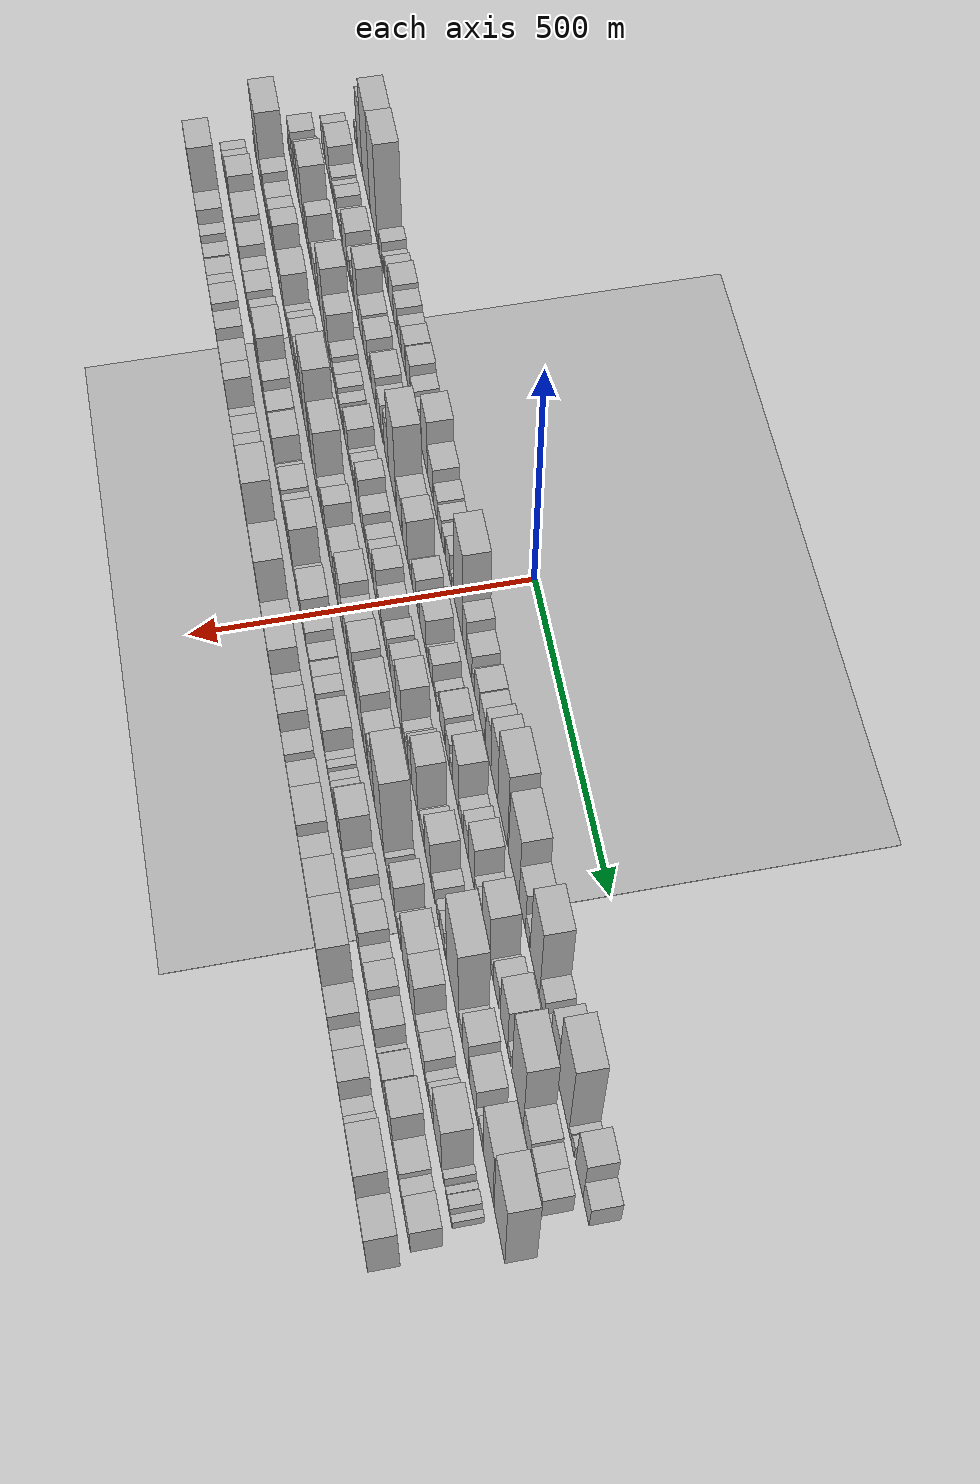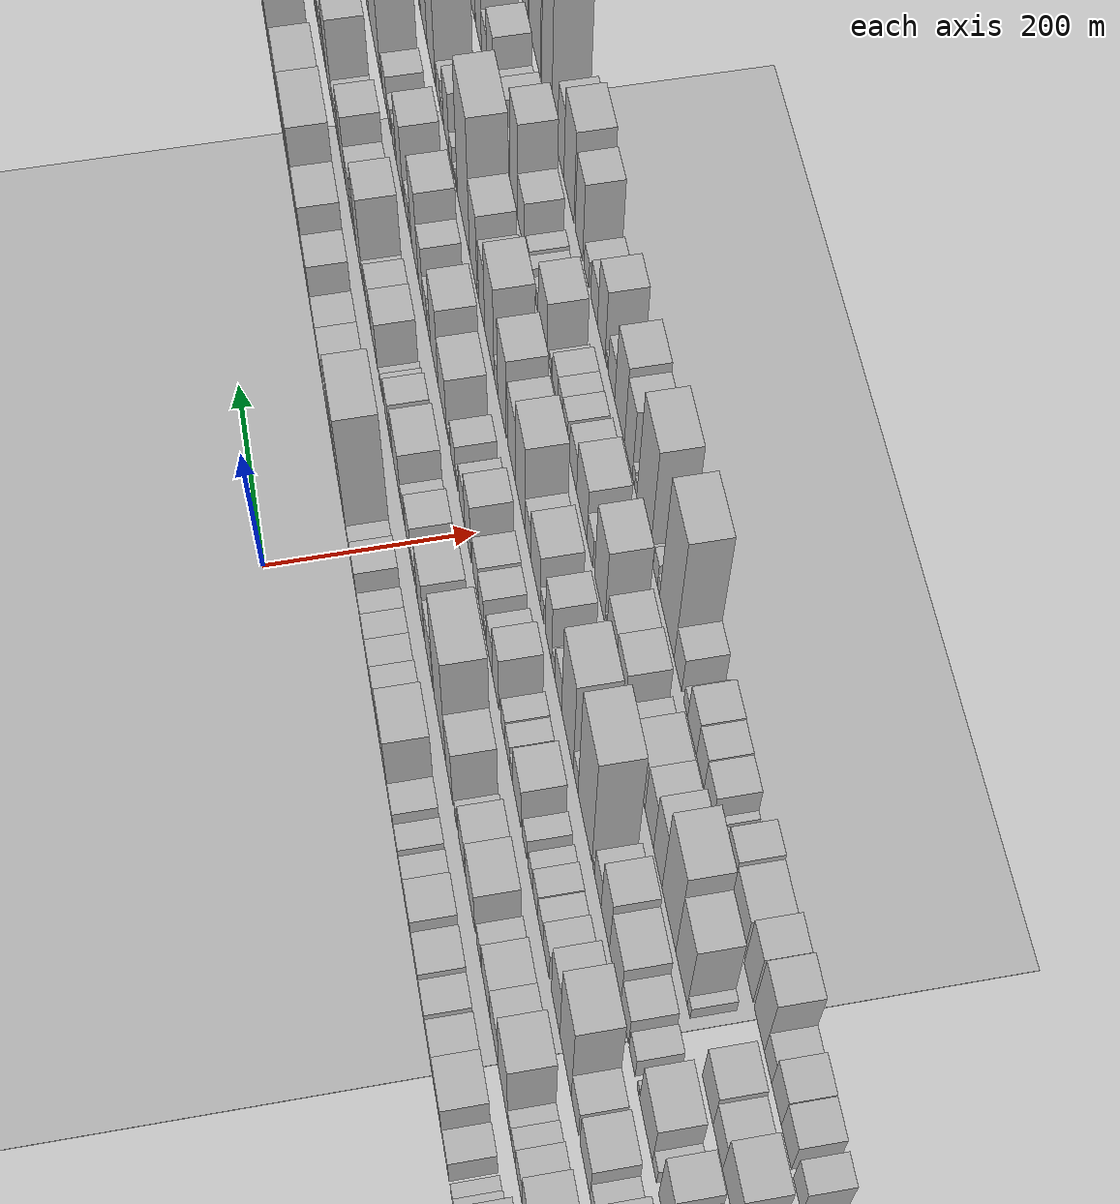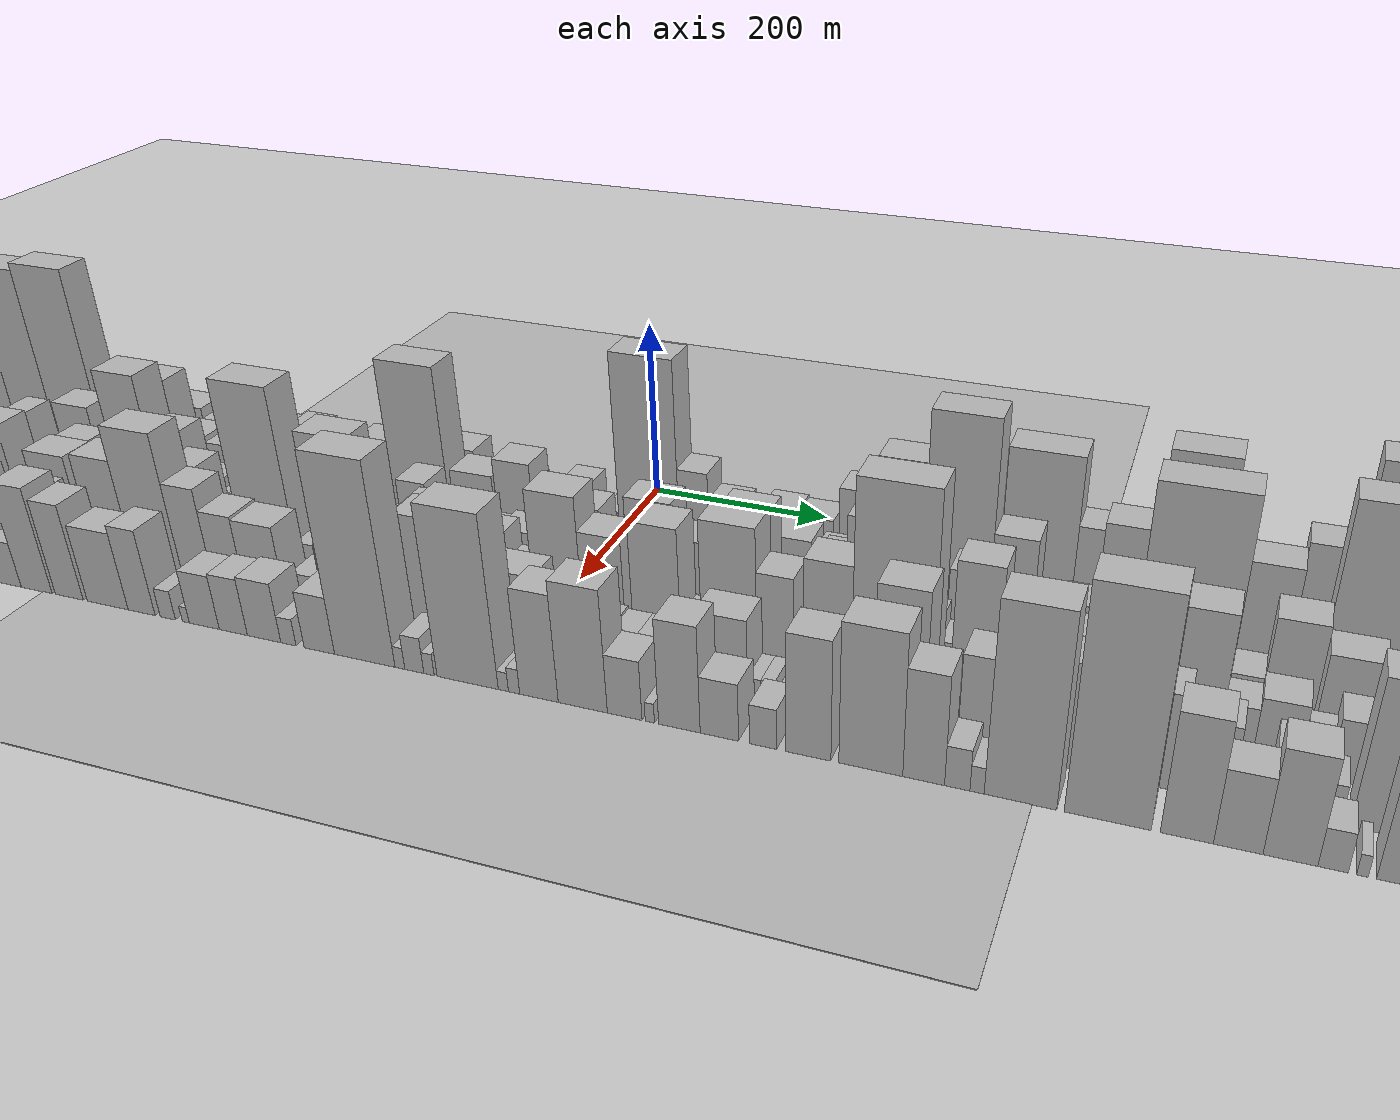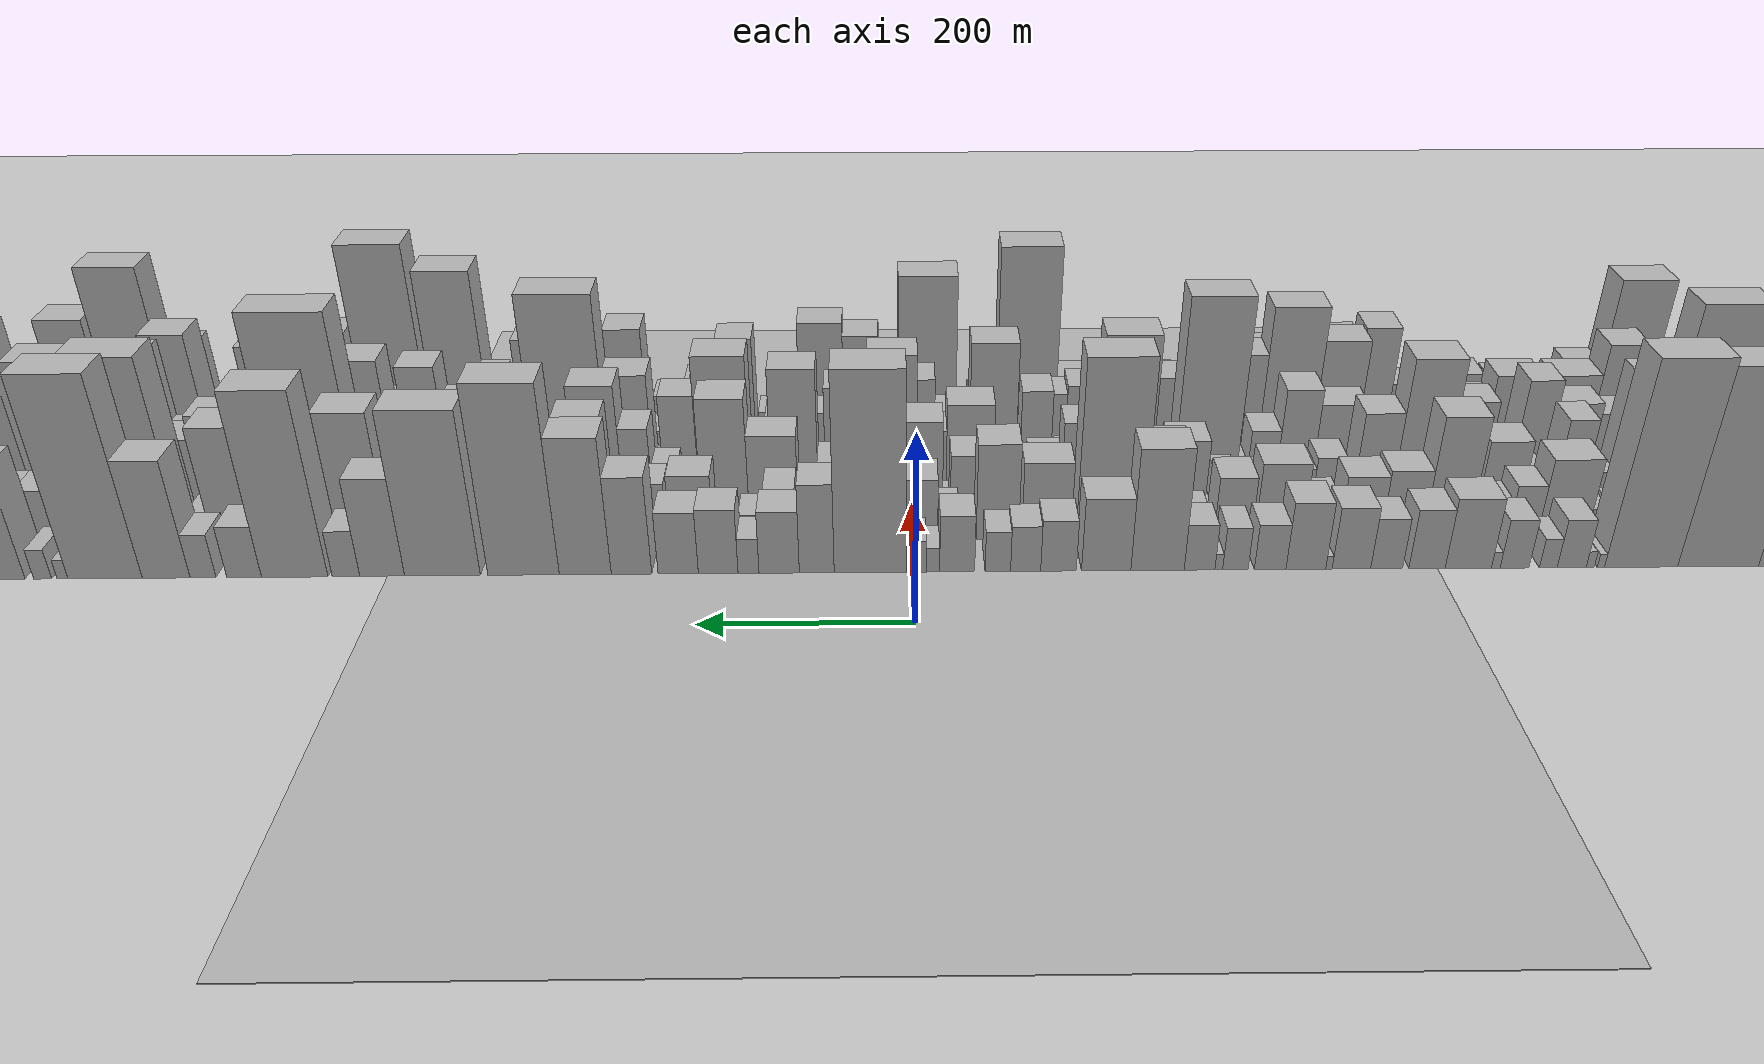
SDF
<?xml version="1.0" encoding="utf-8"?>

<sdf version="1.6">

   <world name="default">

      <gui fullscreen="0">

         <camera name="user_camera">

            <pose>-15 0 4.57585 0 0 0</pose>

            <view_controller>orbit</view_controller>

         </camera>

      </gui>

      <scene>

         <sky>

           <clouds>

             <speed>12</speed>

           </clouds>

         </sky>

         <ambient>0.4 0.4 0.4 1</ambient>

         <background>0.7 0.7 0.7 1</background>

         <shadows>1</shadows>

      </scene>

      <gravity>0 0 -9.8066</gravity>

      <magnetic_field>6e-06 2.3e-05 -4.2e-05</magnetic_field>

      <physics default="0" name="default_physics" type="ode">

         <ode>

            <solver>

               <type>quick</type>

               <iters>10</iters>

               <sor>1.0</sor>

               <use_dynamic_moi_rescaling>0</use_dynamic_moi_rescaling>

            </solver>

            <constraints>

               <cfm>0</cfm>

               <erp>0.2</erp>

               <contact_max_correcting_vel>100</contact_max_correcting_vel>

               <contact_surface_layer>0.001</contact_surface_layer>

            </constraints>

         </ode>

         <max_step_size>0.004</max_step_size>

         <real_time_factor>1</real_time_factor>

         <real_time_update_rate>250</real_time_update_rate>

      </physics>

      <light name="sun" type="directional">

         <cast_shadows>1</cast_shadows>

         <pose>0 0 10 0 0 0</pose>

         <diffuse>0.8 0.8 0.8 1</diffuse>

         <specular>0.2 0.2 0.2 1</specular>

         <attenuation>

            <range>1000</range>

            <constant>0.9</constant>

            <linear>0.01</linear>

            <quadratic>0.001</quadratic>

         </attenuation>

         <direction>-0.5 0.1 -0.9</direction>

      </light>

      <include>

         <name>ground_plane_1</name>

         <uri>model://HANNAS_ground_plane</uri>

         <pose>0 0 0  0 0 0</pose>

      </include>

      <include>

         <name>ground_plane_2</name>

         <uri>model://HANNAS_ground_plane</uri>

         <pose>100 0 0  0 0 0</pose>

      </include>

      <model name="building_1">

         <static>1</static>

         <pose frame="">100.0000 -877.6321 0 0.000000 0.000000 0.000000</pose>

         <link name="link">

            <pose frame="">0 0 21.00 0 0 0</pose>

            <collision name="collision">

               <geometry>

                  <box>

                     <size>40.0000 24.7358 42.0000</size>

                  </box>

               </geometry>

               <max_contacts>10</max_contacts>

               <surface>

                  <contact>

                     <ode/>

                  </contact>

                  <bounce/>

                  <friction>

                     <torsional>

                        <ode/>

                     </torsional>

                     <ode/>

                  </friction>

               </surface>

            </collision>

            <visual name="visual">

               <cast_shadows>0</cast_shadows>

               <geometry>

                  <box>

                     <size>40.0000 24.7358 42.0000</size>

                  </box>

               </geometry>

               <material>

                  <script>

                     <uri>model://HANNAS_wall/materials/scripts</uri>

                     <uri>model://HANNAS_wall/materials/textures</uri>

                     <name>vrc/HANNAS_wall</name>

                  </script>

               </material>

            </visual>

            <self_collide>0</self_collide>

            <enable_wind>0</enable_wind>

            <kinematic>0</kinematic>

         </link>

      </model>

      <model name="building_2">

         <static>1</static>

         <pose frame="">100.0000 -832.5152 0 0.000000 0.000000 0.000000</pose>

         <link name="link">

            <pose frame="">0 0 75.00 0 0 0</pose>

            <collision name="collision">

               <geometry>

                  <box>

                     <size>40.0000 47.4980 150.0000</size>

                  </box>

               </geometry>

               <max_contacts>10</max_contacts>

               <surface>

                  <contact>

                     <ode/>

                  </contact>

                  <bounce/>

                  <friction>

                     <torsional>

                        <ode/>

                     </torsional>

                     <ode/>

                  </friction>

               </surface>

            </collision>

            <visual name="visual">

               <cast_shadows>0</cast_shadows>

               <geometry>

                  <box>

                     <size>40.0000 47.4980 150.0000</size>

                  </box>

               </geometry>

               <material>

                  <script>

                     <uri>model://HANNAS_wall/materials/scripts</uri>

                     <uri>model://HANNAS_wall/materials/textures</uri>

                     <name>vrc/HANNAS_wall</name>

                  </script>

               </material>

            </visual>

            <self_collide>0</self_collide>

            <enable_wind>0</enable_wind>

            <kinematic>0</kinematic>

         </link>

      </model>

      <model name="building_3">

         <static>1</static>

         <pose frame="">100.0000 -769.8653 0 0.000000 0.000000 0.000000</pose>

         <link name="link">

            <pose frame="">0 0 108.00 0 0 0</pose>

            <collision name="collision">

               <geometry>

                  <box>

                     <size>40.0000 77.8020 216.0000</size>

                  </box>

               </geometry>

               <max_contacts>10</max_contacts>

               <surface>

                  <contact>

                     <ode/>

                  </contact>

                  <bounce/>

                  <friction>

                     <torsional>

                        <ode/>

                     </torsional>

                     <ode/>

                  </friction>

               </surface>

            </collision>

            <visual name="visual">

               <cast_shadows>0</cast_shadows>

               <geometry>

                  <box>

                     <size>40.0000 77.8020 216.0000</size>

                  </box>

               </geometry>

               <material>

                  <script>

                     <uri>model://HANNAS_wall/materials/scripts</uri>

                     <uri>model://HANNAS_wall/materials/textures</uri>

                     <name>vrc/HANNAS_wall</name>

                  </script>

               </material>

            </visual>

            <self_collide>0</self_collide>

            <enable_wind>0</enable_wind>

            <kinematic>0</kinematic>

         </link>

      </model>

      <model name="building_4">

         <static>1</static>

         <pose frame="">100.0000 -695.8126 0 0.000000 0.000000 0.000000</pose>

         <link name="link">

            <pose frame="">0 0 112.50 0 0 0</pose>

            <collision name="collision">

               <geometry>

                  <box>

                     <size>40.0000 70.3033 225.0000</size>

                  </box>

               </geometry>

               <max_contacts>10</max_contacts>

               <surface>

                  <contact>

                     <ode/>

                  </contact>

                  <bounce/>

                  <friction>

                     <torsional>

                        <ode/>

                     </torsional>

                     <ode/>

                  </friction>

               </surface>

            </collision>

            <visual name="visual">

               <cast_shadows>0</cast_shadows>

               <geometry>

                  <box>

                     <size>40.0000 70.3033 225.0000</size>

                  </box>

               </geometry>

               <material>

                  <script>

                     <uri>model://HANNAS_wall/materials/scripts</uri>

                     <uri>model://HANNAS_wall/materials/textures</uri>

                     <name>vrc/HANNAS_wall</name>

                  </script>

               </material>

            </visual>

            <self_collide>0</self_collide>

            <enable_wind>0</enable_wind>

            <kinematic>0</kinematic>

         </link>

      </model>

      <model name="building_5">

         <static>1</static>

         <pose frame="">100.0000 -657.1989 0 0.000000 0.000000 0.000000</pose>

         <link name="link">

            <pose frame="">0 0 7.50 0 0 0</pose>

            <collision name="collision">

               <geometry>

                  <box>

                     <size>40.0000 6.9241 15.0000</size>

                  </box>

               </geometry>

               <max_contacts>10</max_contacts>

               <surface>

                  <contact>

                     <ode/>

                  </contact>

                  <bounce/>

                  <friction>

                     <torsional>

                        <ode/>

                     </torsional>

                     <ode/>

                  </friction>

               </surface>

            </collision>

            <visual name="visual">

               <cast_shadows>0</cast_shadows>

               <geometry>

                  <box>

                     <size>40.0000 6.9241 15.0000</size>

                  </box>

               </geometry>

               <material>

                  <script>

                     <uri>model://HANNAS_wall/materials/scripts</uri>

                     <uri>model://HANNAS_wall/materials/textures</uri>

                     <name>vrc/HANNAS_wall</name>

                  </script>

               </material>

            </visual>

            <self_collide>0</self_collide>

            <enable_wind>0</enable_wind>

            <kinematic>0</kinematic>

         </link>

      </model>

      <model name="building_6">

         <static>1</static>

         <pose frame="">100.0000 -646.8357 0 0.000000 0.000000 0.000000</pose>

         <link name="link">

            <pose frame="">0 0 9.00 0 0 0</pose>

            <collision name="collision">

               <geometry>

                  <box>

                     <size>40.0000 7.8023 18.0000</size>

                  </box>

               </geometry>

               <max_contacts>10</max_contacts>

               <surface>

                  <contact>

                     <ode/>

                  </contact>

                  <bounce/>

                  <friction>

                     <torsional>

                        <ode/>

                     </torsional>

                     <ode/>

                  </friction>

               </surface>

            </collision>

            <visual name="visual">

               <cast_shadows>0</cast_shadows>

               <geometry>

                  <box>

                     <size>40.0000 7.8023 18.0000</size>

                  </box>

               </geometry>

               <material>

                  <script>

                     <uri>model://HANNAS_wall/materials/scripts</uri>

                     <uri>model://HANNAS_wall/materials/textures</uri>

                     <name>vrc/HANNAS_wall</name>

                  </script>

               </material>

            </visual>

            <self_collide>0</self_collide>

            <enable_wind>0</enable_wind>

            <kinematic>0</kinematic>

         </link>

      </model>

      <model name="building_7">

         <static>1</static>

         <pose frame="">100.0000 -628.9897 0 0.000000 0.000000 0.000000</pose>

         <link name="link">

            <pose frame="">0 0 27.00 0 0 0</pose>

            <collision name="collision">

               <geometry>

                  <box>

                     <size>40.0000 27.8899 54.0000</size>

                  </box>

               </geometry>

               <max_contacts>10</max_contacts>

               <surface>

                  <contact>

                     <ode/>

                  </contact>

                  <bounce/>

                  <friction>

                     <torsional>

                        <ode/>

                     </torsional>

                     <ode/>

                  </friction>

               </surface>

            </collision>

            <visual name="visual">

               <cast_shadows>0</cast_shadows>

               <geometry>

                  <box>

                     <size>40.0000 27.8899 54.0000</size>

                  </box>

               </geometry>

               <material>

                  <script>

                     <uri>model://HANNAS_wall/materials/scripts</uri>

                     <uri>model://HANNAS_wall/materials/textures</uri>

                     <name>vrc/HANNAS_wall</name>

                  </script>

               </material>

            </visual>

            <self_collide>0</self_collide>

            <enable_wind>0</enable_wind>

            <kinematic>0</kinematic>

         </link>

      </model>

      <model name="building_8">

         <static>1</static>

         <pose frame="">100.0000 -606.5213 0 0.000000 0.000000 0.000000</pose>

         <link name="link">

            <pose frame="">0 0 16.50 0 0 0</pose>

            <collision name="collision">

               <geometry>

                  <box>

                     <size>40.0000 17.0468 33.0000</size>

                  </box>

               </geometry>

               <max_contacts>10</max_contacts>

               <surface>

                  <contact>

                     <ode/>

                  </contact>

                  <bounce/>

                  <friction>

                     <torsional>

                        <ode/>

                     </torsional>

                     <ode/>

                  </friction>

               </surface>

            </collision>

            <visual name="visual">

               <cast_shadows>0</cast_shadows>

               <geometry>

                  <box>

                     <size>40.0000 17.0468 33.0000</size>

                  </box>

               </geometry>

               <material>

                  <script>

                     <uri>model://HANNAS_wall/materials/scripts</uri>

                     <uri>model://HANNAS_wall/materials/textures</uri>

                     <name>vrc/HANNAS_wall</name>

                  </script>

               </material>

            </visual>

            <self_collide>0</self_collide>

            <enable_wind>0</enable_wind>

            <kinematic>0</kinematic>

         </link>

      </model>

      <model name="building_9">

         <static>1</static>

         <pose frame="">100.0000 -574.1460 0 0.000000 0.000000 0.000000</pose>

         <link name="link">

            <pose frame="">0 0 27.00 0 0 0</pose>

            <collision name="collision">

               <geometry>

                  <box>

                     <size>40.0000 27.7039 54.0000</size>

                  </box>

               </geometry>

               <max_contacts>10</max_contacts>

               <surface>

                  <contact>

                     <ode/>

                  </contact>

                  <bounce/>

                  <friction>

                     <torsional>

                        <ode/>

                     </torsional>

                     <ode/>

                  </friction>

               </surface>

            </collision>

            <visual name="visual">

               <cast_shadows>0</cast_shadows>

               <geometry>

                  <box>

                     <size>40.0000 27.7039 54.0000</size>

                  </box>

               </geometry>

               <material>

                  <script>

                     <uri>model://HANNAS_wall/materials/scripts</uri>

                     <uri>model://HANNAS_wall/materials/textures</uri>

                     <name>vrc/HANNAS_wall</name>

                  </script>

               </material>

            </visual>

            <self_collide>0</self_collide>

            <enable_wind>0</enable_wind>

            <kinematic>0</kinematic>

         </link>

      </model>

      <model name="building_10">

         <static>1</static>

         <pose frame="">100.0000 -556.1381 0 0.000000 0.000000 0.000000</pose>

         <link name="link">

            <pose frame="">0 0 9.00 0 0 0</pose>

            <collision name="collision">

               <geometry>

                  <box>

                     <size>40.0000 8.3117 18.0000</size>

                  </box>

               </geometry>

               <max_contacts>10</max_contacts>

               <surface>

                  <contact>

                     <ode/>

                  </contact>

                  <bounce/>

                  <friction>

                     <torsional>

                        <ode/>

                     </torsional>

                     <ode/>

                  </friction>

               </surface>

            </collision>

            <visual name="visual">

               <cast_shadows>0</cast_shadows>

               <geometry>

                  <box>

                     <size>40.0000 8.3117 18.0000</size>

                  </box>

               </geometry>

               <material>

                  <script>

                     <uri>model://HANNAS_wall/materials/scripts</uri>

                     <uri>model://HANNAS_wall/materials/textures</uri>

                     <name>vrc/HANNAS_wall</name>

                  </script>

               </material>

            </visual>

            <self_collide>0</self_collide>

            <enable_wind>0</enable_wind>

            <kinematic>0</kinematic>

         </link>

      </model>

      <model name="building_11">

         <static>1</static>

         <pose frame="">100.0000 -529.7301 0 0.000000 0.000000 0.000000</pose>

         <link name="link">

            <pose frame="">0 0 39.00 0 0 0</pose>

            <collision name="collision">

               <geometry>

                  <box>

                     <size>40.0000 44.5044 78.0000</size>

                  </box>

               </geometry>

               <max_contacts>10</max_contacts>

               <surface>

                  <contact>

                     <ode/>

                  </contact>

                  <bounce/>

                  <friction>

                     <torsional>

                        <ode/>

                     </torsional>

                     <ode/>

                  </friction>

               </surface>

            </collision>

            <visual name="visual">

               <cast_shadows>0</cast_shadows>

               <geometry>

                  <box>

                     <size>40.0000 44.5044 78.0000</size>

                  </box>

               </geometry>

               <material>

                  <script>

                     <uri>model://HANNAS_wall/materials/scripts</uri>

                     <uri>model://HANNAS_wall/materials/textures</uri>

                     <name>vrc/HANNAS_wall</name>

                  </script>

               </material>

            </visual>

            <self_collide>0</self_collide>

            <enable_wind>0</enable_wind>

            <kinematic>0</kinematic>

         </link>

      </model>

      <model name="building_12">

         <static>1</static>

         <pose frame="">100.0000 -490.0236 0 0.000000 0.000000 0.000000</pose>

         <link name="link">

            <pose frame="">0 0 33.00 0 0 0</pose>

            <collision name="collision">

               <geometry>

                  <box>

                     <size>40.0000 34.9087 66.0000</size>

                  </box>

               </geometry>

               <max_contacts>10</max_contacts>

               <surface>

                  <contact>

                     <ode/>

                  </contact>

                  <bounce/>

                  <friction>

                     <torsional>

                        <ode/>

                     </torsional>

                     <ode/>

                  </friction>

               </surface>

            </collision>

            <visual name="visual">

               <cast_shadows>0</cast_shadows>

               <geometry>

                  <box>

                     <size>40.0000 34.9087 66.0000</size>

                  </box>

               </geometry>

               <material>

                  <script>

                     <uri>model://HANNAS_wall/materials/scripts</uri>

                     <uri>model://HANNAS_wall/materials/textures</uri>

                     <name>vrc/HANNAS_wall</name>

                  </script>

               </material>

            </visual>

            <self_collide>0</self_collide>

            <enable_wind>0</enable_wind>

            <kinematic>0</kinematic>

         </link>

      </model>

      <model name="building_13">

         <static>1</static>

         <pose frame="">100.0000 -451.2603 0 0.000000 0.000000 0.000000</pose>

         <link name="link">

            <pose frame="">0 0 28.50 0 0 0</pose>

            <collision name="collision">

               <geometry>

                  <box>

                     <size>40.0000 30.6178 57.0000</size>

                  </box>

               </geometry>

               <max_contacts>10</max_contacts>

               <surface>

                  <contact>

                     <ode/>

                  </contact>

                  <bounce/>

                  <friction>

                     <torsional>

                        <ode/>

                     </torsional>

                     <ode/>

                  </friction>

               </surface>

            </collision>

            <visual name="visual">

               <cast_shadows>0</cast_shadows>

               <geometry>

                  <box>

                     <size>40.0000 30.6178 57.0000</size>

                  </box>

               </geometry>

               <material>

                  <script>

                     <uri>model://HANNAS_wall/materials/scripts</uri>

                     <uri>model://HANNAS_wall/materials/textures</uri>

                     <name>vrc/HANNAS_wall</name>

                  </script>

               </material>

            </visual>

            <self_collide>0</self_collide>

            <enable_wind>0</enable_wind>

            <kinematic>0</kinematic>

         </link>

      </model>

      <model name="building_14">

         <static>1</static>

         <pose frame="">100.0000 -417.4339 0 0.000000 0.000000 0.000000</pose>

         <link name="link">

            <pose frame="">0 0 34.50 0 0 0</pose>

            <collision name="collision">

               <geometry>

                  <box>

                     <size>40.0000 37.0351 69.0000</size>

                  </box>

               </geometry>

               <max_contacts>10</max_contacts>

               <surface>

                  <contact>

                     <ode/>

                  </contact>

                  <bounce/>

                  <friction>

                     <torsional>

                        <ode/>

                     </torsional>

                     <ode/>

                  </friction>

               </surface>

            </collision>

            <visual name="visual">

               <cast_shadows>0</cast_shadows>

               <geometry>

                  <box>

                     <size>40.0000 37.0351 69.0000</size>

                  </box>

               </geometry>

               <material>

                  <script>

                     <uri>model://HANNAS_wall/materials/scripts</uri>

                     <uri>model://HANNAS_wall/materials/textures</uri>

                     <name>vrc/HANNAS_wall</name>

                  </script>

               </material>

            </visual>

            <self_collide>0</self_collide>

            <enable_wind>0</enable_wind>

            <kinematic>0</kinematic>

         </link>

      </model>

      <model name="building_15">

         <static>1</static>

         <pose frame="">100.0000 -395.8681 0 0.000000 0.000000 0.000000</pose>

         <link name="link">

            <pose frame="">0 0 7.50 0 0 0</pose>

            <collision name="collision">

               <geometry>

                  <box>

                     <size>40.0000 6.0965 15.0000</size>

                  </box>

               </geometry>

               <max_contacts>10</max_contacts>

               <surface>

                  <contact>

                     <ode/>

                  </contact>

                  <bounce/>

                  <friction>

                     <torsional>

                        <ode/>

                     </torsional>

                     <ode/>

                  </friction>

               </surface>

            </collision>

            <visual name="visual">

               <cast_shadows>0</cast_shadows>

               <geometry>

                  <box>

                     <size>40.0000 6.0965 15.0000</size>

                  </box>

               </geometry>

               <material>

                  <script>

                     <uri>model://HANNAS_wall/materials/scripts</uri>

                     <uri>model://HANNAS_wall/materials/textures</uri>

                     <name>vrc/HANNAS_wall</name>

                  </script>

               </material>

            </visual>

            <self_collide>0</self_collide>

            <enable_wind>0</enable_wind>

            <kinematic>0</kinematic>

         </link>

      </model>

      <model name="building_16">

         <static>1</static>

         <pose frame="">100.0000 -373.7618 0 0.000000 0.000000 0.000000</pose>

         <link name="link">

            <pose frame="">0 0 37.50 0 0 0</pose>

            <collision name="collision">

               <geometry>

                  <box>

                     <size>40.0000 38.1160 75.0000</size>

                  </box>

               </geometry>

               <max_contacts>10</max_contacts>

               <surface>

                  <contact>

                     <ode/>

                  </contact>

                  <bounce/>

                  <friction>

                     <torsional>

                        <ode/>

                     </torsional>

                     <ode/>

                  </friction>

               </surface>

            </collision>

            <visual name="visual">

               <cast_shadows>0</cast_shadows>

               <geometry>

                  <box>

                     <size>40.0000 38.1160 75.0000</size>

                  </box>

               </geometry>

               <material>

                  <script>

                     <uri>model://HANNAS_wall/materials/scripts</uri>

                     <uri>model://HANNAS_wall/materials/textures</uri>

                     <name>vrc/HANNAS_wall</name>

                  </script>

               </material>

            </visual>

            <self_collide>0</self_collide>

            <enable_wind>0</enable_wind>

            <kinematic>0</kinematic>

         </link>

      </model>

      <model name="building_17">

         <static>1</static>

         <pose frame="">100.0000 -339.5787 0 0.000000 0.000000 0.000000</pose>

         <link name="link">

            <pose frame="">0 0 25.50 0 0 0</pose>

            <collision name="collision">

               <geometry>

                  <box>

                     <size>40.0000 30.2502 51.0000</size>

                  </box>

               </geometry>

               <max_contacts>10</max_contacts>

               <surface>

                  <contact>

                     <ode/>

                  </contact>

                  <bounce/>

                  <friction>

                     <torsional>

                        <ode/>

                     </torsional>

                     <ode/>

                  </friction>

               </surface>

            </collision>

            <visual name="visual">

               <cast_shadows>0</cast_shadows>

               <geometry>

                  <box>

                     <size>40.0000 30.2502 51.0000</size>

                  </box>

               </geometry>

               <material>

                  <script>

                     <uri>model://HANNAS_wall/materials/scripts</uri>

                     <uri>model://HANNAS_wall/materials/textures</uri>

                     <name>vrc/HANNAS_wall</name>

                  </script>

               </material>

            </visual>

            <self_collide>0</self_collide>

            <enable_wind>0</enable_wind>

            <kinematic>0</kinematic>

         </link>

      </model>

      <model name="building_18">

         <static>1</static>

         <pose frame="">100.0000 -306.2498 0 0.000000 0.000000 0.000000</pose>

         <link name="link">

            <pose frame="">0 0 24.00 0 0 0</pose>

            <collision name="collision">

               <geometry>

                  <box>

                     <size>40.0000 24.4077 48.0000</size>

                  </box>

               </geometry>

               <max_contacts>10</max_contacts>

               <surface>

                  <contact>

                     <ode/>

                  </contact>

                  <bounce/>

                  <friction>

                     <torsional>

                        <ode/>

                     </torsional>

                     <ode/>

                  </friction>

               </surface>

            </collision>

            <visual name="visual">

               <cast_shadows>0</cast_shadows>

               <geometry>

                  <box>

                     <size>40.0000 24.4077 48.0000</size>

                  </box>

               </geometry>

               <material>

                  <script>

                     <uri>model://HANNAS_wall/materials/scripts</uri>

                     <uri>model://HANNAS_wall/materials/textures</uri>

                     <name>vrc/HANNAS_wall</name>

                  </script>

               </material>

            </visual>

            <self_collide>0</self_collide>

            <enable_wind>0</enable_wind>

            <kinematic>0</kinematic>

         </link>

      </model>

      <model name="building_19">

         <static>1</static>

         <pose frame="">100.0000 -290.3499 0 0.000000 0.000000 0.000000</pose>

         <link name="link">

            <pose frame="">0 0 9.00 0 0 0</pose>

            <collision name="collision">

               <geometry>

                  <box>

                     <size>40.0000 7.3921 18.0000</size>

                  </box>

               </geometry>

               <max_contacts>10</max_contacts>

               <surface>

                  <contact>

                     <ode/>

                  </contact>

                  <bounce/>

                  <friction>

                     <torsional>

                        <ode/>

                     </torsional>

                     <ode/>

                  </friction>

               </surface>

            </collision>

            <visual name="visual">

               <cast_shadows>0</cast_shadows>

               <geometry>

                  <box>

                     <size>40.0000 7.3921 18.0000</size>

                  </box>

               </geometry>

               <material>

                  <script>

                     <uri>model://HANNAS_wall/materials/scripts</uri>

                     <uri>model://HANNAS_wall/materials/textures</uri>

                     <name>vrc/HANNAS_wall</name>

                  </script>

               </material>

            </visual>

            <self_collide>0</self_collide>

            <enable_wind>0</enable_wind>

            <kinematic>0</kinematic>

         </link>

      </model>

      <model name="building_20">

         <static>1</static>

         <pose frame="">100.0000 -272.0028 0 0.000000 0.000000 0.000000</pose>

         <link name="link">

            <pose frame="">0 0 25.50 0 0 0</pose>

            <collision name="collision">

               <geometry>

                  <box>

                     <size>40.0000 29.3020 51.0000</size>

                  </box>

               </geometry>

               <max_contacts>10</max_contacts>

               <surface>

                  <contact>

                     <ode/>

                  </contact>

                  <bounce/>

                  <friction>

                     <torsional>

                        <ode/>

                     </torsional>

                     <ode/>

                  </friction>

               </surface>

            </collision>

            <visual name="visual">

               <cast_shadows>0</cast_shadows>

               <geometry>

                  <box>

                     <size>40.0000 29.3020 51.0000</size>

                  </box>

               </geometry>

               <material>

                  <script>

                     <uri>model://HANNAS_wall/materials/scripts</uri>

                     <uri>model://HANNAS_wall/materials/textures</uri>

                     <name>vrc/HANNAS_wall</name>

                  </script>

               </material>

            </visual>

            <self_collide>0</self_collide>

            <enable_wind>0</enable_wind>

            <kinematic>0</kinematic>

         </link>

      </model>

      <model name="building_21">

         <static>1</static>

         <pose frame="">100.0000 -231.8387 0 0.000000 0.000000 0.000000</pose>

         <link name="link">

            <pose frame="">0 0 67.50 0 0 0</pose>

            <collision name="collision">

               <geometry>

                  <box>

                     <size>40.0000 51.0263 135.0000</size>

                  </box>

               </geometry>

               <max_contacts>10</max_contacts>

               <surface>

                  <contact>

                     <ode/>

                  </contact>

                  <bounce/>

                  <friction>

                     <torsional>

                        <ode/>

                     </torsional>

                     <ode/>

                  </friction>

               </surface>

            </collision>

            <visual name="visual">

               <cast_shadows>0</cast_shadows>

               <geometry>

                  <box>

                     <size>40.0000 51.0263 135.0000</size>

                  </box>

               </geometry>

               <material>

                  <script>

                     <uri>model://HANNAS_wall/materials/scripts</uri>

                     <uri>model://HANNAS_wall/materials/textures</uri>

                     <name>vrc/HANNAS_wall</name>

                  </script>

               </material>

            </visual>

            <self_collide>0</self_collide>

            <enable_wind>0</enable_wind>

            <kinematic>0</kinematic>

         </link>

      </model>

      <model name="building_22">

         <static>1</static>

         <pose frame="">100.0000 -182.7583 0 0.000000 0.000000 0.000000</pose>

         <link name="link">

            <pose frame="">0 0 40.50 0 0 0</pose>

            <collision name="collision">

               <geometry>

                  <box>

                     <size>40.0000 47.1345 81.0000</size>

                  </box>

               </geometry>

               <max_contacts>10</max_contacts>

               <surface>

                  <contact>

                     <ode/>

                  </contact>

                  <bounce/>

                  <friction>

                     <torsional>

                        <ode/>

                     </torsional>

                     <ode/>

                  </friction>

               </surface>

            </collision>

            <visual name="visual">

               <cast_shadows>0</cast_shadows>

               <geometry>

                  <box>

                     <size>40.0000 47.1345 81.0000</size>

                  </box>

               </geometry>

               <material>

                  <script>

                     <uri>model://HANNAS_wall/materials/scripts</uri>

                     <uri>model://HANNAS_wall/materials/textures</uri>

                     <name>vrc/HANNAS_wall</name>

                  </script>

               </material>

            </visual>

            <self_collide>0</self_collide>

            <enable_wind>0</enable_wind>

            <kinematic>0</kinematic>

         </link>

      </model>

      <model name="building_23">

         <static>1</static>

         <pose frame="">100.0000 -137.2000 0 0.000000 0.000000 0.000000</pose>

         <link name="link">

            <pose frame="">0 0 28.50 0 0 0</pose>

            <collision name="collision">

               <geometry>

                  <box>

                     <size>40.0000 33.9821 57.0000</size>

                  </box>

               </geometry>

               <max_contacts>10</max_contacts>

               <surface>

                  <contact>

                     <ode/>

                  </contact>

                  <bounce/>

                  <friction>

                     <torsional>

                        <ode/>

                     </torsional>

                     <ode/>

                  </friction>

               </surface>

            </collision>

            <visual name="visual">

               <cast_shadows>0</cast_shadows>

               <geometry>

                  <box>

                     <size>40.0000 33.9821 57.0000</size>

                  </box>

               </geometry>

               <material>

                  <script>

                     <uri>model://HANNAS_wall/materials/scripts</uri>

                     <uri>model://HANNAS_wall/materials/textures</uri>

                     <name>vrc/HANNAS_wall</name>

                  </script>

               </material>

            </visual>

            <self_collide>0</self_collide>

            <enable_wind>0</enable_wind>

            <kinematic>0</kinematic>

         </link>

      </model>

      <model name="building_24">

         <static>1</static>

         <pose frame="">100.0000 -105.8608 0 0.000000 0.000000 0.000000</pose>

         <link name="link">

            <pose frame="">0 0 25.50 0 0 0</pose>

            <collision name="collision">

               <geometry>

                  <box>

                     <size>40.0000 28.6963 51.0000</size>

                  </box>

               </geometry>

               <max_contacts>10</max_contacts>

               <surface>

                  <contact>

                     <ode/>

                  </contact>

                  <bounce/>

                  <friction>

                     <torsional>

                        <ode/>

                     </torsional>

                     <ode/>

                  </friction>

               </surface>

            </collision>

            <visual name="visual">

               <cast_shadows>0</cast_shadows>

               <geometry>

                  <box>

                     <size>40.0000 28.6963 51.0000</size>

                  </box>

               </geometry>

               <material>

                  <script>

                     <uri>model://HANNAS_wall/materials/scripts</uri>

                     <uri>model://HANNAS_wall/materials/textures</uri>

                     <name>vrc/HANNAS_wall</name>

                  </script>

               </material>

            </visual>

            <self_collide>0</self_collide>

            <enable_wind>0</enable_wind>

            <kinematic>0</kinematic>

         </link>

      </model>

      <model name="building_25">

         <static>1</static>

         <pose frame="">100.0000 -79.3801 0 0.000000 0.000000 0.000000</pose>

         <link name="link">

            <pose frame="">0 0 22.50 0 0 0</pose>

            <collision name="collision">

               <geometry>

                  <box>

                     <size>40.0000 24.2652 45.0000</size>

                  </box>

               </geometry>

               <max_contacts>10</max_contacts>

               <surface>

                  <contact>

                     <ode/>

                  </contact>

                  <bounce/>

                  <friction>

                     <torsional>

                        <ode/>

                     </torsional>

                     <ode/>

                  </friction>

               </surface>

            </collision>

            <visual name="visual">

               <cast_shadows>0</cast_shadows>

               <geometry>

                  <box>

                     <size>40.0000 24.2652 45.0000</size>

                  </box>

               </geometry>

               <material>

                  <script>

                     <uri>model://HANNAS_wall/materials/scripts</uri>

                     <uri>model://HANNAS_wall/materials/textures</uri>

                     <name>vrc/HANNAS_wall</name>

                  </script>

               </material>

            </visual>

            <self_collide>0</self_collide>

            <enable_wind>0</enable_wind>

            <kinematic>0</kinematic>

         </link>

      </model>

      <model name="building_26">

         <static>1</static>

         <pose frame="">100.0000 -40.5828 0 0.000000 0.000000 0.000000</pose>

         <link name="link">

            <pose frame="">0 0 31.50 0 0 0</pose>

            <collision name="collision">

               <geometry>

                  <box>

                     <size>40.0000 33.3293 63.0000</size>

                  </box>

               </geometry>

               <max_contacts>10</max_contacts>

               <surface>

                  <contact>

                     <ode/>

                  </contact>

                  <bounce/>

                  <friction>

                     <torsional>

                        <ode/>

                     </torsional>

                     <ode/>

                  </friction>

               </surface>

            </collision>

            <visual name="visual">

               <cast_shadows>0</cast_shadows>

               <geometry>

                  <box>

                     <size>40.0000 33.3293 63.0000</size>

                  </box>

               </geometry>

               <material>

                  <script>

                     <uri>model://HANNAS_wall/materials/scripts</uri>

                     <uri>model://HANNAS_wall/materials/textures</uri>

                     <name>vrc/HANNAS_wall</name>

                  </script>

               </material>

            </visual>

            <self_collide>0</self_collide>

            <enable_wind>0</enable_wind>

            <kinematic>0</kinematic>

         </link>

      </model>

      <model name="building_27">

         <static>1</static>

         <pose frame="">100.0000 -17.4925 0 0.000000 0.000000 0.000000</pose>

         <link name="link">

            <pose frame="">0 0 13.50 0 0 0</pose>

            <collision name="collision">

               <geometry>

                  <box>

                     <size>40.0000 12.8513 27.0000</size>

                  </box>

               </geometry>

               <max_contacts>10</max_contacts>

               <surface>

                  <contact>

                     <ode/>

                  </contact>

                  <bounce/>

                  <friction>

                     <torsional>

                        <ode/>

                     </torsional>

                     <ode/>

                  </friction>

               </surface>

            </collision>

            <visual name="visual">

               <cast_shadows>0</cast_shadows>

               <geometry>

                  <box>

                     <size>40.0000 12.8513 27.0000</size>

                  </box>

               </geometry>

               <material>

                  <script>

                     <uri>model://HANNAS_wall/materials/scripts</uri>

                     <uri>model://HANNAS_wall/materials/textures</uri>

                     <name>vrc/HANNAS_wall</name>

                  </script>

               </material>

            </visual>

            <self_collide>0</self_collide>

            <enable_wind>0</enable_wind>

            <kinematic>0</kinematic>

         </link>

      </model>

      <model name="building_28">

         <static>1</static>

         <pose frame="">100.0000 -1.4710 0 0.000000 0.000000 0.000000</pose>

         <link name="link">

            <pose frame="">0 0 18.00 0 0 0</pose>

            <collision name="collision">

               <geometry>

                  <box>

                     <size>40.0000 19.1918 36.0000</size>

                  </box>

               </geometry>

               <max_contacts>10</max_contacts>

               <surface>

                  <contact>

                     <ode/>

                  </contact>

                  <bounce/>

                  <friction>

                     <torsional>

                        <ode/>

                     </torsional>

                     <ode/>

                  </friction>

               </surface>

            </collision>

            <visual name="visual">

               <cast_shadows>0</cast_shadows>

               <geometry>

                  <box>

                     <size>40.0000 19.1918 36.0000</size>

                  </box>

               </geometry>

               <material>

                  <script>

                     <uri>model://HANNAS_wall/materials/scripts</uri>

                     <uri>model://HANNAS_wall/materials/textures</uri>

                     <name>vrc/HANNAS_wall</name>

                  </script>

               </material>

            </visual>

            <self_collide>0</self_collide>

            <enable_wind>0</enable_wind>

            <kinematic>0</kinematic>

         </link>

      </model>

      <model name="building_29">

         <static>1</static>

         <pose frame="">100.0000 42.3173 0 0.000000 0.000000 0.000000</pose>

         <link name="link">

            <pose frame="">0 0 109.50 0 0 0</pose>

            <collision name="collision">

               <geometry>

                  <box>

                     <size>40.0000 68.3846 219.0000</size>

                  </box>

               </geometry>

               <max_contacts>10</max_contacts>

               <surface>

                  <contact>

                     <ode/>

                  </contact>

                  <bounce/>

                  <friction>

                     <torsional>

                        <ode/>

                     </torsional>

                     <ode/>

                  </friction>

               </surface>

            </collision>

            <visual name="visual">

               <cast_shadows>0</cast_shadows>

               <geometry>

                  <box>

                     <size>40.0000 68.3846 219.0000</size>

                  </box>

               </geometry>

               <material>

                  <script>

                     <uri>model://HANNAS_wall/materials/scripts</uri>

                     <uri>model://HANNAS_wall/materials/textures</uri>

                     <name>vrc/HANNAS_wall</name>

                  </script>

               </material>

            </visual>

            <self_collide>0</self_collide>

            <enable_wind>0</enable_wind>

            <kinematic>0</kinematic>

         </link>

      </model>

      <model name="building_30">

         <static>1</static>

         <pose frame="">100.0000 93.0779 0 0.000000 0.000000 0.000000</pose>

         <link name="link">

            <pose frame="">0 0 49.50 0 0 0</pose>

            <collision name="collision">

               <geometry>

                  <box>

                     <size>40.0000 33.1367 99.0000</size>

                  </box>

               </geometry>

               <max_contacts>10</max_contacts>

               <surface>

                  <contact>

                     <ode/>

                  </contact>

                  <bounce/>

                  <friction>

                     <torsional>

                        <ode/>

                     </torsional>

                     <ode/>

                  </friction>

               </surface>

            </collision>

            <visual name="visual">

               <cast_shadows>0</cast_shadows>

               <geometry>

                  <box>

                     <size>40.0000 33.1367 99.0000</size>

                  </box>

               </geometry>

               <material>

                  <script>

                     <uri>model://HANNAS_wall/materials/scripts</uri>

                     <uri>model://HANNAS_wall/materials/textures</uri>

                     <name>vrc/HANNAS_wall</name>

                  </script>

               </material>

            </visual>

            <self_collide>0</self_collide>

            <enable_wind>0</enable_wind>

            <kinematic>0</kinematic>

         </link>

      </model>

      <model name="building_31">

         <static>1</static>

         <pose frame="">100.0000 128.8266 0 0.000000 0.000000 0.000000</pose>

         <link name="link">

            <pose frame="">0 0 34.50 0 0 0</pose>

            <collision name="collision">

               <geometry>

                  <box>

                     <size>40.0000 38.3606 69.0000</size>

                  </box>

               </geometry>

               <max_contacts>10</max_contacts>

               <surface>

                  <contact>

                     <ode/>

                  </contact>

                  <bounce/>

                  <friction>

                     <torsional>

                        <ode/>

                     </torsional>

                     <ode/>

                  </friction>

               </surface>

            </collision>

            <visual name="visual">

               <cast_shadows>0</cast_shadows>

               <geometry>

                  <box>

                     <size>40.0000 38.3606 69.0000</size>

                  </box>

               </geometry>

               <material>

                  <script>

                     <uri>model://HANNAS_wall/materials/scripts</uri>

                     <uri>model://HANNAS_wall/materials/textures</uri>

                     <name>vrc/HANNAS_wall</name>

                  </script>

               </material>

            </visual>

            <self_collide>0</self_collide>

            <enable_wind>0</enable_wind>

            <kinematic>0</kinematic>

         </link>

      </model>

      <model name="building_32">

         <static>1</static>

         <pose frame="">100.0000 157.9525 0 0.000000 0.000000 0.000000</pose>

         <link name="link">

            <pose frame="">0 0 19.50 0 0 0</pose>

            <collision name="collision">

               <geometry>

                  <box>

                     <size>40.0000 19.8913 39.0000</size>

                  </box>

               </geometry>

               <max_contacts>10</max_contacts>

               <surface>

                  <contact>

                     <ode/>

                  </contact>

                  <bounce/>

                  <friction>

                     <torsional>

                        <ode/>

                     </torsional>

                     <ode/>

                  </friction>

               </surface>

            </collision>

            <visual name="visual">

               <cast_shadows>0</cast_shadows>

               <geometry>

                  <box>

                     <size>40.0000 19.8913 39.0000</size>

                  </box>

               </geometry>

               <material>

                  <script>

                     <uri>model://HANNAS_wall/materials/scripts</uri>

                     <uri>model://HANNAS_wall/materials/textures</uri>

                     <name>vrc/HANNAS_wall</name>

                  </script>

               </material>

            </visual>

            <self_collide>0</self_collide>

            <enable_wind>0</enable_wind>

            <kinematic>0</kinematic>

         </link>

      </model>

      <model name="building_33">

         <static>1</static>

         <pose frame="">100.0000 186.7534 0 0.000000 0.000000 0.000000</pose>

         <link name="link">

            <pose frame="">0 0 36.00 0 0 0</pose>

            <collision name="collision">

               <geometry>

                  <box>

                     <size>40.0000 37.7107 72.0000</size>

                  </box>

               </geometry>

               <max_contacts>10</max_contacts>

               <surface>

                  <contact>

                     <ode/>

                  </contact>

                  <bounce/>

                  <friction>

                     <torsional>

                        <ode/>

                     </torsional>

                     <ode/>

                  </friction>

               </surface>

            </collision>

            <visual name="visual">

               <cast_shadows>0</cast_shadows>

               <geometry>

                  <box>

                     <size>40.0000 37.7107 72.0000</size>

                  </box>

               </geometry>

               <material>

                  <script>

                     <uri>model://HANNAS_wall/materials/scripts</uri>

                     <uri>model://HANNAS_wall/materials/textures</uri>

                     <name>vrc/HANNAS_wall</name>

                  </script>

               </material>

            </visual>

            <self_collide>0</self_collide>

            <enable_wind>0</enable_wind>

            <kinematic>0</kinematic>

         </link>

      </model>

      <model name="building_34">

         <static>1</static>

         <pose frame="">100.0000 224.7273 0 0.000000 0.000000 0.000000</pose>

         <link name="link">

            <pose frame="">0 0 34.50 0 0 0</pose>

            <collision name="collision">

               <geometry>

                  <box>

                     <size>40.0000 38.2369 69.0000</size>

                  </box>

               </geometry>

               <max_contacts>10</max_contacts>

               <surface>

                  <contact>

                     <ode/>

                  </contact>

                  <bounce/>

                  <friction>

                     <torsional>

                        <ode/>

                     </torsional>

                     <ode/>

                  </friction>

               </surface>

            </collision>

            <visual name="visual">

               <cast_shadows>0</cast_shadows>

               <geometry>

                  <box>

                     <size>40.0000 38.2369 69.0000</size>

                  </box>

               </geometry>

               <material>

                  <script>

                     <uri>model://HANNAS_wall/materials/scripts</uri>

                     <uri>model://HANNAS_wall/materials/textures</uri>

                     <name>vrc/HANNAS_wall</name>

                  </script>

               </material>

            </visual>

            <self_collide>0</self_collide>

            <enable_wind>0</enable_wind>

            <kinematic>0</kinematic>

         </link>

      </model>

      <model name="building_35">

         <static>1</static>

         <pose frame="">100.0000 269.0364 0 0.000000 0.000000 0.000000</pose>

         <link name="link">

            <pose frame="">0 0 54.00 0 0 0</pose>

            <collision name="collision">

               <geometry>

                  <box>

                     <size>40.0000 38.3813 108.0000</size>

                  </box>

               </geometry>

               <max_contacts>10</max_contacts>

               <surface>

                  <contact>

                     <ode/>

                  </contact>

                  <bounce/>

                  <friction>

                     <torsional>

                        <ode/>

                     </torsional>

                     <ode/>

                  </friction>

               </surface>

            </collision>

            <visual name="visual">

               <cast_shadows>0</cast_shadows>

               <geometry>

                  <box>

                     <size>40.0000 38.3813 108.0000</size>

                  </box>

               </geometry>

               <material>

                  <script>

                     <uri>model://HANNAS_wall/materials/scripts</uri>

                     <uri>model://HANNAS_wall/materials/textures</uri>

                     <name>vrc/HANNAS_wall</name>

                  </script>

               </material>

            </visual>

            <self_collide>0</self_collide>

            <enable_wind>0</enable_wind>

            <kinematic>0</kinematic>

         </link>

      </model>

      <model name="building_36">

         <static>1</static>

         <pose frame="">100.0000 312.8432 0 0.000000 0.000000 0.000000</pose>

         <link name="link">

            <pose frame="">0 0 75.00 0 0 0</pose>

            <collision name="collision">

               <geometry>

                  <box>

                     <size>40.0000 49.2324 150.0000</size>

                  </box>

               </geometry>

               <max_contacts>10</max_contacts>

               <surface>

                  <contact>

                     <ode/>

                  </contact>

                  <bounce/>

                  <friction>

                     <torsional>

                        <ode/>

                     </torsional>

                     <ode/>

                  </friction>

               </surface>

            </collision>

            <visual name="visual">

               <cast_shadows>0</cast_shadows>

               <geometry>

                  <box>

                     <size>40.0000 49.2324 150.0000</size>

                  </box>

               </geometry>

               <material>

                  <script>

                     <uri>model://HANNAS_wall/materials/scripts</uri>

                     <uri>model://HANNAS_wall/materials/textures</uri>

                     <name>vrc/HANNAS_wall</name>

                  </script>

               </material>

            </visual>

            <self_collide>0</self_collide>

            <enable_wind>0</enable_wind>

            <kinematic>0</kinematic>

         </link>

      </model>

      <model name="building_37">

         <static>1</static>

         <pose frame="">100.0000 371.3804 0 0.000000 0.000000 0.000000</pose>

         <link name="link">

            <pose frame="">0 0 103.50 0 0 0</pose>

            <collision name="collision">

               <geometry>

                  <box>

                     <size>40.0000 67.8420 207.0000</size>

                  </box>

               </geometry>

               <max_contacts>10</max_contacts>

               <surface>

                  <contact>

                     <ode/>

                  </contact>

                  <bounce/>

                  <friction>

                     <torsional>

                        <ode/>

                     </torsional>

                     <ode/>

                  </friction>

               </surface>

            </collision>

            <visual name="visual">

               <cast_shadows>0</cast_shadows>

               <geometry>

                  <box>

                     <size>40.0000 67.8420 207.0000</size>

                  </box>

               </geometry>

               <material>

                  <script>

                     <uri>model://HANNAS_wall/materials/scripts</uri>

                     <uri>model://HANNAS_wall/materials/textures</uri>

                     <name>vrc/HANNAS_wall</name>

                  </script>

               </material>

            </visual>

            <self_collide>0</self_collide>

            <enable_wind>0</enable_wind>

            <kinematic>0</kinematic>

         </link>

      </model>

      <model name="building_38">

         <static>1</static>

         <pose frame="">100.0000 448.1478 0 0.000000 0.000000 0.000000</pose>

         <link name="link">

            <pose frame="">0 0 90.00 0 0 0</pose>

            <collision name="collision">

               <geometry>

                  <box>

                     <size>40.0000 71.6927 180.0000</size>

                  </box>

               </geometry>

               <max_contacts>10</max_contacts>

               <surface>

                  <contact>

                     <ode/>

                  </contact>

                  <bounce/>

                  <friction>

                     <torsional>

                        <ode/>

                     </torsional>

                     <ode/>

                  </friction>

               </surface>

            </collision>

            <visual name="visual">

               <cast_shadows>0</cast_shadows>

               <geometry>

                  <box>

                     <size>40.0000 71.6927 180.0000</size>

                  </box>

               </geometry>

               <material>

                  <script>

                     <uri>model://HANNAS_wall/materials/scripts</uri>

                     <uri>model://HANNAS_wall/materials/textures</uri>

                     <name>vrc/HANNAS_wall</name>

                  </script>

               </material>

            </visual>

            <self_collide>0</self_collide>

            <enable_wind>0</enable_wind>

            <kinematic>0</kinematic>

         </link>

      </model>

      <model name="building_39">

         <static>1</static>

         <pose frame="">100.0000 505.2033 0 0.000000 0.000000 0.000000</pose>

         <link name="link">

            <pose frame="">0 0 54.00 0 0 0</pose>

            <collision name="collision">

               <geometry>

                  <box>

                     <size>40.0000 42.4183 108.0000</size>

                  </box>

               </geometry>

               <max_contacts>10</max_contacts>

               <surface>

                  <contact>

                     <ode/>

                  </contact>

                  <bounce/>

                  <friction>

                     <torsional>

                        <ode/>

                     </torsional>

                     <ode/>

                  </friction>

               </surface>

            </collision>

            <visual name="visual">

               <cast_shadows>0</cast_shadows>

               <geometry>

                  <box>

                     <size>40.0000 42.4183 108.0000</size>

                  </box>

               </geometry>

               <material>

                  <script>

                     <uri>model://HANNAS_wall/materials/scripts</uri>

                     <uri>model://HANNAS_wall/materials/textures</uri>

                     <name>vrc/HANNAS_wall</name>

                  </script>

               </material>

            </visual>

            <self_collide>0</self_collide>

            <enable_wind>0</enable_wind>

            <kinematic>0</kinematic>

         </link>

      </model>

      <model name="building_40">

         <static>1</static>

         <pose frame="">100.0000 539.4473 0 0.000000 0.000000 0.000000</pose>

         <link name="link">

            <pose frame="">0 0 25.50 0 0 0</pose>

            <collision name="collision">

               <geometry>

                  <box>

                     <size>40.0000 26.0697 51.0000</size>

                  </box>

               </geometry>

               <max_contacts>10</max_contacts>

               <surface>

                  <contact>

                     <ode/>

                  </contact>

                  <bounce/>

                  <friction>

                     <torsional>

                        <ode/>

                     </torsional>

                     <ode/>

                  </friction>

               </surface>

            </collision>

            <visual name="visual">

               <cast_shadows>0</cast_shadows>

               <geometry>

                  <box>

                     <size>40.0000 26.0697 51.0000</size>

                  </box>

               </geometry>

               <material>

                  <script>

                     <uri>model://HANNAS_wall/materials/scripts</uri>

                     <uri>model://HANNAS_wall/materials/textures</uri>

                     <name>vrc/HANNAS_wall</name>

                  </script>

               </material>

            </visual>

            <self_collide>0</self_collide>

            <enable_wind>0</enable_wind>

            <kinematic>0</kinematic>

         </link>

      </model>

      <model name="building_41">

         <static>1</static>

         <pose frame="">100.0000 587.9083 0 0.000000 0.000000 0.000000</pose>

         <link name="link">

            <pose frame="">0 0 100.50 0 0 0</pose>

            <collision name="collision">

               <geometry>

                  <box>

                     <size>40.0000 62.8523 201.0000</size>

                  </box>

               </geometry>

               <max_contacts>10</max_contacts>

               <surface>

                  <contact>

                     <ode/>

                  </contact>

                  <bounce/>

                  <friction>

                     <torsional>

                        <ode/>

                     </torsional>

                     <ode/>

                  </friction>

               </surface>

            </collision>

            <visual name="visual">

               <cast_shadows>0</cast_shadows>

               <geometry>

                  <box>

                     <size>40.0000 62.8523 201.0000</size>

                  </box>

               </geometry>

               <material>

                  <script>

                     <uri>model://HANNAS_wall/materials/scripts</uri>

                     <uri>model://HANNAS_wall/materials/textures</uri>

                     <name>vrc/HANNAS_wall</name>

                  </script>

               </material>

            </visual>

            <self_collide>0</self_collide>

            <enable_wind>0</enable_wind>

            <kinematic>0</kinematic>

         </link>

      </model>

      <model name="building_42">

         <static>1</static>

         <pose frame="">100.0000 635.7415 0 0.000000 0.000000 0.000000</pose>

         <link name="link">

            <pose frame="">0 0 28.50 0 0 0</pose>

            <collision name="collision">

               <geometry>

                  <box>

                     <size>40.0000 32.8142 57.0000</size>

                  </box>

               </geometry>

               <max_contacts>10</max_contacts>

               <surface>

                  <contact>

                     <ode/>

                  </contact>

                  <bounce/>

                  <friction>

                     <torsional>

                        <ode/>

                     </torsional>

                     <ode/>

                  </friction>

               </surface>

            </collision>

            <visual name="visual">

               <cast_shadows>0</cast_shadows>

               <geometry>

                  <box>

                     <size>40.0000 32.8142 57.0000</size>

                  </box>

               </geometry>

               <material>

                  <script>

                     <uri>model://HANNAS_wall/materials/scripts</uri>

                     <uri>model://HANNAS_wall/materials/textures</uri>

                     <name>vrc/HANNAS_wall</name>

                  </script>

               </material>

            </visual>

            <self_collide>0</self_collide>

            <enable_wind>0</enable_wind>

            <kinematic>0</kinematic>

         </link>

      </model>

      <model name="building_43">

         <static>1</static>

         <pose frame="">100.0000 674.3793 0 0.000000 0.000000 0.000000</pose>

         <link name="link">

            <pose frame="">0 0 24.00 0 0 0</pose>

            <collision name="collision">

               <geometry>

                  <box>

                     <size>40.0000 24.4614 48.0000</size>

                  </box>

               </geometry>

               <max_contacts>10</max_contacts>

               <surface>

                  <contact>

                     <ode/>

                  </contact>

                  <bounce/>

                  <friction>

                     <torsional>

                        <ode/>

                     </torsional>

                     <ode/>

                  </friction>

               </surface>

            </collision>

            <visual name="visual">

               <cast_shadows>0</cast_shadows>

               <geometry>

                  <box>

                     <size>40.0000 24.4614 48.0000</size>

                  </box>

               </geometry>

               <material>

                  <script>

                     <uri>model://HANNAS_wall/materials/scripts</uri>

                     <uri>model://HANNAS_wall/materials/textures</uri>

                     <name>vrc/HANNAS_wall</name>

                  </script>

               </material>

            </visual>

            <self_collide>0</self_collide>

            <enable_wind>0</enable_wind>

            <kinematic>0</kinematic>

         </link>

      </model>

      <model name="building_44">

         <static>1</static>

         <pose frame="">100.0000 709.1894 0 0.000000 0.000000 0.000000</pose>

         <link name="link">

            <pose frame="">0 0 64.50 0 0 0</pose>

            <collision name="collision">

               <geometry>

                  <box>

                     <size>40.0000 45.1586 129.0000</size>

                  </box>

               </geometry>

               <max_contacts>10</max_contacts>

               <surface>

                  <contact>

                     <ode/>

                  </contact>

                  <bounce/>

                  <friction>

                     <torsional>

                        <ode/>

                     </torsional>

                     <ode/>

                  </friction>

               </surface>

            </collision>

            <visual name="visual">

               <cast_shadows>0</cast_shadows>

               <geometry>

                  <box>

                     <size>40.0000 45.1586 129.0000</size>

                  </box>

               </geometry>

               <material>

                  <script>

                     <uri>model://HANNAS_wall/materials/scripts</uri>

                     <uri>model://HANNAS_wall/materials/textures</uri>

                     <name>vrc/HANNAS_wall</name>

                  </script>

               </material>

            </visual>

            <self_collide>0</self_collide>

            <enable_wind>0</enable_wind>

            <kinematic>0</kinematic>

         </link>

      </model>

      <model name="building_45">

         <static>1</static>

         <pose frame="">100.0000 766.7469 0 0.000000 0.000000 0.000000</pose>

         <link name="link">

            <pose frame="">0 0 109.50 0 0 0</pose>

            <collision name="collision">

               <geometry>

                  <box>

                     <size>40.0000 69.9564 219.0000</size>

                  </box>

               </geometry>

               <max_contacts>10</max_contacts>

               <surface>

                  <contact>

                     <ode/>

                  </contact>

                  <bounce/>

                  <friction>

                     <torsional>

                        <ode/>

                     </torsional>

                     <ode/>

                  </friction>

               </surface>

            </collision>

            <visual name="visual">

               <cast_shadows>0</cast_shadows>

               <geometry>

                  <box>

                     <size>40.0000 69.9564 219.0000</size>

                  </box>

               </geometry>

               <material>

                  <script>

                     <uri>model://HANNAS_wall/materials/scripts</uri>

                     <uri>model://HANNAS_wall/materials/textures</uri>

                     <name>vrc/HANNAS_wall</name>

                  </script>

               </material>

            </visual>

            <self_collide>0</self_collide>

            <enable_wind>0</enable_wind>

            <kinematic>0</kinematic>

         </link>

      </model>

      <model name="building_46">

         <static>1</static>

         <pose frame="">100.0000 806.9634 0 0.000000 0.000000 0.000000</pose>

         <link name="link">

            <pose frame="">0 0 10.50 0 0 0</pose>

            <collision name="collision">

               <geometry>

                  <box>

                     <size>40.0000 10.4767 21.0000</size>

                  </box>

               </geometry>

               <max_contacts>10</max_contacts>

               <surface>

                  <contact>

                     <ode/>

                  </contact>

                  <bounce/>

                  <friction>

                     <torsional>

                        <ode/>

                     </torsional>

                     <ode/>

                  </friction>

               </surface>

            </collision>

            <visual name="visual">

               <cast_shadows>0</cast_shadows>

               <geometry>

                  <box>

                     <size>40.0000 10.4767 21.0000</size>

                  </box>

               </geometry>

               <material>

                  <script>

                     <uri>model://HANNAS_wall/materials/scripts</uri>

                     <uri>model://HANNAS_wall/materials/textures</uri>

                     <name>vrc/HANNAS_wall</name>

                  </script>

               </material>

            </visual>

            <self_collide>0</self_collide>

            <enable_wind>0</enable_wind>

            <kinematic>0</kinematic>

         </link>

      </model>

      <model name="building_47">

         <static>1</static>

         <pose frame="">100.0000 825.6663 0 0.000000 0.000000 0.000000</pose>

         <link name="link">

            <pose frame="">0 0 16.50 0 0 0</pose>

            <collision name="collision">

               <geometry>

                  <box>

                     <size>40.0000 16.9291 33.0000</size>

                  </box>

               </geometry>

               <max_contacts>10</max_contacts>

               <surface>

                  <contact>

                     <ode/>

                  </contact>

                  <bounce/>

                  <friction>

                     <torsional>

                        <ode/>

                     </torsional>

                     <ode/>

                  </friction>

               </surface>

            </collision>

            <visual name="visual">

               <cast_shadows>0</cast_shadows>

               <geometry>

                  <box>

                     <size>40.0000 16.9291 33.0000</size>

                  </box>

               </geometry>

               <material>

                  <script>

                     <uri>model://HANNAS_wall/materials/scripts</uri>

                     <uri>model://HANNAS_wall/materials/textures</uri>

                     <name>vrc/HANNAS_wall</name>

                  </script>

               </material>

            </visual>

            <self_collide>0</self_collide>

            <enable_wind>0</enable_wind>

            <kinematic>0</kinematic>

         </link>

      </model>

      <model name="building_48">

         <static>1</static>

         <pose frame="">100.0000 863.9325 0 0.000000 0.000000 0.000000</pose>

         <link name="link">

            <pose frame="">0 0 61.50 0 0 0</pose>

            <collision name="collision">

               <geometry>

                  <box>

                     <size>40.0000 43.6032 123.0000</size>

                  </box>

               </geometry>

               <max_contacts>10</max_contacts>

               <surface>

                  <contact>

                     <ode/>

                  </contact>

                  <bounce/>

                  <friction>

                     <torsional>

                        <ode/>

                     </torsional>

                     <ode/>

                  </friction>

               </surface>

            </collision>

            <visual name="visual">

               <cast_shadows>0</cast_shadows>

               <geometry>

                  <box>

                     <size>40.0000 43.6032 123.0000</size>

                  </box>

               </geometry>

               <material>

                  <script>

                     <uri>model://HANNAS_wall/materials/scripts</uri>

                     <uri>model://HANNAS_wall/materials/textures</uri>

                     <name>vrc/HANNAS_wall</name>

                  </script>

               </material>

            </visual>

            <self_collide>0</self_collide>

            <enable_wind>0</enable_wind>

            <kinematic>0</kinematic>

         </link>

      </model>

      <model name="building_49">

         <static>1</static>

         <pose frame="">100.0000 903.2108 0 0.000000 0.000000 0.000000</pose>

         <link name="link">

            <pose frame="">0 0 31.50 0 0 0</pose>

            <collision name="collision">

               <geometry>

                  <box>

                     <size>40.0000 34.9535 63.0000</size>

                  </box>

               </geometry>

               <max_contacts>10</max_contacts>

               <surface>

                  <contact>

                     <ode/>

                  </contact>

                  <bounce/>

                  <friction>

                     <torsional>

                        <ode/>

                     </torsional>

                     <ode/>

                  </friction>

               </surface>

            </collision>

            <visual name="visual">

               <cast_shadows>0</cast_shadows>

               <geometry>

                  <box>

                     <size>40.0000 34.9535 63.0000</size>

                  </box>

               </geometry>

               <material>

                  <script>

                     <uri>model://HANNAS_wall/materials/scripts</uri>

                     <uri>model://HANNAS_wall/materials/textures</uri>

                     <name>vrc/HANNAS_wall</name>

                  </script>

               </material>

            </visual>

            <self_collide>0</self_collide>

            <enable_wind>0</enable_wind>

            <kinematic>0</kinematic>

         </link>

      </model>

      <model name="building_50">

         <static>1</static>

         <pose frame="">155.0000 -864.3828 0 0.000000 0.000000 0.000000</pose>

         <link name="link">

            <pose frame="">0 0 34.50 0 0 0</pose>

            <collision name="collision">

               <geometry>

                  <box>

                     <size>40.0000 35.2345 69.0000</size>

                  </box>

               </geometry>

               <max_contacts>10</max_contacts>

               <surface>

                  <contact>

                     <ode/>

                  </contact>

                  <bounce/>

                  <friction>

                     <torsional>

                        <ode/>

                     </torsional>

                     <ode/>

                  </friction>

               </surface>

            </collision>

            <visual name="visual">

               <cast_shadows>0</cast_shadows>

               <geometry>

                  <box>

                     <size>40.0000 35.2345 69.0000</size>

                  </box>

               </geometry>

               <material>

                  <script>

                     <uri>model://HANNAS_wall/materials/scripts</uri>

                     <uri>model://HANNAS_wall/materials/textures</uri>

                     <name>vrc/HANNAS_wall</name>

                  </script>

               </material>

            </visual>

            <self_collide>0</self_collide>

            <enable_wind>0</enable_wind>

            <kinematic>0</kinematic>

         </link>

      </model>

      <model name="building_51">

         <static>1</static>

         <pose frame="">155.0000 -821.0458 0 0.000000 0.000000 0.000000</pose>

         <link name="link">

            <pose frame="">0 0 43.50 0 0 0</pose>

            <collision name="collision">

               <geometry>

                  <box>

                     <size>40.0000 51.4393 87.0000</size>

                  </box>

               </geometry>

               <max_contacts>10</max_contacts>

               <surface>

                  <contact>

                     <ode/>

                  </contact>

                  <bounce/>

                  <friction>

                     <torsional>

                        <ode/>

                     </torsional>

                     <ode/>

                  </friction>

               </surface>

            </collision>

            <visual name="visual">

               <cast_shadows>0</cast_shadows>

               <geometry>

                  <box>

                     <size>40.0000 51.4393 87.0000</size>

                  </box>

               </geometry>

               <material>

                  <script>

                     <uri>model://HANNAS_wall/materials/scripts</uri>

                     <uri>model://HANNAS_wall/materials/textures</uri>

                     <name>vrc/HANNAS_wall</name>

                  </script>

               </material>

            </visual>

            <self_collide>0</self_collide>

            <enable_wind>0</enable_wind>

            <kinematic>0</kinematic>

         </link>

      </model>

      <model name="building_52">

         <static>1</static>

         <pose frame="">155.0000 -782.1121 0 0.000000 0.000000 0.000000</pose>

         <link name="link">

            <pose frame="">0 0 22.50 0 0 0</pose>

            <collision name="collision">

               <geometry>

                  <box>

                     <size>40.0000 26.4282 45.0000</size>

                  </box>

               </geometry>

               <max_contacts>10</max_contacts>

               <surface>

                  <contact>

                     <ode/>

                  </contact>

                  <bounce/>

                  <friction>

                     <torsional>

                        <ode/>

                     </torsional>

                     <ode/>

                  </friction>

               </surface>

            </collision>

            <visual name="visual">

               <cast_shadows>0</cast_shadows>

               <geometry>

                  <box>

                     <size>40.0000 26.4282 45.0000</size>

                  </box>

               </geometry>

               <material>

                  <script>

                     <uri>model://HANNAS_wall/materials/scripts</uri>

                     <uri>model://HANNAS_wall/materials/textures</uri>

                     <name>vrc/HANNAS_wall</name>

                  </script>

               </material>

            </visual>

            <self_collide>0</self_collide>

            <enable_wind>0</enable_wind>

            <kinematic>0</kinematic>

         </link>

      </model>

      <model name="building_53">

         <static>1</static>

         <pose frame="">155.0000 -758.0304 0 0.000000 0.000000 0.000000</pose>

         <link name="link">

            <pose frame="">0 0 19.50 0 0 0</pose>

            <collision name="collision">

               <geometry>

                  <box>

                     <size>40.0000 21.7352 39.0000</size>

                  </box>

               </geometry>

               <max_contacts>10</max_contacts>

               <surface>

                  <contact>

                     <ode/>

                  </contact>

                  <bounce/>

                  <friction>

                     <torsional>

                        <ode/>

                     </torsional>

                     <ode/>

                  </friction>

               </surface>

            </collision>

            <visual name="visual">

               <cast_shadows>0</cast_shadows>

               <geometry>

                  <box>

                     <size>40.0000 21.7352 39.0000</size>

                  </box>

               </geometry>

               <material>

                  <script>

                     <uri>model://HANNAS_wall/materials/scripts</uri>

                     <uri>model://HANNAS_wall/materials/textures</uri>

                     <name>vrc/HANNAS_wall</name>

                  </script>

               </material>

            </visual>

            <self_collide>0</self_collide>

            <enable_wind>0</enable_wind>

            <kinematic>0</kinematic>

         </link>

      </model>

      <model name="building_54">

         <static>1</static>

         <pose frame="">155.0000 -734.2248 0 0.000000 0.000000 0.000000</pose>

         <link name="link">

            <pose frame="">0 0 25.50 0 0 0</pose>

            <collision name="collision">

               <geometry>

                  <box>

                     <size>40.0000 25.8760 51.0000</size>

                  </box>

               </geometry>

               <max_contacts>10</max_contacts>

               <surface>

                  <contact>

                     <ode/>

                  </contact>

                  <bounce/>

                  <friction>

                     <torsional>

                        <ode/>

                     </torsional>

                     <ode/>

                  </friction>

               </surface>

            </collision>

            <visual name="visual">

               <cast_shadows>0</cast_shadows>

               <geometry>

                  <box>

                     <size>40.0000 25.8760 51.0000</size>

                  </box>

               </geometry>

               <material>

                  <script>

                     <uri>model://HANNAS_wall/materials/scripts</uri>

                     <uri>model://HANNAS_wall/materials/textures</uri>

                     <name>vrc/HANNAS_wall</name>

                  </script>

               </material>

            </visual>

            <self_collide>0</self_collide>

            <enable_wind>0</enable_wind>

            <kinematic>0</kinematic>

         </link>

      </model>

      <model name="building_55">

         <static>1</static>

         <pose frame="">155.0000 -715.2092 0 0.000000 0.000000 0.000000</pose>

         <link name="link">

            <pose frame="">0 0 13.50 0 0 0</pose>

            <collision name="collision">

               <geometry>

                  <box>

                     <size>40.0000 12.1551 27.0000</size>

                  </box>

               </geometry>

               <max_contacts>10</max_contacts>

               <surface>

                  <contact>

                     <ode/>

                  </contact>

                  <bounce/>

                  <friction>

                     <torsional>

                        <ode/>

                     </torsional>

                     <ode/>

                  </friction>

               </surface>

            </collision>

            <visual name="visual">

               <cast_shadows>0</cast_shadows>

               <geometry>

                  <box>

                     <size>40.0000 12.1551 27.0000</size>

                  </box>

               </geometry>

               <material>

                  <script>

                     <uri>model://HANNAS_wall/materials/scripts</uri>

                     <uri>model://HANNAS_wall/materials/textures</uri>

                     <name>vrc/HANNAS_wall</name>

                  </script>

               </material>

            </visual>

            <self_collide>0</self_collide>

            <enable_wind>0</enable_wind>

            <kinematic>0</kinematic>

         </link>

      </model>

      <model name="building_56">

         <static>1</static>

         <pose frame="">155.0000 -693.7703 0 0.000000 0.000000 0.000000</pose>

         <link name="link">

            <pose frame="">0 0 15.00 0 0 0</pose>

            <collision name="collision">

               <geometry>

                  <box>

                     <size>40.0000 16.7228 30.0000</size>

                  </box>

               </geometry>

               <max_contacts>10</max_contacts>

               <surface>

                  <contact>

                     <ode/>

                  </contact>

                  <bounce/>

                  <friction>

                     <torsional>

                        <ode/>

                     </torsional>

                     <ode/>

                  </friction>

               </surface>

            </collision>

            <visual name="visual">

               <cast_shadows>0</cast_shadows>

               <geometry>

                  <box>

                     <size>40.0000 16.7228 30.0000</size>

                  </box>

               </geometry>

               <material>

                  <script>

                     <uri>model://HANNAS_wall/materials/scripts</uri>

                     <uri>model://HANNAS_wall/materials/textures</uri>

                     <name>vrc/HANNAS_wall</name>

                  </script>

               </material>

            </visual>

            <self_collide>0</self_collide>

            <enable_wind>0</enable_wind>

            <kinematic>0</kinematic>

         </link>

      </model>

      <model name="building_57">

         <static>1</static>

         <pose frame="">155.0000 -673.3801 0 0.000000 0.000000 0.000000</pose>

         <link name="link">

            <pose frame="">0 0 15.00 0 0 0</pose>

            <collision name="collision">

               <geometry>

                  <box>

                     <size>40.0000 16.0576 30.0000</size>

                  </box>

               </geometry>

               <max_contacts>10</max_contacts>

               <surface>

                  <contact>

                     <ode/>

                  </contact>

                  <bounce/>

                  <friction>

                     <torsional>

                        <ode/>

                     </torsional>

                     <ode/>

                  </friction>

               </surface>

            </collision>

            <visual name="visual">

               <cast_shadows>0</cast_shadows>

               <geometry>

                  <box>

                     <size>40.0000 16.0576 30.0000</size>

                  </box>

               </geometry>

               <material>

                  <script>

                     <uri>model://HANNAS_wall/materials/scripts</uri>

                     <uri>model://HANNAS_wall/materials/textures</uri>

                     <name>vrc/HANNAS_wall</name>

                  </script>

               </material>

            </visual>

            <self_collide>0</self_collide>

            <enable_wind>0</enable_wind>

            <kinematic>0</kinematic>

         </link>

      </model>

      <model name="building_58">

         <static>1</static>

         <pose frame="">155.0000 -640.7080 0 0.000000 0.000000 0.000000</pose>

         <link name="link">

            <pose frame="">0 0 43.50 0 0 0</pose>

            <collision name="collision">

               <geometry>

                  <box>

                     <size>40.0000 49.2866 87.0000</size>

                  </box>

               </geometry>

               <max_contacts>10</max_contacts>

               <surface>

                  <contact>

                     <ode/>

                  </contact>

                  <bounce/>

                  <friction>

                     <torsional>

                        <ode/>

                     </torsional>

                     <ode/>

                  </friction>

               </surface>

            </collision>

            <visual name="visual">

               <cast_shadows>0</cast_shadows>

               <geometry>

                  <box>

                     <size>40.0000 49.2866 87.0000</size>

                  </box>

               </geometry>

               <material>

                  <script>

                     <uri>model://HANNAS_wall/materials/scripts</uri>

                     <uri>model://HANNAS_wall/materials/textures</uri>

                     <name>vrc/HANNAS_wall</name>

                  </script>

               </material>

            </visual>

            <self_collide>0</self_collide>

            <enable_wind>0</enable_wind>

            <kinematic>0</kinematic>

         </link>

      </model>

      <model name="building_59">

         <static>1</static>

         <pose frame="">155.0000 -601.4275 0 0.000000 0.000000 0.000000</pose>

         <link name="link">

            <pose frame="">0 0 28.50 0 0 0</pose>

            <collision name="collision">

               <geometry>

                  <box>

                     <size>40.0000 29.2743 57.0000</size>

                  </box>

               </geometry>

               <max_contacts>10</max_contacts>

               <surface>

                  <contact>

                     <ode/>

                  </contact>

                  <bounce/>

                  <friction>

                     <torsional>

                        <ode/>

                     </torsional>

                     <ode/>

                  </friction>

               </surface>

            </collision>

            <visual name="visual">

               <cast_shadows>0</cast_shadows>

               <geometry>

                  <box>

                     <size>40.0000 29.2743 57.0000</size>

                  </box>

               </geometry>

               <material>

                  <script>

                     <uri>model://HANNAS_wall/materials/scripts</uri>

                     <uri>model://HANNAS_wall/materials/textures</uri>

                     <name>vrc/HANNAS_wall</name>

                  </script>

               </material>

            </visual>

            <self_collide>0</self_collide>

            <enable_wind>0</enable_wind>

            <kinematic>0</kinematic>

         </link>

      </model>

      <model name="building_60">

         <static>1</static>

         <pose frame="">155.0000 -575.6242 0 0.000000 0.000000 0.000000</pose>

         <link name="link">

            <pose frame="">0 0 19.50 0 0 0</pose>

            <collision name="collision">

               <geometry>

                  <box>

                     <size>40.0000 22.3324 39.0000</size>

                  </box>

               </geometry>

               <max_contacts>10</max_contacts>

               <surface>

                  <contact>

                     <ode/>

                  </contact>

                  <bounce/>

                  <friction>

                     <torsional>

                        <ode/>

                     </torsional>

                     <ode/>

                  </friction>

               </surface>

            </collision>

            <visual name="visual">

               <cast_shadows>0</cast_shadows>

               <geometry>

                  <box>

                     <size>40.0000 22.3324 39.0000</size>

                  </box>

               </geometry>

               <material>

                  <script>

                     <uri>model://HANNAS_wall/materials/scripts</uri>

                     <uri>model://HANNAS_wall/materials/textures</uri>

                     <name>vrc/HANNAS_wall</name>

                  </script>

               </material>

            </visual>

            <self_collide>0</self_collide>

            <enable_wind>0</enable_wind>

            <kinematic>0</kinematic>

         </link>

      </model>

      <model name="building_61">

         <static>1</static>

         <pose frame="">155.0000 -556.0188 0 0.000000 0.000000 0.000000</pose>

         <link name="link">

            <pose frame="">0 0 15.00 0 0 0</pose>

            <collision name="collision">

               <geometry>

                  <box>

                     <size>40.0000 16.8785 30.0000</size>

                  </box>

               </geometry>

               <max_contacts>10</max_contacts>

               <surface>

                  <contact>

                     <ode/>

                  </contact>

                  <bounce/>

                  <friction>

                     <torsional>

                        <ode/>

                     </torsional>

                     <ode/>

                  </friction>

               </surface>

            </collision>

            <visual name="visual">

               <cast_shadows>0</cast_shadows>

               <geometry>

                  <box>

                     <size>40.0000 16.8785 30.0000</size>

                  </box>

               </geometry>

               <material>

                  <script>

                     <uri>model://HANNAS_wall/materials/scripts</uri>

                     <uri>model://HANNAS_wall/materials/textures</uri>

                     <name>vrc/HANNAS_wall</name>

                  </script>

               </material>

            </visual>

            <self_collide>0</self_collide>

            <enable_wind>0</enable_wind>

            <kinematic>0</kinematic>

         </link>

      </model>

      <model name="building_62">

         <static>1</static>

         <pose frame="">155.0000 -525.0778 0 0.000000 0.000000 0.000000</pose>

         <link name="link">

            <pose frame="">0 0 67.50 0 0 0</pose>

            <collision name="collision">

               <geometry>

                  <box>

                     <size>40.0000 45.0035 135.0000</size>

                  </box>

               </geometry>

               <max_contacts>10</max_contacts>

               <surface>

                  <contact>

                     <ode/>

                  </contact>

                  <bounce/>

                  <friction>

                     <torsional>

                        <ode/>

                     </torsional>

                     <ode/>

                  </friction>

               </surface>

            </collision>

            <visual name="visual">

               <cast_shadows>0</cast_shadows>

               <geometry>

                  <box>

                     <size>40.0000 45.0035 135.0000</size>

                  </box>

               </geometry>

               <material>

                  <script>

                     <uri>model://HANNAS_wall/materials/scripts</uri>

                     <uri>model://HANNAS_wall/materials/textures</uri>

                     <name>vrc/HANNAS_wall</name>

                  </script>

               </material>

            </visual>

            <self_collide>0</self_collide>

            <enable_wind>0</enable_wind>

            <kinematic>0</kinematic>

         </link>

      </model>

      <model name="building_63">

         <static>1</static>

         <pose frame="">155.0000 -481.7645 0 0.000000 0.000000 0.000000</pose>

         <link name="link">

            <pose frame="">0 0 37.50 0 0 0</pose>

            <collision name="collision">

               <geometry>

                  <box>

                     <size>40.0000 41.6231 75.0000</size>

                  </box>

               </geometry>

               <max_contacts>10</max_contacts>

               <surface>

                  <contact>

                     <ode/>

                  </contact>

                  <bounce/>

                  <friction>

                     <torsional>

                        <ode/>

                     </torsional>

                     <ode/>

                  </friction>

               </surface>

            </collision>

            <visual name="visual">

               <cast_shadows>0</cast_shadows>

               <geometry>

                  <box>

                     <size>40.0000 41.6231 75.0000</size>

                  </box>

               </geometry>

               <material>

                  <script>

                     <uri>model://HANNAS_wall/materials/scripts</uri>

                     <uri>model://HANNAS_wall/materials/textures</uri>

                     <name>vrc/HANNAS_wall</name>

                  </script>

               </material>

            </visual>

            <self_collide>0</self_collide>

            <enable_wind>0</enable_wind>

            <kinematic>0</kinematic>

         </link>

      </model>

      <model name="building_64">

         <static>1</static>

         <pose frame="">155.0000 -440.2907 0 0.000000 0.000000 0.000000</pose>

         <link name="link">

            <pose frame="">0 0 34.50 0 0 0</pose>

            <collision name="collision">

               <geometry>

                  <box>

                     <size>40.0000 41.3244 69.0000</size>

                  </box>

               </geometry>

               <max_contacts>10</max_contacts>

               <surface>

                  <contact>

                     <ode/>

                  </contact>

                  <bounce/>

                  <friction>

                     <torsional>

                        <ode/>

                     </torsional>

                     <ode/>

                  </friction>

               </surface>

            </collision>

            <visual name="visual">

               <cast_shadows>0</cast_shadows>

               <geometry>

                  <box>

                     <size>40.0000 41.3244 69.0000</size>

                  </box>

               </geometry>

               <material>

                  <script>

                     <uri>model://HANNAS_wall/materials/scripts</uri>

                     <uri>model://HANNAS_wall/materials/textures</uri>

                     <name>vrc/HANNAS_wall</name>

                  </script>

               </material>

            </visual>

            <self_collide>0</self_collide>

            <enable_wind>0</enable_wind>

            <kinematic>0</kinematic>

         </link>

      </model>

      <model name="building_65">

         <static>1</static>

         <pose frame="">155.0000 -404.1163 0 0.000000 0.000000 0.000000</pose>

         <link name="link">

            <pose frame="">0 0 22.50 0 0 0</pose>

            <collision name="collision">

               <geometry>

                  <box>

                     <size>40.0000 23.0244 45.0000</size>

                  </box>

               </geometry>

               <max_contacts>10</max_contacts>

               <surface>

                  <contact>

                     <ode/>

                  </contact>

                  <bounce/>

                  <friction>

                     <torsional>

                        <ode/>

                     </torsional>

                     <ode/>

                  </friction>

               </surface>

            </collision>

            <visual name="visual">

               <cast_shadows>0</cast_shadows>

               <geometry>

                  <box>

                     <size>40.0000 23.0244 45.0000</size>

                  </box>

               </geometry>

               <material>

                  <script>

                     <uri>model://HANNAS_wall/materials/scripts</uri>

                     <uri>model://HANNAS_wall/materials/textures</uri>

                     <name>vrc/HANNAS_wall</name>

                  </script>

               </material>

            </visual>

            <self_collide>0</self_collide>

            <enable_wind>0</enable_wind>

            <kinematic>0</kinematic>

         </link>

      </model>

      <model name="building_66">

         <static>1</static>

         <pose frame="">155.0000 -359.7399 0 0.000000 0.000000 0.000000</pose>

         <link name="link">

            <pose frame="">0 0 42.00 0 0 0</pose>

            <collision name="collision">

               <geometry>

                  <box>

                     <size>40.0000 47.7284 84.0000</size>

                  </box>

               </geometry>

               <max_contacts>10</max_contacts>

               <surface>

                  <contact>

                     <ode/>

                  </contact>

                  <bounce/>

                  <friction>

                     <torsional>

                        <ode/>

                     </torsional>

                     <ode/>

                  </friction>

               </surface>

            </collision>

            <visual name="visual">

               <cast_shadows>0</cast_shadows>

               <geometry>

                  <box>

                     <size>40.0000 47.7284 84.0000</size>

                  </box>

               </geometry>

               <material>

                  <script>

                     <uri>model://HANNAS_wall/materials/scripts</uri>

                     <uri>model://HANNAS_wall/materials/textures</uri>

                     <name>vrc/HANNAS_wall</name>

                  </script>

               </material>

            </visual>

            <self_collide>0</self_collide>

            <enable_wind>0</enable_wind>

            <kinematic>0</kinematic>

         </link>

      </model>

      <model name="building_67">

         <static>1</static>

         <pose frame="">155.0000 -314.2987 0 0.000000 0.000000 0.000000</pose>

         <link name="link">

            <pose frame="">0 0 34.50 0 0 0</pose>

            <collision name="collision">

               <geometry>

                  <box>

                     <size>40.0000 37.1539 69.0000</size>

                  </box>

               </geometry>

               <max_contacts>10</max_contacts>

               <surface>

                  <contact>

                     <ode/>

                  </contact>

                  <bounce/>

                  <friction>

                     <torsional>

                        <ode/>

                     </torsional>

                     <ode/>

                  </friction>

               </surface>

            </collision>

            <visual name="visual">

               <cast_shadows>0</cast_shadows>

               <geometry>

                  <box>

                     <size>40.0000 37.1539 69.0000</size>

                  </box>

               </geometry>

               <material>

                  <script>

                     <uri>model://HANNAS_wall/materials/scripts</uri>

                     <uri>model://HANNAS_wall/materials/textures</uri>

                     <name>vrc/HANNAS_wall</name>

                  </script>

               </material>

            </visual>

            <self_collide>0</self_collide>

            <enable_wind>0</enable_wind>

            <kinematic>0</kinematic>

         </link>

      </model>

      <model name="building_68">

         <static>1</static>

         <pose frame="">155.0000 -281.9596 0 0.000000 0.000000 0.000000</pose>

         <link name="link">

            <pose frame="">0 0 15.00 0 0 0</pose>

            <collision name="collision">

               <geometry>

                  <box>

                     <size>40.0000 15.5244 30.0000</size>

                  </box>

               </geometry>

               <max_contacts>10</max_contacts>

               <surface>

                  <contact>

                     <ode/>

                  </contact>

                  <bounce/>

                  <friction>

                     <torsional>

                        <ode/>

                     </torsional>

                     <ode/>

                  </friction>

               </surface>

            </collision>

            <visual name="visual">

               <cast_shadows>0</cast_shadows>

               <geometry>

                  <box>

                     <size>40.0000 15.5244 30.0000</size>

                  </box>

               </geometry>

               <material>

                  <script>

                     <uri>model://HANNAS_wall/materials/scripts</uri>

                     <uri>model://HANNAS_wall/materials/textures</uri>

                     <name>vrc/HANNAS_wall</name>

                  </script>

               </material>

            </visual>

            <self_collide>0</self_collide>

            <enable_wind>0</enable_wind>

            <kinematic>0</kinematic>

         </link>

      </model>

      <model name="building_69">

         <static>1</static>

         <pose frame="">155.0000 -245.8020 0 0.000000 0.000000 0.000000</pose>

         <link name="link">

            <pose frame="">0 0 52.50 0 0 0</pose>

            <collision name="collision">

               <geometry>

                  <box>

                     <size>40.0000 38.7908 105.0000</size>

                  </box>

               </geometry>

               <max_contacts>10</max_contacts>

               <surface>

                  <contact>

                     <ode/>

                  </contact>

                  <bounce/>

                  <friction>

                     <torsional>

                        <ode/>

                     </torsional>

                     <ode/>

                  </friction>

               </surface>

            </collision>

            <visual name="visual">

               <cast_shadows>0</cast_shadows>

               <geometry>

                  <box>

                     <size>40.0000 38.7908 105.0000</size>

                  </box>

               </geometry>

               <material>

                  <script>

                     <uri>model://HANNAS_wall/materials/scripts</uri>

                     <uri>model://HANNAS_wall/materials/textures</uri>

                     <name>vrc/HANNAS_wall</name>

                  </script>

               </material>

            </visual>

            <self_collide>0</self_collide>

            <enable_wind>0</enable_wind>

            <kinematic>0</kinematic>

         </link>

      </model>

      <model name="building_70">

         <static>1</static>

         <pose frame="">155.0000 -193.0679 0 0.000000 0.000000 0.000000</pose>

         <link name="link">

            <pose frame="">0 0 100.50 0 0 0</pose>

            <collision name="collision">

               <geometry>

                  <box>

                     <size>40.0000 66.6774 201.0000</size>

                  </box>

               </geometry>

               <max_contacts>10</max_contacts>

               <surface>

                  <contact>

                     <ode/>

                  </contact>

                  <bounce/>

                  <friction>

                     <torsional>

                        <ode/>

                     </torsional>

                     <ode/>

                  </friction>

               </surface>

            </collision>

            <visual name="visual">

               <cast_shadows>0</cast_shadows>

               <geometry>

                  <box>

                     <size>40.0000 66.6774 201.0000</size>

                  </box>

               </geometry>

               <material>

                  <script>

                     <uri>model://HANNAS_wall/materials/scripts</uri>

                     <uri>model://HANNAS_wall/materials/textures</uri>

                     <name>vrc/HANNAS_wall</name>

                  </script>

               </material>

            </visual>

            <self_collide>0</self_collide>

            <enable_wind>0</enable_wind>

            <kinematic>0</kinematic>

         </link>

      </model>

      <model name="building_71">

         <static>1</static>

         <pose frame="">155.0000 -130.4734 0 0.000000 0.000000 0.000000</pose>

         <link name="link">

            <pose frame="">0 0 43.50 0 0 0</pose>

            <collision name="collision">

               <geometry>

                  <box>

                     <size>40.0000 48.5117 87.0000</size>

                  </box>

               </geometry>

               <max_contacts>10</max_contacts>

               <surface>

                  <contact>

                     <ode/>

                  </contact>

                  <bounce/>

                  <friction>

                     <torsional>

                        <ode/>

                     </torsional>

                     <ode/>

                  </friction>

               </surface>

            </collision>

            <visual name="visual">

               <cast_shadows>0</cast_shadows>

               <geometry>

                  <box>

                     <size>40.0000 48.5117 87.0000</size>

                  </box>

               </geometry>

               <material>

                  <script>

                     <uri>model://HANNAS_wall/materials/scripts</uri>

                     <uri>model://HANNAS_wall/materials/textures</uri>

                     <name>vrc/HANNAS_wall</name>

                  </script>

               </material>

            </visual>

            <self_collide>0</self_collide>

            <enable_wind>0</enable_wind>

            <kinematic>0</kinematic>

         </link>

      </model>

      <model name="building_72">

         <static>1</static>

         <pose frame="">155.0000 -82.3891 0 0.000000 0.000000 0.000000</pose>

         <link name="link">

            <pose frame="">0 0 54.00 0 0 0</pose>

            <collision name="collision">

               <geometry>

                  <box>

                     <size>40.0000 41.6569 108.0000</size>

                  </box>

               </geometry>

               <max_contacts>10</max_contacts>

               <surface>

                  <contact>

                     <ode/>

                  </contact>

                  <bounce/>

                  <friction>

                     <torsional>

                        <ode/>

                     </torsional>

                     <ode/>

                  </friction>

               </surface>

            </collision>

            <visual name="visual">

               <cast_shadows>0</cast_shadows>

               <geometry>

                  <box>

                     <size>40.0000 41.6569 108.0000</size>

                  </box>

               </geometry>

               <material>

                  <script>

                     <uri>model://HANNAS_wall/materials/scripts</uri>

                     <uri>model://HANNAS_wall/materials/textures</uri>

                     <name>vrc/HANNAS_wall</name>

                  </script>

               </material>

            </visual>

            <self_collide>0</self_collide>

            <enable_wind>0</enable_wind>

            <kinematic>0</kinematic>

         </link>

      </model>

      <model name="building_73">

         <static>1</static>

         <pose frame="">155.0000 -55.4778 0 0.000000 0.000000 0.000000</pose>

         <link name="link">

            <pose frame="">0 0 7.50 0 0 0</pose>

            <collision name="collision">

               <geometry>

                  <box>

                     <size>40.0000 6.1658 15.0000</size>

                  </box>

               </geometry>

               <max_contacts>10</max_contacts>

               <surface>

                  <contact>

                     <ode/>

                  </contact>

                  <bounce/>

                  <friction>

                     <torsional>

                        <ode/>

                     </torsional>

                     <ode/>

                  </friction>

               </surface>

            </collision>

            <visual name="visual">

               <cast_shadows>0</cast_shadows>

               <geometry>

                  <box>

                     <size>40.0000 6.1658 15.0000</size>

                  </box>

               </geometry>

               <material>

                  <script>

                     <uri>model://HANNAS_wall/materials/scripts</uri>

                     <uri>model://HANNAS_wall/materials/textures</uri>

                     <name>vrc/HANNAS_wall</name>

                  </script>

               </material>

            </visual>

            <self_collide>0</self_collide>

            <enable_wind>0</enable_wind>

            <kinematic>0</kinematic>

         </link>

      </model>

      <model name="building_74">

         <static>1</static>

         <pose frame="">155.0000 -34.0260 0 0.000000 0.000000 0.000000</pose>

         <link name="link">

            <pose frame="">0 0 18.00 0 0 0</pose>

            <collision name="collision">

               <geometry>

                  <box>

                     <size>40.0000 20.7378 36.0000</size>

                  </box>

               </geometry>

               <max_contacts>10</max_contacts>

               <surface>

                  <contact>

                     <ode/>

                  </contact>

                  <bounce/>

                  <friction>

                     <torsional>

                        <ode/>

                     </torsional>

                     <ode/>

                  </friction>

               </surface>

            </collision>

            <visual name="visual">

               <cast_shadows>0</cast_shadows>

               <geometry>

                  <box>

                     <size>40.0000 20.7378 36.0000</size>

                  </box>

               </geometry>

               <material>

                  <script>

                     <uri>model://HANNAS_wall/materials/scripts</uri>

                     <uri>model://HANNAS_wall/materials/textures</uri>

                     <name>vrc/HANNAS_wall</name>

                  </script>

               </material>

            </visual>

            <self_collide>0</self_collide>

            <enable_wind>0</enable_wind>

            <kinematic>0</kinematic>

         </link>

      </model>

      <model name="building_75">

         <static>1</static>

         <pose frame="">155.0000 -5.4607 0 0.000000 0.000000 0.000000</pose>

         <link name="link">

            <pose frame="">0 0 34.50 0 0 0</pose>

            <collision name="collision">

               <geometry>

                  <box>

                     <size>40.0000 36.3928 69.0000</size>

                  </box>

               </geometry>

               <max_contacts>10</max_contacts>

               <surface>

                  <contact>

                     <ode/>

                  </contact>

                  <bounce/>

                  <friction>

                     <torsional>

                        <ode/>

                     </torsional>

                     <ode/>

                  </friction>

               </surface>

            </collision>

            <visual name="visual">

               <cast_shadows>0</cast_shadows>

               <geometry>

                  <box>

                     <size>40.0000 36.3928 69.0000</size>

                  </box>

               </geometry>

               <material>

                  <script>

                     <uri>model://HANNAS_wall/materials/scripts</uri>

                     <uri>model://HANNAS_wall/materials/textures</uri>

                     <name>vrc/HANNAS_wall</name>

                  </script>

               </material>

            </visual>

            <self_collide>0</self_collide>

            <enable_wind>0</enable_wind>

            <kinematic>0</kinematic>

         </link>

      </model>

      <model name="building_76">

         <static>1</static>

         <pose frame="">155.0000 30.1104 0 0.000000 0.000000 0.000000</pose>

         <link name="link">

            <pose frame="">0 0 19.50 0 0 0</pose>

            <collision name="collision">

               <geometry>

                  <box>

                     <size>40.0000 22.7493 39.0000</size>

                  </box>

               </geometry>

               <max_contacts>10</max_contacts>

               <surface>

                  <contact>

                     <ode/>

                  </contact>

                  <bounce/>

                  <friction>

                     <torsional>

                        <ode/>

                     </torsional>

                     <ode/>

                  </friction>

               </surface>

            </collision>

            <visual name="visual">

               <cast_shadows>0</cast_shadows>

               <geometry>

                  <box>

                     <size>40.0000 22.7493 39.0000</size>

                  </box>

               </geometry>

               <material>

                  <script>

                     <uri>model://HANNAS_wall/materials/scripts</uri>

                     <uri>model://HANNAS_wall/materials/textures</uri>

                     <name>vrc/HANNAS_wall</name>

                  </script>

               </material>

            </visual>

            <self_collide>0</self_collide>

            <enable_wind>0</enable_wind>

            <kinematic>0</kinematic>

         </link>

      </model>

      <model name="building_77">

         <static>1</static>

         <pose frame="">155.0000 66.9326 0 0.000000 0.000000 0.000000</pose>

         <link name="link">

            <pose frame="">0 0 45.00 0 0 0</pose>

            <collision name="collision">

               <geometry>

                  <box>

                     <size>40.0000 50.8952 90.0000</size>

                  </box>

               </geometry>

               <max_contacts>10</max_contacts>

               <surface>

                  <contact>

                     <ode/>

                  </contact>

                  <bounce/>

                  <friction>

                     <torsional>

                        <ode/>

                     </torsional>

                     <ode/>

                  </friction>

               </surface>

            </collision>

            <visual name="visual">

               <cast_shadows>0</cast_shadows>

               <geometry>

                  <box>

                     <size>40.0000 50.8952 90.0000</size>

                  </box>

               </geometry>

               <material>

                  <script>

                     <uri>model://HANNAS_wall/materials/scripts</uri>

                     <uri>model://HANNAS_wall/materials/textures</uri>

                     <name>vrc/HANNAS_wall</name>

                  </script>

               </material>

            </visual>

            <self_collide>0</self_collide>

            <enable_wind>0</enable_wind>

            <kinematic>0</kinematic>

         </link>

      </model>

      <model name="building_78">

         <static>1</static>

         <pose frame="">155.0000 105.8786 0 0.000000 0.000000 0.000000</pose>

         <link name="link">

            <pose frame="">0 0 16.50 0 0 0</pose>

            <collision name="collision">

               <geometry>

                  <box>

                     <size>40.0000 18.9969 33.0000</size>

                  </box>

               </geometry>

               <max_contacts>10</max_contacts>

               <surface>

                  <contact>

                     <ode/>

                  </contact>

                  <bounce/>

                  <friction>

                     <torsional>

                        <ode/>

                     </torsional>

                     <ode/>

                  </friction>

               </surface>

            </collision>

            <visual name="visual">

               <cast_shadows>0</cast_shadows>

               <geometry>

                  <box>

                     <size>40.0000 18.9969 33.0000</size>

                  </box>

               </geometry>

               <material>

                  <script>

                     <uri>model://HANNAS_wall/materials/scripts</uri>

                     <uri>model://HANNAS_wall/materials/textures</uri>

                     <name>vrc/HANNAS_wall</name>

                  </script>

               </material>

            </visual>

            <self_collide>0</self_collide>

            <enable_wind>0</enable_wind>

            <kinematic>0</kinematic>

         </link>

      </model>

      <model name="building_79">

         <static>1</static>

         <pose frame="">155.0000 130.7089 0 0.000000 0.000000 0.000000</pose>

         <link name="link">

            <pose frame="">0 0 30.00 0 0 0</pose>

            <collision name="collision">

               <geometry>

                  <box>

                     <size>40.0000 30.6637 60.0000</size>

                  </box>

               </geometry>

               <max_contacts>10</max_contacts>

               <surface>

                  <contact>

                     <ode/>

                  </contact>

                  <bounce/>

                  <friction>

                     <torsional>

                        <ode/>

                     </torsional>

                     <ode/>

                  </friction>

               </surface>

            </collision>

            <visual name="visual">

               <cast_shadows>0</cast_shadows>

               <geometry>

                  <box>

                     <size>40.0000 30.6637 60.0000</size>

                  </box>

               </geometry>

               <material>

                  <script>

                     <uri>model://HANNAS_wall/materials/scripts</uri>

                     <uri>model://HANNAS_wall/materials/textures</uri>

                     <name>vrc/HANNAS_wall</name>

                  </script>

               </material>

            </visual>

            <self_collide>0</self_collide>

            <enable_wind>0</enable_wind>

            <kinematic>0</kinematic>

         </link>

      </model>

      <model name="building_80">

         <static>1</static>

         <pose frame="">155.0000 162.5400 0 0.000000 0.000000 0.000000</pose>

         <link name="link">

            <pose frame="">0 0 15.00 0 0 0</pose>

            <collision name="collision">

               <geometry>

                  <box>

                     <size>40.0000 16.9986 30.0000</size>

                  </box>

               </geometry>

               <max_contacts>10</max_contacts>

               <surface>

                  <contact>

                     <ode/>

                  </contact>

                  <bounce/>

                  <friction>

                     <torsional>

                        <ode/>

                     </torsional>

                     <ode/>

                  </friction>

               </surface>

            </collision>

            <visual name="visual">

               <cast_shadows>0</cast_shadows>

               <geometry>

                  <box>

                     <size>40.0000 16.9986 30.0000</size>

                  </box>

               </geometry>

               <material>

                  <script>

                     <uri>model://HANNAS_wall/materials/scripts</uri>

                     <uri>model://HANNAS_wall/materials/textures</uri>

                     <name>vrc/HANNAS_wall</name>

                  </script>

               </material>

            </visual>

            <self_collide>0</self_collide>

            <enable_wind>0</enable_wind>

            <kinematic>0</kinematic>

         </link>

      </model>

      <model name="building_81">

         <static>1</static>

         <pose frame="">155.0000 174.8179 0 0.000000 0.000000 0.000000</pose>

         <link name="link">

            <pose frame="">0 0 9.00 0 0 0</pose>

            <collision name="collision">

               <geometry>

                  <box>

                     <size>40.0000 7.5572 18.0000</size>

                  </box>

               </geometry>

               <max_contacts>10</max_contacts>

               <surface>

                  <contact>

                     <ode/>

                  </contact>

                  <bounce/>

                  <friction>

                     <torsional>

                        <ode/>

                     </torsional>

                     <ode/>

                  </friction>

               </surface>

            </collision>

            <visual name="visual">

               <cast_shadows>0</cast_shadows>

               <geometry>

                  <box>

                     <size>40.0000 7.5572 18.0000</size>

                  </box>

               </geometry>

               <material>

                  <script>

                     <uri>model://HANNAS_wall/materials/scripts</uri>

                     <uri>model://HANNAS_wall/materials/textures</uri>

                     <name>vrc/HANNAS_wall</name>

                  </script>

               </material>

            </visual>

            <self_collide>0</self_collide>

            <enable_wind>0</enable_wind>

            <kinematic>0</kinematic>

         </link>

      </model>

      <model name="building_82">

         <static>1</static>

         <pose frame="">155.0000 182.4152 0 0.000000 0.000000 0.000000</pose>

         <link name="link">

            <pose frame="">0 0 9.00 0 0 0</pose>

            <collision name="collision">

               <geometry>

                  <box>

                     <size>40.0000 7.6373 18.0000</size>

                  </box>

               </geometry>

               <max_contacts>10</max_contacts>

               <surface>

                  <contact>

                     <ode/>

                  </contact>

                  <bounce/>

                  <friction>

                     <torsional>

                        <ode/>

                     </torsional>

                     <ode/>

                  </friction>

               </surface>

            </collision>

            <visual name="visual">

               <cast_shadows>0</cast_shadows>

               <geometry>

                  <box>

                     <size>40.0000 7.6373 18.0000</size>

                  </box>

               </geometry>

               <material>

                  <script>

                     <uri>model://HANNAS_wall/materials/scripts</uri>

                     <uri>model://HANNAS_wall/materials/textures</uri>

                     <name>vrc/HANNAS_wall</name>

                  </script>

               </material>

            </visual>

            <self_collide>0</self_collide>

            <enable_wind>0</enable_wind>

            <kinematic>0</kinematic>

         </link>

      </model>

      <model name="building_83">

         <static>1</static>

         <pose frame="">155.0000 217.3656 0 0.000000 0.000000 0.000000</pose>

         <link name="link">

            <pose frame="">0 0 37.50 0 0 0</pose>

            <collision name="collision">

               <geometry>

                  <box>

                     <size>40.0000 42.2635 75.0000</size>

                  </box>

               </geometry>

               <max_contacts>10</max_contacts>

               <surface>

                  <contact>

                     <ode/>

                  </contact>

                  <bounce/>

                  <friction>

                     <torsional>

                        <ode/>

                     </torsional>

                     <ode/>

                  </friction>

               </surface>

            </collision>

            <visual name="visual">

               <cast_shadows>0</cast_shadows>

               <geometry>

                  <box>

                     <size>40.0000 42.2635 75.0000</size>

                  </box>

               </geometry>

               <material>

                  <script>

                     <uri>model://HANNAS_wall/materials/scripts</uri>

                     <uri>model://HANNAS_wall/materials/textures</uri>

                     <name>vrc/HANNAS_wall</name>

                  </script>

               </material>

            </visual>

            <self_collide>0</self_collide>

            <enable_wind>0</enable_wind>

            <kinematic>0</kinematic>

         </link>

      </model>

      <model name="building_84">

         <static>1</static>

         <pose frame="">155.0000 258.1300 0 0.000000 0.000000 0.000000</pose>

         <link name="link">

            <pose frame="">0 0 33.00 0 0 0</pose>

            <collision name="collision">

               <geometry>

                  <box>

                     <size>40.0000 33.2653 66.0000</size>

                  </box>

               </geometry>

               <max_contacts>10</max_contacts>

               <surface>

                  <contact>

                     <ode/>

                  </contact>

                  <bounce/>

                  <friction>

                     <torsional>

                        <ode/>

                     </torsional>

                     <ode/>

                  </friction>

               </surface>

            </collision>

            <visual name="visual">

               <cast_shadows>0</cast_shadows>

               <geometry>

                  <box>

                     <size>40.0000 33.2653 66.0000</size>

                  </box>

               </geometry>

               <material>

                  <script>

                     <uri>model://HANNAS_wall/materials/scripts</uri>

                     <uri>model://HANNAS_wall/materials/textures</uri>

                     <name>vrc/HANNAS_wall</name>

                  </script>

               </material>

            </visual>

            <self_collide>0</self_collide>

            <enable_wind>0</enable_wind>

            <kinematic>0</kinematic>

         </link>

      </model>

      <model name="building_85">

         <static>1</static>

         <pose frame="">155.0000 285.7227 0 0.000000 0.000000 0.000000</pose>

         <link name="link">

            <pose frame="">0 0 21.00 0 0 0</pose>

            <collision name="collision">

               <geometry>

                  <box>

                     <size>40.0000 21.9200 42.0000</size>

                  </box>

               </geometry>

               <max_contacts>10</max_contacts>

               <surface>

                  <contact>

                     <ode/>

                  </contact>

                  <bounce/>

                  <friction>

                     <torsional>

                        <ode/>

                     </torsional>

                     <ode/>

                  </friction>

               </surface>

            </collision>

            <visual name="visual">

               <cast_shadows>0</cast_shadows>

               <geometry>

                  <box>

                     <size>40.0000 21.9200 42.0000</size>

                  </box>

               </geometry>

               <material>

                  <script>

                     <uri>model://HANNAS_wall/materials/scripts</uri>

                     <uri>model://HANNAS_wall/materials/textures</uri>

                     <name>vrc/HANNAS_wall</name>

                  </script>

               </material>

            </visual>

            <self_collide>0</self_collide>

            <enable_wind>0</enable_wind>

            <kinematic>0</kinematic>

         </link>

      </model>

      <model name="building_86">

         <static>1</static>

         <pose frame="">155.0000 319.4944 0 0.000000 0.000000 0.000000</pose>

         <link name="link">

            <pose frame="">0 0 69.00 0 0 0</pose>

            <collision name="collision">

               <geometry>

                  <box>

                     <size>40.0000 45.6235 138.0000</size>

                  </box>

               </geometry>

               <max_contacts>10</max_contacts>

               <surface>

                  <contact>

                     <ode/>

                  </contact>

                  <bounce/>

                  <friction>

                     <torsional>

                        <ode/>

                     </torsional>

                     <ode/>

                  </friction>

               </surface>

            </collision>

            <visual name="visual">

               <cast_shadows>0</cast_shadows>

               <geometry>

                  <box>

                     <size>40.0000 45.6235 138.0000</size>

                  </box>

               </geometry>

               <material>

                  <script>

                     <uri>model://HANNAS_wall/materials/scripts</uri>

                     <uri>model://HANNAS_wall/materials/textures</uri>

                     <name>vrc/HANNAS_wall</name>

                  </script>

               </material>

            </visual>

            <self_collide>0</self_collide>

            <enable_wind>0</enable_wind>

            <kinematic>0</kinematic>

         </link>

      </model>

      <model name="building_87">

         <static>1</static>

         <pose frame="">155.0000 354.7733 0 0.000000 0.000000 0.000000</pose>

         <link name="link">

            <pose frame="">0 0 21.00 0 0 0</pose>

            <collision name="collision">

               <geometry>

                  <box>

                     <size>40.0000 24.9342 42.0000</size>

                  </box>

               </geometry>

               <max_contacts>10</max_contacts>

               <surface>

                  <contact>

                     <ode/>

                  </contact>

                  <bounce/>

                  <friction>

                     <torsional>

                        <ode/>

                     </torsional>

                     <ode/>

                  </friction>

               </surface>

            </collision>

            <visual name="visual">

               <cast_shadows>0</cast_shadows>

               <geometry>

                  <box>

                     <size>40.0000 24.9342 42.0000</size>

                  </box>

               </geometry>

               <material>

                  <script>

                     <uri>model://HANNAS_wall/materials/scripts</uri>

                     <uri>model://HANNAS_wall/materials/textures</uri>

                     <name>vrc/HANNAS_wall</name>

                  </script>

               </material>

            </visual>

            <self_collide>0</self_collide>

            <enable_wind>0</enable_wind>

            <kinematic>0</kinematic>

         </link>

      </model>

      <model name="building_88">

         <static>1</static>

         <pose frame="">155.0000 371.3429 0 0.000000 0.000000 0.000000</pose>

         <link name="link">

            <pose frame="">0 0 9.00 0 0 0</pose>

            <collision name="collision">

               <geometry>

                  <box>

                     <size>40.0000 8.2049 18.0000</size>

                  </box>

               </geometry>

               <max_contacts>10</max_contacts>

               <surface>

                  <contact>

                     <ode/>

                  </contact>

                  <bounce/>

                  <friction>

                     <torsional>

                        <ode/>

                     </torsional>

                     <ode/>

                  </friction>

               </surface>

            </collision>

            <visual name="visual">

               <cast_shadows>0</cast_shadows>

               <geometry>

                  <box>

                     <size>40.0000 8.2049 18.0000</size>

                  </box>

               </geometry>

               <material>

                  <script>

                     <uri>model://HANNAS_wall/materials/scripts</uri>

                     <uri>model://HANNAS_wall/materials/textures</uri>

                     <name>vrc/HANNAS_wall</name>

                  </script>

               </material>

            </visual>

            <self_collide>0</self_collide>

            <enable_wind>0</enable_wind>

            <kinematic>0</kinematic>

         </link>

      </model>

      <model name="building_89">

         <static>1</static>

         <pose frame="">155.0000 394.9471 0 0.000000 0.000000 0.000000</pose>

         <link name="link">

            <pose frame="">0 0 36.00 0 0 0</pose>

            <collision name="collision">

               <geometry>

                  <box>

                     <size>40.0000 39.0036 72.0000</size>

                  </box>

               </geometry>

               <max_contacts>10</max_contacts>

               <surface>

                  <contact>

                     <ode/>

                  </contact>

                  <bounce/>

                  <friction>

                     <torsional>

                        <ode/>

                     </torsional>

                     <ode/>

                  </friction>

               </surface>

            </collision>

            <visual name="visual">

               <cast_shadows>0</cast_shadows>

               <geometry>

                  <box>

                     <size>40.0000 39.0036 72.0000</size>

                  </box>

               </geometry>

               <material>

                  <script>

                     <uri>model://HANNAS_wall/materials/scripts</uri>

                     <uri>model://HANNAS_wall/materials/textures</uri>

                     <name>vrc/HANNAS_wall</name>

                  </script>

               </material>

            </visual>

            <self_collide>0</self_collide>

            <enable_wind>0</enable_wind>

            <kinematic>0</kinematic>

         </link>

      </model>

      <model name="building_90">

         <static>1</static>

         <pose frame="">155.0000 435.3437 0 0.000000 0.000000 0.000000</pose>

         <link name="link">

            <pose frame="">0 0 58.50 0 0 0</pose>

            <collision name="collision">

               <geometry>

                  <box>

                     <size>40.0000 41.7897 117.0000</size>

                  </box>

               </geometry>

               <max_contacts>10</max_contacts>

               <surface>

                  <contact>

                     <ode/>

                  </contact>

                  <bounce/>

                  <friction>

                     <torsional>

                        <ode/>

                     </torsional>

                     <ode/>

                  </friction>

               </surface>

            </collision>

            <visual name="visual">

               <cast_shadows>0</cast_shadows>

               <geometry>

                  <box>

                     <size>40.0000 41.7897 117.0000</size>

                  </box>

               </geometry>

               <material>

                  <script>

                     <uri>model://HANNAS_wall/materials/scripts</uri>

                     <uri>model://HANNAS_wall/materials/textures</uri>

                     <name>vrc/HANNAS_wall</name>

                  </script>

               </material>

            </visual>

            <self_collide>0</self_collide>

            <enable_wind>0</enable_wind>

            <kinematic>0</kinematic>

         </link>

      </model>

      <model name="building_91">

         <static>1</static>

         <pose frame="">155.0000 467.8627 0 0.000000 0.000000 0.000000</pose>

         <link name="link">

            <pose frame="">0 0 19.50 0 0 0</pose>

            <collision name="collision">

               <geometry>

                  <box>

                     <size>40.0000 23.2482 39.0000</size>

                  </box>

               </geometry>

               <max_contacts>10</max_contacts>

               <surface>

                  <contact>

                     <ode/>

                  </contact>

                  <bounce/>

                  <friction>

                     <torsional>

                        <ode/>

                     </torsional>

                     <ode/>

                  </friction>

               </surface>

            </collision>

            <visual name="visual">

               <cast_shadows>0</cast_shadows>

               <geometry>

                  <box>

                     <size>40.0000 23.2482 39.0000</size>

                  </box>

               </geometry>

               <material>

                  <script>

                     <uri>model://HANNAS_wall/materials/scripts</uri>

                     <uri>model://HANNAS_wall/materials/textures</uri>

                     <name>vrc/HANNAS_wall</name>

                  </script>

               </material>

            </visual>

            <self_collide>0</self_collide>

            <enable_wind>0</enable_wind>

            <kinematic>0</kinematic>

         </link>

      </model>

      <model name="building_92">

         <static>1</static>

         <pose frame="">155.0000 496.0724 0 0.000000 0.000000 0.000000</pose>

         <link name="link">

            <pose frame="">0 0 28.50 0 0 0</pose>

            <collision name="collision">

               <geometry>

                  <box>

                     <size>40.0000 33.1713 57.0000</size>

                  </box>

               </geometry>

               <max_contacts>10</max_contacts>

               <surface>

                  <contact>

                     <ode/>

                  </contact>

                  <bounce/>

                  <friction>

                     <torsional>

                        <ode/>

                     </torsional>

                     <ode/>

                  </friction>

               </surface>

            </collision>

            <visual name="visual">

               <cast_shadows>0</cast_shadows>

               <geometry>

                  <box>

                     <size>40.0000 33.1713 57.0000</size>

                  </box>

               </geometry>

               <material>

                  <script>

                     <uri>model://HANNAS_wall/materials/scripts</uri>

                     <uri>model://HANNAS_wall/materials/textures</uri>

                     <name>vrc/HANNAS_wall</name>

                  </script>

               </material>

            </visual>

            <self_collide>0</self_collide>

            <enable_wind>0</enable_wind>

            <kinematic>0</kinematic>

         </link>

      </model>

      <model name="building_93">

         <static>1</static>

         <pose frame="">155.0000 538.5854 0 0.000000 0.000000 0.000000</pose>

         <link name="link">

            <pose frame="">0 0 73.50 0 0 0</pose>

            <collision name="collision">

               <geometry>

                  <box>

                     <size>40.0000 51.8545 147.0000</size>

                  </box>

               </geometry>

               <max_contacts>10</max_contacts>

               <surface>

                  <contact>

                     <ode/>

                  </contact>

                  <bounce/>

                  <friction>

                     <torsional>

                        <ode/>

                     </torsional>

                     <ode/>

                  </friction>

               </surface>

            </collision>

            <visual name="visual">

               <cast_shadows>0</cast_shadows>

               <geometry>

                  <box>

                     <size>40.0000 51.8545 147.0000</size>

                  </box>

               </geometry>

               <material>

                  <script>

                     <uri>model://HANNAS_wall/materials/scripts</uri>

                     <uri>model://HANNAS_wall/materials/textures</uri>

                     <name>vrc/HANNAS_wall</name>

                  </script>

               </material>

            </visual>

            <self_collide>0</self_collide>

            <enable_wind>0</enable_wind>

            <kinematic>0</kinematic>

         </link>

      </model>

      <model name="building_94">

         <static>1</static>

         <pose frame="">155.0000 580.1329 0 0.000000 0.000000 0.000000</pose>

         <link name="link">

            <pose frame="">0 0 16.50 0 0 0</pose>

            <collision name="collision">

               <geometry>

                  <box>

                     <size>40.0000 17.2406 33.0000</size>

                  </box>

               </geometry>

               <max_contacts>10</max_contacts>

               <surface>

                  <contact>

                     <ode/>

                  </contact>

                  <bounce/>

                  <friction>

                     <torsional>

                        <ode/>

                     </torsional>

                     <ode/>

                  </friction>

               </surface>

            </collision>

            <visual name="visual">

               <cast_shadows>0</cast_shadows>

               <geometry>

                  <box>

                     <size>40.0000 17.2406 33.0000</size>

                  </box>

               </geometry>

               <material>

                  <script>

                     <uri>model://HANNAS_wall/materials/scripts</uri>

                     <uri>model://HANNAS_wall/materials/textures</uri>

                     <name>vrc/HANNAS_wall</name>

                  </script>

               </material>

            </visual>

            <self_collide>0</self_collide>

            <enable_wind>0</enable_wind>

            <kinematic>0</kinematic>

         </link>

      </model>

      <model name="building_95">

         <static>1</static>

         <pose frame="">155.0000 607.4577 0 0.000000 0.000000 0.000000</pose>

         <link name="link">

            <pose frame="">0 0 34.50 0 0 0</pose>

            <collision name="collision">

               <geometry>

                  <box>

                     <size>40.0000 37.4090 69.0000</size>

                  </box>

               </geometry>

               <max_contacts>10</max_contacts>

               <surface>

                  <contact>

                     <ode/>

                  </contact>

                  <bounce/>

                  <friction>

                     <torsional>

                        <ode/>

                     </torsional>

                     <ode/>

                  </friction>

               </surface>

            </collision>

            <visual name="visual">

               <cast_shadows>0</cast_shadows>

               <geometry>

                  <box>

                     <size>40.0000 37.4090 69.0000</size>

                  </box>

               </geometry>

               <material>

                  <script>

                     <uri>model://HANNAS_wall/materials/scripts</uri>

                     <uri>model://HANNAS_wall/materials/textures</uri>

                     <name>vrc/HANNAS_wall</name>

                  </script>

               </material>

            </visual>

            <self_collide>0</self_collide>

            <enable_wind>0</enable_wind>

            <kinematic>0</kinematic>

         </link>

      </model>

      <model name="building_96">

         <static>1</static>

         <pose frame="">155.0000 660.4291 0 0.000000 0.000000 0.000000</pose>

         <link name="link">

            <pose frame="">0 0 66.00 0 0 0</pose>

            <collision name="collision">

               <geometry>

                  <box>

                     <size>40.0000 48.5338 132.0000</size>

                  </box>

               </geometry>

               <max_contacts>10</max_contacts>

               <surface>

                  <contact>

                     <ode/>

                  </contact>

                  <bounce/>

                  <friction>

                     <torsional>

                        <ode/>

                     </torsional>

                     <ode/>

                  </friction>

               </surface>

            </collision>

            <visual name="visual">

               <cast_shadows>0</cast_shadows>

               <geometry>

                  <box>

                     <size>40.0000 48.5338 132.0000</size>

                  </box>

               </geometry>

               <material>

                  <script>

                     <uri>model://HANNAS_wall/materials/scripts</uri>

                     <uri>model://HANNAS_wall/materials/textures</uri>

                     <name>vrc/HANNAS_wall</name>

                  </script>

               </material>

            </visual>

            <self_collide>0</self_collide>

            <enable_wind>0</enable_wind>

            <kinematic>0</kinematic>

         </link>

      </model>

      <model name="building_97">

         <static>1</static>

         <pose frame="">155.0000 694.7762 0 0.000000 0.000000 0.000000</pose>

         <link name="link">

            <pose frame="">0 0 18.00 0 0 0</pose>

            <collision name="collision">

               <geometry>

                  <box>

                     <size>40.0000 20.1604 36.0000</size>

                  </box>

               </geometry>

               <max_contacts>10</max_contacts>

               <surface>

                  <contact>

                     <ode/>

                  </contact>

                  <bounce/>

                  <friction>

                     <torsional>

                        <ode/>

                     </torsional>

                     <ode/>

                  </friction>

               </surface>

            </collision>

            <visual name="visual">

               <cast_shadows>0</cast_shadows>

               <geometry>

                  <box>

                     <size>40.0000 20.1604 36.0000</size>

                  </box>

               </geometry>

               <material>

                  <script>

                     <uri>model://HANNAS_wall/materials/scripts</uri>

                     <uri>model://HANNAS_wall/materials/textures</uri>

                     <name>vrc/HANNAS_wall</name>

                  </script>

               </material>

            </visual>

            <self_collide>0</self_collide>

            <enable_wind>0</enable_wind>

            <kinematic>0</kinematic>

         </link>

      </model>

      <model name="building_98">

         <static>1</static>

         <pose frame="">155.0000 749.5953 0 0.000000 0.000000 0.000000</pose>

         <link name="link">

            <pose frame="">0 0 103.50 0 0 0</pose>

            <collision name="collision">

               <geometry>

                  <box>

                     <size>40.0000 73.4780 207.0000</size>

                  </box>

               </geometry>

               <max_contacts>10</max_contacts>

               <surface>

                  <contact>

                     <ode/>

                  </contact>

                  <bounce/>

                  <friction>

                     <torsional>

                        <ode/>

                     </torsional>

                     <ode/>

                  </friction>

               </surface>

            </collision>

            <visual name="visual">

               <cast_shadows>0</cast_shadows>

               <geometry>

                  <box>

                     <size>40.0000 73.4780 207.0000</size>

                  </box>

               </geometry>

               <material>

                  <script>

                     <uri>model://HANNAS_wall/materials/scripts</uri>

                     <uri>model://HANNAS_wall/materials/textures</uri>

                     <name>vrc/HANNAS_wall</name>

                  </script>

               </material>

            </visual>

            <self_collide>0</self_collide>

            <enable_wind>0</enable_wind>

            <kinematic>0</kinematic>

         </link>

      </model>

      <model name="building_99">

         <static>1</static>

         <pose frame="">155.0000 808.7699 0 0.000000 0.000000 0.000000</pose>

         <link name="link">

            <pose frame="">0 0 37.50 0 0 0</pose>

            <collision name="collision">

               <geometry>

                  <box>

                     <size>40.0000 44.8712 75.0000</size>

                  </box>

               </geometry>

               <max_contacts>10</max_contacts>

               <surface>

                  <contact>

                     <ode/>

                  </contact>

                  <bounce/>

                  <friction>

                     <torsional>

                        <ode/>

                     </torsional>

                     <ode/>

                  </friction>

               </surface>

            </collision>

            <visual name="visual">

               <cast_shadows>0</cast_shadows>

               <geometry>

                  <box>

                     <size>40.0000 44.8712 75.0000</size>

                  </box>

               </geometry>

               <material>

                  <script>

                     <uri>model://HANNAS_wall/materials/scripts</uri>

                     <uri>model://HANNAS_wall/materials/textures</uri>

                     <name>vrc/HANNAS_wall</name>

                  </script>

               </material>

            </visual>

            <self_collide>0</self_collide>

            <enable_wind>0</enable_wind>

            <kinematic>0</kinematic>

         </link>

      </model>

      <model name="building_100">

         <static>1</static>

         <pose frame="">155.0000 847.4968 0 0.000000 0.000000 0.000000</pose>

         <link name="link">

            <pose frame="">0 0 31.50 0 0 0</pose>

            <collision name="collision">

               <geometry>

                  <box>

                     <size>40.0000 32.5827 63.0000</size>

                  </box>

               </geometry>

               <max_contacts>10</max_contacts>

               <surface>

                  <contact>

                     <ode/>

                  </contact>

                  <bounce/>

                  <friction>

                     <torsional>

                        <ode/>

                     </torsional>

                     <ode/>

                  </friction>

               </surface>

            </collision>

            <visual name="visual">

               <cast_shadows>0</cast_shadows>

               <geometry>

                  <box>

                     <size>40.0000 32.5827 63.0000</size>

                  </box>

               </geometry>

               <material>

                  <script>

                     <uri>model://HANNAS_wall/materials/scripts</uri>

                     <uri>model://HANNAS_wall/materials/textures</uri>

                     <name>vrc/HANNAS_wall</name>

                  </script>

               </material>

            </visual>

            <self_collide>0</self_collide>

            <enable_wind>0</enable_wind>

            <kinematic>0</kinematic>

         </link>

      </model>

      <model name="building_101">

         <static>1</static>

         <pose frame="">155.0000 881.0749 0 0.000000 0.000000 0.000000</pose>

         <link name="link">

            <pose frame="">0 0 31.50 0 0 0</pose>

            <collision name="collision">

               <geometry>

                  <box>

                     <size>40.0000 34.5735 63.0000</size>

                  </box>

               </geometry>

               <max_contacts>10</max_contacts>

               <surface>

                  <contact>

                     <ode/>

                  </contact>

                  <bounce/>

                  <friction>

                     <torsional>

                        <ode/>

                     </torsional>

                     <ode/>

                  </friction>

               </surface>

            </collision>

            <visual name="visual">

               <cast_shadows>0</cast_shadows>

               <geometry>

                  <box>

                     <size>40.0000 34.5735 63.0000</size>

                  </box>

               </geometry>

               <material>

                  <script>

                     <uri>model://HANNAS_wall/materials/scripts</uri>

                     <uri>model://HANNAS_wall/materials/textures</uri>

                     <name>vrc/HANNAS_wall</name>

                  </script>

               </material>

            </visual>

            <self_collide>0</self_collide>

            <enable_wind>0</enable_wind>

            <kinematic>0</kinematic>

         </link>

      </model>

      <model name="building_102">

         <static>1</static>

         <pose frame="">210.0000 -876.1059 0 0.000000 0.000000 0.000000</pose>

         <link name="link">

            <pose frame="">0 0 16.50 0 0 0</pose>

            <collision name="collision">

               <geometry>

                  <box>

                     <size>40.0000 19.7881 33.0000</size>

                  </box>

               </geometry>

               <max_contacts>10</max_contacts>

               <surface>

                  <contact>

                     <ode/>

                  </contact>

                  <bounce/>

                  <friction>

                     <torsional>

                        <ode/>

                     </torsional>

                     <ode/>

                  </friction>

               </surface>

            </collision>

            <visual name="visual">

               <cast_shadows>0</cast_shadows>

               <geometry>

                  <box>

                     <size>40.0000 19.7881 33.0000</size>

                  </box>

               </geometry>

               <material>

                  <script>

                     <uri>model://HANNAS_wall/materials/scripts</uri>

                     <uri>model://HANNAS_wall/materials/textures</uri>

                     <name>vrc/HANNAS_wall</name>

                  </script>

               </material>

            </visual>

            <self_collide>0</self_collide>

            <enable_wind>0</enable_wind>

            <kinematic>0</kinematic>

         </link>

      </model>

      <model name="building_103">

         <static>1</static>

         <pose frame="">210.0000 -847.5494 0 0.000000 0.000000 0.000000</pose>

         <link name="link">

            <pose frame="">0 0 48.00 0 0 0</pose>

            <collision name="collision">

               <geometry>

                  <box>

                     <size>40.0000 37.3250 96.0000</size>

                  </box>

               </geometry>

               <max_contacts>10</max_contacts>

               <surface>

                  <contact>

                     <ode/>

                  </contact>

                  <bounce/>

                  <friction>

                     <torsional>

                        <ode/>

                     </torsional>

                     <ode/>

                  </friction>

               </surface>

            </collision>

            <visual name="visual">

               <cast_shadows>0</cast_shadows>

               <geometry>

                  <box>

                     <size>40.0000 37.3250 96.0000</size>

                  </box>

               </geometry>

               <material>

                  <script>

                     <uri>model://HANNAS_wall/materials/scripts</uri>

                     <uri>model://HANNAS_wall/materials/textures</uri>

                     <name>vrc/HANNAS_wall</name>

                  </script>

               </material>

            </visual>

            <self_collide>0</self_collide>

            <enable_wind>0</enable_wind>

            <kinematic>0</kinematic>

         </link>

      </model>

      <model name="building_104">

         <static>1</static>

         <pose frame="">210.0000 -812.7243 0 0.000000 0.000000 0.000000</pose>

         <link name="link">

            <pose frame="">0 0 28.50 0 0 0</pose>

            <collision name="collision">

               <geometry>

                  <box>

                     <size>40.0000 32.3252 57.0000</size>

                  </box>

               </geometry>

               <max_contacts>10</max_contacts>

               <surface>

                  <contact>

                     <ode/>

                  </contact>

                  <bounce/>

                  <friction>

                     <torsional>

                        <ode/>

                     </torsional>

                     <ode/>

                  </friction>

               </surface>

            </collision>

            <visual name="visual">

               <cast_shadows>0</cast_shadows>

               <geometry>

                  <box>

                     <size>40.0000 32.3252 57.0000</size>

                  </box>

               </geometry>

               <material>

                  <script>

                     <uri>model://HANNAS_wall/materials/scripts</uri>

                     <uri>model://HANNAS_wall/materials/textures</uri>

                     <name>vrc/HANNAS_wall</name>

                  </script>

               </material>

            </visual>

            <self_collide>0</self_collide>

            <enable_wind>0</enable_wind>

            <kinematic>0</kinematic>

         </link>

      </model>

      <model name="building_105">

         <static>1</static>

         <pose frame="">210.0000 -779.2583 0 0.000000 0.000000 0.000000</pose>

         <link name="link">

            <pose frame="">0 0 57.00 0 0 0</pose>

            <collision name="collision">

               <geometry>

                  <box>

                     <size>40.0000 34.6068 114.0000</size>

                  </box>

               </geometry>

               <max_contacts>10</max_contacts>

               <surface>

                  <contact>

                     <ode/>

                  </contact>

                  <bounce/>

                  <friction>

                     <torsional>

                        <ode/>

                     </torsional>

                     <ode/>

                  </friction>

               </surface>

            </collision>

            <visual name="visual">

               <cast_shadows>0</cast_shadows>

               <geometry>

                  <box>

                     <size>40.0000 34.6068 114.0000</size>

                  </box>

               </geometry>

               <material>

                  <script>

                     <uri>model://HANNAS_wall/materials/scripts</uri>

                     <uri>model://HANNAS_wall/materials/textures</uri>

                     <name>vrc/HANNAS_wall</name>

                  </script>

               </material>

            </visual>

            <self_collide>0</self_collide>

            <enable_wind>0</enable_wind>

            <kinematic>0</kinematic>

         </link>

      </model>

      <model name="building_106">

         <static>1</static>

         <pose frame="">210.0000 -735.0604 0 0.000000 0.000000 0.000000</pose>

         <link name="link">

            <pose frame="">0 0 73.50 0 0 0</pose>

            <collision name="collision">

               <geometry>

                  <box>

                     <size>40.0000 53.7890 147.0000</size>

                  </box>

               </geometry>

               <max_contacts>10</max_contacts>

               <surface>

                  <contact>

                     <ode/>

                  </contact>

                  <bounce/>

                  <friction>

                     <torsional>

                        <ode/>

                     </torsional>

                     <ode/>

                  </friction>

               </surface>

            </collision>

            <visual name="visual">

               <cast_shadows>0</cast_shadows>

               <geometry>

                  <box>

                     <size>40.0000 53.7890 147.0000</size>

                  </box>

               </geometry>

               <material>

                  <script>

                     <uri>model://HANNAS_wall/materials/scripts</uri>

                     <uri>model://HANNAS_wall/materials/textures</uri>

                     <name>vrc/HANNAS_wall</name>

                  </script>

               </material>

            </visual>

            <self_collide>0</self_collide>

            <enable_wind>0</enable_wind>

            <kinematic>0</kinematic>

         </link>

      </model>

      <model name="building_107">

         <static>1</static>

         <pose frame="">210.0000 -697.0612 0 0.000000 0.000000 0.000000</pose>

         <link name="link">

            <pose frame="">0 0 19.50 0 0 0</pose>

            <collision name="collision">

               <geometry>

                  <box>

                     <size>40.0000 22.2094 39.0000</size>

                  </box>

               </geometry>

               <max_contacts>10</max_contacts>

               <surface>

                  <contact>

                     <ode/>

                  </contact>

                  <bounce/>

                  <friction>

                     <torsional>

                        <ode/>

                     </torsional>

                     <ode/>

                  </friction>

               </surface>

            </collision>

            <visual name="visual">

               <cast_shadows>0</cast_shadows>

               <geometry>

                  <box>

                     <size>40.0000 22.2094 39.0000</size>

                  </box>

               </geometry>

               <material>

                  <script>

                     <uri>model://HANNAS_wall/materials/scripts</uri>

                     <uri>model://HANNAS_wall/materials/textures</uri>

                     <name>vrc/HANNAS_wall</name>

                  </script>

               </material>

            </visual>

            <self_collide>0</self_collide>

            <enable_wind>0</enable_wind>

            <kinematic>0</kinematic>

         </link>

      </model>

      <model name="building_108">

         <static>1</static>

         <pose frame="">210.0000 -682.6521 0 0.000000 0.000000 0.000000</pose>

         <link name="link">

            <pose frame="">0 0 7.50 0 0 0</pose>

            <collision name="collision">

               <geometry>

                  <box>

                     <size>40.0000 6.6087 15.0000</size>

                  </box>

               </geometry>

               <max_contacts>10</max_contacts>

               <surface>

                  <contact>

                     <ode/>

                  </contact>

                  <bounce/>

                  <friction>

                     <torsional>

                        <ode/>

                     </torsional>

                     <ode/>

                  </friction>

               </surface>

            </collision>

            <visual name="visual">

               <cast_shadows>0</cast_shadows>

               <geometry>

                  <box>

                     <size>40.0000 6.6087 15.0000</size>

                  </box>

               </geometry>

               <material>

                  <script>

                     <uri>model://HANNAS_wall/materials/scripts</uri>

                     <uri>model://HANNAS_wall/materials/textures</uri>

                     <name>vrc/HANNAS_wall</name>

                  </script>

               </material>

            </visual>

            <self_collide>0</self_collide>

            <enable_wind>0</enable_wind>

            <kinematic>0</kinematic>

         </link>

      </model>

      <model name="building_109">

         <static>1</static>

         <pose frame="">210.0000 -664.4739 0 0.000000 0.000000 0.000000</pose>

         <link name="link">

            <pose frame="">0 0 49.50 0 0 0</pose>

            <collision name="collision">

               <geometry>

                  <box>

                     <size>40.0000 29.7478 99.0000</size>

                  </box>

               </geometry>

               <max_contacts>10</max_contacts>

               <surface>

                  <contact>

                     <ode/>

                  </contact>

                  <bounce/>

                  <friction>

                     <torsional>

                        <ode/>

                     </torsional>

                     <ode/>

                  </friction>

               </surface>

            </collision>

            <visual name="visual">

               <cast_shadows>0</cast_shadows>

               <geometry>

                  <box>

                     <size>40.0000 29.7478 99.0000</size>

                  </box>

               </geometry>

               <material>

                  <script>

                     <uri>model://HANNAS_wall/materials/scripts</uri>

                     <uri>model://HANNAS_wall/materials/textures</uri>

                     <name>vrc/HANNAS_wall</name>

                  </script>

               </material>

            </visual>

            <self_collide>0</self_collide>

            <enable_wind>0</enable_wind>

            <kinematic>0</kinematic>

         </link>

      </model>

      <model name="building_110">

         <static>1</static>

         <pose frame="">210.0000 -629.4927 0 0.000000 0.000000 0.000000</pose>

         <link name="link">

            <pose frame="">0 0 19.50 0 0 0</pose>

            <collision name="collision">

               <geometry>

                  <box>

                     <size>40.0000 20.2146 39.0000</size>

                  </box>

               </geometry>

               <max_contacts>10</max_contacts>

               <surface>

                  <contact>

                     <ode/>

                  </contact>

                  <bounce/>

                  <friction>

                     <torsional>

                        <ode/>

                     </torsional>

                     <ode/>

                  </friction>

               </surface>

            </collision>

            <visual name="visual">

               <cast_shadows>0</cast_shadows>

               <geometry>

                  <box>

                     <size>40.0000 20.2146 39.0000</size>

                  </box>

               </geometry>

               <material>

                  <script>

                     <uri>model://HANNAS_wall/materials/scripts</uri>

                     <uri>model://HANNAS_wall/materials/textures</uri>

                     <name>vrc/HANNAS_wall</name>

                  </script>

               </material>

            </visual>

            <self_collide>0</self_collide>

            <enable_wind>0</enable_wind>

            <kinematic>0</kinematic>

         </link>

      </model>

      <model name="building_111">

         <static>1</static>

         <pose frame="">210.0000 -597.3455 0 0.000000 0.000000 0.000000</pose>

         <link name="link">

            <pose frame="">0 0 37.50 0 0 0</pose>

            <collision name="collision">

               <geometry>

                  <box>

                     <size>40.0000 44.0797 75.0000</size>

                  </box>

               </geometry>

               <max_contacts>10</max_contacts>

               <surface>

                  <contact>

                     <ode/>

                  </contact>

                  <bounce/>

                  <friction>

                     <torsional>

                        <ode/>

                     </torsional>

                     <ode/>

                  </friction>

               </surface>

            </collision>

            <visual name="visual">

               <cast_shadows>0</cast_shadows>

               <geometry>

                  <box>

                     <size>40.0000 44.0797 75.0000</size>

                  </box>

               </geometry>

               <material>

                  <script>

                     <uri>model://HANNAS_wall/materials/scripts</uri>

                     <uri>model://HANNAS_wall/materials/textures</uri>

                     <name>vrc/HANNAS_wall</name>

                  </script>

               </material>

            </visual>

            <self_collide>0</self_collide>

            <enable_wind>0</enable_wind>

            <kinematic>0</kinematic>

         </link>

      </model>

      <model name="building_112">

         <static>1</static>

         <pose frame="">210.0000 -553.0982 0 0.000000 0.000000 0.000000</pose>

         <link name="link">

            <pose frame="">0 0 30.00 0 0 0</pose>

            <collision name="collision">

               <geometry>

                  <box>

                     <size>40.0000 32.4150 60.0000</size>

                  </box>

               </geometry>

               <max_contacts>10</max_contacts>

               <surface>

                  <contact>

                     <ode/>

                  </contact>

                  <bounce/>

                  <friction>

                     <torsional>

                        <ode/>

                     </torsional>

                     <ode/>

                  </friction>

               </surface>

            </collision>

            <visual name="visual">

               <cast_shadows>0</cast_shadows>

               <geometry>

                  <box>

                     <size>40.0000 32.4150 60.0000</size>

                  </box>

               </geometry>

               <material>

                  <script>

                     <uri>model://HANNAS_wall/materials/scripts</uri>

                     <uri>model://HANNAS_wall/materials/textures</uri>

                     <name>vrc/HANNAS_wall</name>

                  </script>

               </material>

            </visual>

            <self_collide>0</self_collide>

            <enable_wind>0</enable_wind>

            <kinematic>0</kinematic>

         </link>

      </model>

      <model name="building_113">

         <static>1</static>

         <pose frame="">210.0000 -511.0529 0 0.000000 0.000000 0.000000</pose>

         <link name="link">

            <pose frame="">0 0 84.00 0 0 0</pose>

            <collision name="collision">

               <geometry>

                  <box>

                     <size>40.0000 51.6757 168.0000</size>

                  </box>

               </geometry>

               <max_contacts>10</max_contacts>

               <surface>

                  <contact>

                     <ode/>

                  </contact>

                  <bounce/>

                  <friction>

                     <torsional>

                        <ode/>

                     </torsional>

                     <ode/>

                  </friction>

               </surface>

            </collision>

            <visual name="visual">

               <cast_shadows>0</cast_shadows>

               <geometry>

                  <box>

                     <size>40.0000 51.6757 168.0000</size>

                  </box>

               </geometry>

               <material>

                  <script>

                     <uri>model://HANNAS_wall/materials/scripts</uri>

                     <uri>model://HANNAS_wall/materials/textures</uri>

                     <name>vrc/HANNAS_wall</name>

                  </script>

               </material>

            </visual>

            <self_collide>0</self_collide>

            <enable_wind>0</enable_wind>

            <kinematic>0</kinematic>

         </link>

      </model>

      <model name="building_114">

         <static>1</static>

         <pose frame="">210.0000 -465.4409 0 0.000000 0.000000 0.000000</pose>

         <link name="link">

            <pose frame="">0 0 54.00 0 0 0</pose>

            <collision name="collision">

               <geometry>

                  <box>

                     <size>40.0000 39.5483 108.0000</size>

                  </box>

               </geometry>

               <max_contacts>10</max_contacts>

               <surface>

                  <contact>

                     <ode/>

                  </contact>

                  <bounce/>

                  <friction>

                     <torsional>

                        <ode/>

                     </torsional>

                     <ode/>

                  </friction>

               </surface>

            </collision>

            <visual name="visual">

               <cast_shadows>0</cast_shadows>

               <geometry>

                  <box>

                     <size>40.0000 39.5483 108.0000</size>

                  </box>

               </geometry>

               <material>

                  <script>

                     <uri>model://HANNAS_wall/materials/scripts</uri>

                     <uri>model://HANNAS_wall/materials/textures</uri>

                     <name>vrc/HANNAS_wall</name>

                  </script>

               </material>

            </visual>

            <self_collide>0</self_collide>

            <enable_wind>0</enable_wind>

            <kinematic>0</kinematic>

         </link>

      </model>

      <model name="building_115">

         <static>1</static>

         <pose frame="">210.0000 -420.4967 0 0.000000 0.000000 0.000000</pose>

         <link name="link">

            <pose frame="">0 0 28.50 0 0 0</pose>

            <collision name="collision">

               <geometry>

                  <box>

                     <size>40.0000 30.3399 57.0000</size>

                  </box>

               </geometry>

               <max_contacts>10</max_contacts>

               <surface>

                  <contact>

                     <ode/>

                  </contact>

                  <bounce/>

                  <friction>

                     <torsional>

                        <ode/>

                     </torsional>

                     <ode/>

                  </friction>

               </surface>

            </collision>

            <visual name="visual">

               <cast_shadows>0</cast_shadows>

               <geometry>

                  <box>

                     <size>40.0000 30.3399 57.0000</size>

                  </box>

               </geometry>

               <material>

                  <script>

                     <uri>model://HANNAS_wall/materials/scripts</uri>

                     <uri>model://HANNAS_wall/materials/textures</uri>

                     <name>vrc/HANNAS_wall</name>

                  </script>

               </material>

            </visual>

            <self_collide>0</self_collide>

            <enable_wind>0</enable_wind>

            <kinematic>0</kinematic>

         </link>

      </model>

      <model name="building_116">

         <static>1</static>

         <pose frame="">210.0000 -392.7765 0 0.000000 0.000000 0.000000</pose>

         <link name="link">

            <pose frame="">0 0 22.50 0 0 0</pose>

            <collision name="collision">

               <geometry>

                  <box>

                     <size>40.0000 25.1006 45.0000</size>

                  </box>

               </geometry>

               <max_contacts>10</max_contacts>

               <surface>

                  <contact>

                     <ode/>

                  </contact>

                  <bounce/>

                  <friction>

                     <torsional>

                        <ode/>

                     </torsional>

                     <ode/>

                  </friction>

               </surface>

            </collision>

            <visual name="visual">

               <cast_shadows>0</cast_shadows>

               <geometry>

                  <box>

                     <size>40.0000 25.1006 45.0000</size>

                  </box>

               </geometry>

               <material>

                  <script>

                     <uri>model://HANNAS_wall/materials/scripts</uri>

                     <uri>model://HANNAS_wall/materials/textures</uri>

                     <name>vrc/HANNAS_wall</name>

                  </script>

               </material>

            </visual>

            <self_collide>0</self_collide>

            <enable_wind>0</enable_wind>

            <kinematic>0</kinematic>

         </link>

      </model>

      <model name="building_117">

         <static>1</static>

         <pose frame="">210.0000 -367.3617 0 0.000000 0.000000 0.000000</pose>

         <link name="link">

            <pose frame="">0 0 24.00 0 0 0</pose>

            <collision name="collision">

               <geometry>

                  <box>

                     <size>40.0000 25.7290 48.0000</size>

                  </box>

               </geometry>

               <max_contacts>10</max_contacts>

               <surface>

                  <contact>

                     <ode/>

                  </contact>

                  <bounce/>

                  <friction>

                     <torsional>

                        <ode/>

                     </torsional>

                     <ode/>

                  </friction>

               </surface>

            </collision>

            <visual name="visual">

               <cast_shadows>0</cast_shadows>

               <geometry>

                  <box>

                     <size>40.0000 25.7290 48.0000</size>

                  </box>

               </geometry>

               <material>

                  <script>

                     <uri>model://HANNAS_wall/materials/scripts</uri>

                     <uri>model://HANNAS_wall/materials/textures</uri>

                     <name>vrc/HANNAS_wall</name>

                  </script>

               </material>

            </visual>

            <self_collide>0</self_collide>

            <enable_wind>0</enable_wind>

            <kinematic>0</kinematic>

         </link>

      </model>

      <model name="building_118">

         <static>1</static>

         <pose frame="">210.0000 -344.2353 0 0.000000 0.000000 0.000000</pose>

         <link name="link">

            <pose frame="">0 0 18.00 0 0 0</pose>

            <collision name="collision">

               <geometry>

                  <box>

                     <size>40.0000 20.5239 36.0000</size>

                  </box>

               </geometry>

               <max_contacts>10</max_contacts>

               <surface>

                  <contact>

                     <ode/>

                  </contact>

                  <bounce/>

                  <friction>

                     <torsional>

                        <ode/>

                     </torsional>

                     <ode/>

                  </friction>

               </surface>

            </collision>

            <visual name="visual">

               <cast_shadows>0</cast_shadows>

               <geometry>

                  <box>

                     <size>40.0000 20.5239 36.0000</size>

                  </box>

               </geometry>

               <material>

                  <script>

                     <uri>model://HANNAS_wall/materials/scripts</uri>

                     <uri>model://HANNAS_wall/materials/textures</uri>

                     <name>vrc/HANNAS_wall</name>

                  </script>

               </material>

            </visual>

            <self_collide>0</self_collide>

            <enable_wind>0</enable_wind>

            <kinematic>0</kinematic>

         </link>

      </model>

      <model name="building_119">

         <static>1</static>

         <pose frame="">210.0000 -315.2456 0 0.000000 0.000000 0.000000</pose>

         <link name="link">

            <pose frame="">0 0 19.50 0 0 0</pose>

            <collision name="collision">

               <geometry>

                  <box>

                     <size>40.0000 21.4555 39.0000</size>

                  </box>

               </geometry>

               <max_contacts>10</max_contacts>

               <surface>

                  <contact>

                     <ode/>

                  </contact>

                  <bounce/>

                  <friction>

                     <torsional>

                        <ode/>

                     </torsional>

                     <ode/>

                  </friction>

               </surface>

            </collision>

            <visual name="visual">

               <cast_shadows>0</cast_shadows>

               <geometry>

                  <box>

                     <size>40.0000 21.4555 39.0000</size>

                  </box>

               </geometry>

               <material>

                  <script>

                     <uri>model://HANNAS_wall/materials/scripts</uri>

                     <uri>model://HANNAS_wall/materials/textures</uri>

                     <name>vrc/HANNAS_wall</name>

                  </script>

               </material>

            </visual>

            <self_collide>0</self_collide>

            <enable_wind>0</enable_wind>

            <kinematic>0</kinematic>

         </link>

      </model>

      <model name="building_120">

         <static>1</static>

         <pose frame="">210.0000 -275.7228 0 0.000000 0.000000 0.000000</pose>

         <link name="link">

            <pose frame="">0 0 39.00 0 0 0</pose>

            <collision name="collision">

               <geometry>

                  <box>

                     <size>40.0000 41.5900 78.0000</size>

                  </box>

               </geometry>

               <max_contacts>10</max_contacts>

               <surface>

                  <contact>

                     <ode/>

                  </contact>

                  <bounce/>

                  <friction>

                     <torsional>

                        <ode/>

                     </torsional>

                     <ode/>

                  </friction>

               </surface>

            </collision>

            <visual name="visual">

               <cast_shadows>0</cast_shadows>

               <geometry>

                  <box>

                     <size>40.0000 41.5900 78.0000</size>

                  </box>

               </geometry>

               <material>

                  <script>

                     <uri>model://HANNAS_wall/materials/scripts</uri>

                     <uri>model://HANNAS_wall/materials/textures</uri>

                     <name>vrc/HANNAS_wall</name>

                  </script>

               </material>

            </visual>

            <self_collide>0</self_collide>

            <enable_wind>0</enable_wind>

            <kinematic>0</kinematic>

         </link>

      </model>

      <model name="building_121">

         <static>1</static>

         <pose frame="">210.0000 -246.7720 0 0.000000 0.000000 0.000000</pose>

         <link name="link">

            <pose frame="">0 0 15.00 0 0 0</pose>

            <collision name="collision">

               <geometry>

                  <box>

                     <size>40.0000 16.3116 30.0000</size>

                  </box>

               </geometry>

               <max_contacts>10</max_contacts>

               <surface>

                  <contact>

                     <ode/>

                  </contact>

                  <bounce/>

                  <friction>

                     <torsional>

                        <ode/>

                     </torsional>

                     <ode/>

                  </friction>

               </surface>

            </collision>

            <visual name="visual">

               <cast_shadows>0</cast_shadows>

               <geometry>

                  <box>

                     <size>40.0000 16.3116 30.0000</size>

                  </box>

               </geometry>

               <material>

                  <script>

                     <uri>model://HANNAS_wall/materials/scripts</uri>

                     <uri>model://HANNAS_wall/materials/textures</uri>

                     <name>vrc/HANNAS_wall</name>

                  </script>

               </material>

            </visual>

            <self_collide>0</self_collide>

            <enable_wind>0</enable_wind>

            <kinematic>0</kinematic>

         </link>

      </model>

      <model name="building_122">

         <static>1</static>

         <pose frame="">210.0000 -227.2028 0 0.000000 0.000000 0.000000</pose>

         <link name="link">

            <pose frame="">0 0 21.00 0 0 0</pose>

            <collision name="collision">

               <geometry>

                  <box>

                     <size>40.0000 22.8269 42.0000</size>

                  </box>

               </geometry>

               <max_contacts>10</max_contacts>

               <surface>

                  <contact>

                     <ode/>

                  </contact>

                  <bounce/>

                  <friction>

                     <torsional>

                        <ode/>

                     </torsional>

                     <ode/>

                  </friction>

               </surface>

            </collision>

            <visual name="visual">

               <cast_shadows>0</cast_shadows>

               <geometry>

                  <box>

                     <size>40.0000 22.8269 42.0000</size>

                  </box>

               </geometry>

               <material>

                  <script>

                     <uri>model://HANNAS_wall/materials/scripts</uri>

                     <uri>model://HANNAS_wall/materials/textures</uri>

                     <name>vrc/HANNAS_wall</name>

                  </script>

               </material>

            </visual>

            <self_collide>0</self_collide>

            <enable_wind>0</enable_wind>

            <kinematic>0</kinematic>

         </link>

      </model>

      <model name="building_123">

         <static>1</static>

         <pose frame="">210.0000 -204.0848 0 0.000000 0.000000 0.000000</pose>

         <link name="link">

            <pose frame="">0 0 22.50 0 0 0</pose>

            <collision name="collision">

               <geometry>

                  <box>

                     <size>40.0000 23.4090 45.0000</size>

                  </box>

               </geometry>

               <max_contacts>10</max_contacts>

               <surface>

                  <contact>

                     <ode/>

                  </contact>

                  <bounce/>

                  <friction>

                     <torsional>

                        <ode/>

                     </torsional>

                     <ode/>

                  </friction>

               </surface>

            </collision>

            <visual name="visual">

               <cast_shadows>0</cast_shadows>

               <geometry>

                  <box>

                     <size>40.0000 23.4090 45.0000</size>

                  </box>

               </geometry>

               <material>

                  <script>

                     <uri>model://HANNAS_wall/materials/scripts</uri>

                     <uri>model://HANNAS_wall/materials/textures</uri>

                     <name>vrc/HANNAS_wall</name>

                  </script>

               </material>

            </visual>

            <self_collide>0</self_collide>

            <enable_wind>0</enable_wind>

            <kinematic>0</kinematic>

         </link>

      </model>

      <model name="building_124">

         <static>1</static>

         <pose frame="">210.0000 -166.0199 0 0.000000 0.000000 0.000000</pose>

         <link name="link">

            <pose frame="">0 0 49.50 0 0 0</pose>

            <collision name="collision">

               <geometry>

                  <box>

                     <size>40.0000 32.7210 99.0000</size>

                  </box>

               </geometry>

               <max_contacts>10</max_contacts>

               <surface>

                  <contact>

                     <ode/>

                  </contact>

                  <bounce/>

                  <friction>

                     <torsional>

                        <ode/>

                     </torsional>

                     <ode/>

                  </friction>

               </surface>

            </collision>

            <visual name="visual">

               <cast_shadows>0</cast_shadows>

               <geometry>

                  <box>

                     <size>40.0000 32.7210 99.0000</size>

                  </box>

               </geometry>

               <material>

                  <script>

                     <uri>model://HANNAS_wall/materials/scripts</uri>

                     <uri>model://HANNAS_wall/materials/textures</uri>

                     <name>vrc/HANNAS_wall</name>

                  </script>

               </material>

            </visual>

            <self_collide>0</self_collide>

            <enable_wind>0</enable_wind>

            <kinematic>0</kinematic>

         </link>

      </model>

      <model name="building_125">

         <static>1</static>

         <pose frame="">210.0000 -133.0223 0 0.000000 0.000000 0.000000</pose>

         <link name="link">

            <pose frame="">0 0 30.00 0 0 0</pose>

            <collision name="collision">

               <geometry>

                  <box>

                     <size>40.0000 33.2743 60.0000</size>

                  </box>

               </geometry>

               <max_contacts>10</max_contacts>

               <surface>

                  <contact>

                     <ode/>

                  </contact>

                  <bounce/>

                  <friction>

                     <torsional>

                        <ode/>

                     </torsional>

                     <ode/>

                  </friction>

               </surface>

            </collision>

            <visual name="visual">

               <cast_shadows>0</cast_shadows>

               <geometry>

                  <box>

                     <size>40.0000 33.2743 60.0000</size>

                  </box>

               </geometry>

               <material>

                  <script>

                     <uri>model://HANNAS_wall/materials/scripts</uri>

                     <uri>model://HANNAS_wall/materials/textures</uri>

                     <name>vrc/HANNAS_wall</name>

                  </script>

               </material>

            </visual>

            <self_collide>0</self_collide>

            <enable_wind>0</enable_wind>

            <kinematic>0</kinematic>

         </link>

      </model>

      <model name="building_126">

         <static>1</static>

         <pose frame="">210.0000 -106.1887 0 0.000000 0.000000 0.000000</pose>

         <link name="link">

            <pose frame="">0 0 12.00 0 0 0</pose>

            <collision name="collision">

               <geometry>

                  <box>

                     <size>40.0000 10.3928 24.0000</size>

                  </box>

               </geometry>

               <max_contacts>10</max_contacts>

               <surface>

                  <contact>

                     <ode/>

                  </contact>

                  <bounce/>

                  <friction>

                     <torsional>

                        <ode/>

                     </torsional>

                     <ode/>

                  </friction>

               </surface>

            </collision>

            <visual name="visual">

               <cast_shadows>0</cast_shadows>

               <geometry>

                  <box>

                     <size>40.0000 10.3928 24.0000</size>

                  </box>

               </geometry>

               <material>

                  <script>

                     <uri>model://HANNAS_wall/materials/scripts</uri>

                     <uri>model://HANNAS_wall/materials/textures</uri>

                     <name>vrc/HANNAS_wall</name>

                  </script>

               </material>

            </visual>

            <self_collide>0</self_collide>

            <enable_wind>0</enable_wind>

            <kinematic>0</kinematic>

         </link>

      </model>

      <model name="building_127">

         <static>1</static>

         <pose frame="">210.0000 -86.1601 0 0.000000 0.000000 0.000000</pose>

         <link name="link">

            <pose frame="">0 0 28.50 0 0 0</pose>

            <collision name="collision">

               <geometry>

                  <box>

                     <size>40.0000 29.6645 57.0000</size>

                  </box>

               </geometry>

               <max_contacts>10</max_contacts>

               <surface>

                  <contact>

                     <ode/>

                  </contact>

                  <bounce/>

                  <friction>

                     <torsional>

                        <ode/>

                     </torsional>

                     <ode/>

                  </friction>

               </surface>

            </collision>

            <visual name="visual">

               <cast_shadows>0</cast_shadows>

               <geometry>

                  <box>

                     <size>40.0000 29.6645 57.0000</size>

                  </box>

               </geometry>

               <material>

                  <script>

                     <uri>model://HANNAS_wall/materials/scripts</uri>

                     <uri>model://HANNAS_wall/materials/textures</uri>

                     <name>vrc/HANNAS_wall</name>

                  </script>

               </material>

            </visual>

            <self_collide>0</self_collide>

            <enable_wind>0</enable_wind>

            <kinematic>0</kinematic>

         </link>

      </model>

      <model name="building_128">

         <static>1</static>

         <pose frame="">210.0000 -54.8213 0 0.000000 0.000000 0.000000</pose>

         <link name="link">

            <pose frame="">0 0 31.50 0 0 0</pose>

            <collision name="collision">

               <geometry>

                  <box>

                     <size>40.0000 33.0132 63.0000</size>

                  </box>

               </geometry>

               <max_contacts>10</max_contacts>

               <surface>

                  <contact>

                     <ode/>

                  </contact>

                  <bounce/>

                  <friction>

                     <torsional>

                        <ode/>

                     </torsional>

                     <ode/>

                  </friction>

               </surface>

            </collision>

            <visual name="visual">

               <cast_shadows>0</cast_shadows>

               <geometry>

                  <box>

                     <size>40.0000 33.0132 63.0000</size>

                  </box>

               </geometry>

               <material>

                  <script>

                     <uri>model://HANNAS_wall/materials/scripts</uri>

                     <uri>model://HANNAS_wall/materials/textures</uri>

                     <name>vrc/HANNAS_wall</name>

                  </script>

               </material>

            </visual>

            <self_collide>0</self_collide>

            <enable_wind>0</enable_wind>

            <kinematic>0</kinematic>

         </link>

      </model>

      <model name="building_129">

         <static>1</static>

         <pose frame="">210.0000 -12.1908 0 0.000000 0.000000 0.000000</pose>

         <link name="link">

            <pose frame="">0 0 51.00 0 0 0</pose>

            <collision name="collision">

               <geometry>

                  <box>

                     <size>40.0000 36.2478 102.0000</size>

                  </box>

               </geometry>

               <max_contacts>10</max_contacts>

               <surface>

                  <contact>

                     <ode/>

                  </contact>

                  <bounce/>

                  <friction>

                     <torsional>

                        <ode/>

                     </torsional>

                     <ode/>

                  </friction>

               </surface>

            </collision>

            <visual name="visual">

               <cast_shadows>0</cast_shadows>

               <geometry>

                  <box>

                     <size>40.0000 36.2478 102.0000</size>

                  </box>

               </geometry>

               <material>

                  <script>

                     <uri>model://HANNAS_wall/materials/scripts</uri>

                     <uri>model://HANNAS_wall/materials/textures</uri>

                     <name>vrc/HANNAS_wall</name>

                  </script>

               </material>

            </visual>

            <self_collide>0</self_collide>

            <enable_wind>0</enable_wind>

            <kinematic>0</kinematic>

         </link>

      </model>

      <model name="building_130">

         <static>1</static>

         <pose frame="">210.0000 22.8909 0 0.000000 0.000000 0.000000</pose>

         <link name="link">

            <pose frame="">0 0 31.50 0 0 0</pose>

            <collision name="collision">

               <geometry>

                  <box>

                     <size>40.0000 33.9156 63.0000</size>

                  </box>

               </geometry>

               <max_contacts>10</max_contacts>

               <surface>

                  <contact>

                     <ode/>

                  </contact>

                  <bounce/>

                  <friction>

                     <torsional>

                        <ode/>

                     </torsional>

                     <ode/>

                  </friction>

               </surface>

            </collision>

            <visual name="visual">

               <cast_shadows>0</cast_shadows>

               <geometry>

                  <box>

                     <size>40.0000 33.9156 63.0000</size>

                  </box>

               </geometry>

               <material>

                  <script>

                     <uri>model://HANNAS_wall/materials/scripts</uri>

                     <uri>model://HANNAS_wall/materials/textures</uri>

                     <name>vrc/HANNAS_wall</name>

                  </script>

               </material>

            </visual>

            <self_collide>0</self_collide>

            <enable_wind>0</enable_wind>

            <kinematic>0</kinematic>

         </link>

      </model>

      <model name="building_131">

         <static>1</static>

         <pose frame="">210.0000 54.5487 0 0.000000 0.000000 0.000000</pose>

         <link name="link">

            <pose frame="">0 0 13.50 0 0 0</pose>

            <collision name="collision">

               <geometry>

                  <box>

                     <size>40.0000 13.3999 27.0000</size>

                  </box>

               </geometry>

               <max_contacts>10</max_contacts>

               <surface>

                  <contact>

                     <ode/>

                  </contact>

                  <bounce/>

                  <friction>

                     <torsional>

                        <ode/>

                     </torsional>

                     <ode/>

                  </friction>

               </surface>

            </collision>

            <visual name="visual">

               <cast_shadows>0</cast_shadows>

               <geometry>

                  <box>

                     <size>40.0000 13.3999 27.0000</size>

                  </box>

               </geometry>

               <material>

                  <script>

                     <uri>model://HANNAS_wall/materials/scripts</uri>

                     <uri>model://HANNAS_wall/materials/textures</uri>

                     <name>vrc/HANNAS_wall</name>

                  </script>

               </material>

            </visual>

            <self_collide>0</self_collide>

            <enable_wind>0</enable_wind>

            <kinematic>0</kinematic>

         </link>

      </model>

      <model name="building_132">

         <static>1</static>

         <pose frame="">210.0000 76.2007 0 0.000000 0.000000 0.000000</pose>

         <link name="link">

            <pose frame="">0 0 28.50 0 0 0</pose>

            <collision name="collision">

               <geometry>

                  <box>

                     <size>40.0000 29.9041 57.0000</size>

                  </box>

               </geometry>

               <max_contacts>10</max_contacts>

               <surface>

                  <contact>

                     <ode/>

                  </contact>

                  <bounce/>

                  <friction>

                     <torsional>

                        <ode/>

                     </torsional>

                     <ode/>

                  </friction>

               </surface>

            </collision>

            <visual name="visual">

               <cast_shadows>0</cast_shadows>

               <geometry>

                  <box>

                     <size>40.0000 29.9041 57.0000</size>

                  </box>

               </geometry>

               <material>

                  <script>

                     <uri>model://HANNAS_wall/materials/scripts</uri>

                     <uri>model://HANNAS_wall/materials/textures</uri>

                     <name>vrc/HANNAS_wall</name>

                  </script>

               </material>

            </visual>

            <self_collide>0</self_collide>

            <enable_wind>0</enable_wind>

            <kinematic>0</kinematic>

         </link>

      </model>

      <model name="building_133">

         <static>1</static>

         <pose frame="">210.0000 102.4348 0 0.000000 0.000000 0.000000</pose>

         <link name="link">

            <pose frame="">0 0 9.00 0 0 0</pose>

            <collision name="collision">

               <geometry>

                  <box>

                     <size>40.0000 8.5641 18.0000</size>

                  </box>

               </geometry>

               <max_contacts>10</max_contacts>

               <surface>

                  <contact>

                     <ode/>

                  </contact>

                  <bounce/>

                  <friction>

                     <torsional>

                        <ode/>

                     </torsional>

                     <ode/>

                  </friction>

               </surface>

            </collision>

            <visual name="visual">

               <cast_shadows>0</cast_shadows>

               <geometry>

                  <box>

                     <size>40.0000 8.5641 18.0000</size>

                  </box>

               </geometry>

               <material>

                  <script>

                     <uri>model://HANNAS_wall/materials/scripts</uri>

                     <uri>model://HANNAS_wall/materials/textures</uri>

                     <name>vrc/HANNAS_wall</name>

                  </script>

               </material>

            </visual>

            <self_collide>0</self_collide>

            <enable_wind>0</enable_wind>

            <kinematic>0</kinematic>

         </link>

      </model>

      <model name="building_134">

         <static>1</static>

         <pose frame="">210.0000 109.7560 0 0.000000 0.000000 0.000000</pose>

         <link name="link">

            <pose frame="">0 0 7.50 0 0 0</pose>

            <collision name="collision">

               <geometry>

                  <box>

                     <size>40.0000 6.0784 15.0000</size>

                  </box>

               </geometry>

               <max_contacts>10</max_contacts>

               <surface>

                  <contact>

                     <ode/>

                  </contact>

                  <bounce/>

                  <friction>

                     <torsional>

                        <ode/>

                     </torsional>

                     <ode/>

                  </friction>

               </surface>

            </collision>

            <visual name="visual">

               <cast_shadows>0</cast_shadows>

               <geometry>

                  <box>

                     <size>40.0000 6.0784 15.0000</size>

                  </box>

               </geometry>

               <material>

                  <script>

                     <uri>model://HANNAS_wall/materials/scripts</uri>

                     <uri>model://HANNAS_wall/materials/textures</uri>

                     <name>vrc/HANNAS_wall</name>

                  </script>

               </material>

            </visual>

            <self_collide>0</self_collide>

            <enable_wind>0</enable_wind>

            <kinematic>0</kinematic>

         </link>

      </model>

      <model name="building_135">

         <static>1</static>

         <pose frame="">210.0000 140.5947 0 0.000000 0.000000 0.000000</pose>

         <link name="link">

            <pose frame="">0 0 43.50 0 0 0</pose>

            <collision name="collision">

               <geometry>

                  <box>

                     <size>40.0000 49.5991 87.0000</size>

                  </box>

               </geometry>

               <max_contacts>10</max_contacts>

               <surface>

                  <contact>

                     <ode/>

                  </contact>

                  <bounce/>

                  <friction>

                     <torsional>

                        <ode/>

                     </torsional>

                     <ode/>

                  </friction>

               </surface>

            </collision>

            <visual name="visual">

               <cast_shadows>0</cast_shadows>

               <geometry>

                  <box>

                     <size>40.0000 49.5991 87.0000</size>

                  </box>

               </geometry>

               <material>

                  <script>

                     <uri>model://HANNAS_wall/materials/scripts</uri>

                     <uri>model://HANNAS_wall/materials/textures</uri>

                     <name>vrc/HANNAS_wall</name>

                  </script>

               </material>

            </visual>

            <self_collide>0</self_collide>

            <enable_wind>0</enable_wind>

            <kinematic>0</kinematic>

         </link>

      </model>

      <model name="building_136">

         <static>1</static>

         <pose frame="">210.0000 189.4124 0 0.000000 0.000000 0.000000</pose>

         <link name="link">

            <pose frame="">0 0 64.50 0 0 0</pose>

            <collision name="collision">

               <geometry>

                  <box>

                     <size>40.0000 48.0362 129.0000</size>

                  </box>

               </geometry>

               <max_contacts>10</max_contacts>

               <surface>

                  <contact>

                     <ode/>

                  </contact>

                  <bounce/>

                  <friction>

                     <torsional>

                        <ode/>

                     </torsional>

                     <ode/>

                  </friction>

               </surface>

            </collision>

            <visual name="visual">

               <cast_shadows>0</cast_shadows>

               <geometry>

                  <box>

                     <size>40.0000 48.0362 129.0000</size>

                  </box>

               </geometry>

               <material>

                  <script>

                     <uri>model://HANNAS_wall/materials/scripts</uri>

                     <uri>model://HANNAS_wall/materials/textures</uri>

                     <name>vrc/HANNAS_wall</name>

                  </script>

               </material>

            </visual>

            <self_collide>0</self_collide>

            <enable_wind>0</enable_wind>

            <kinematic>0</kinematic>

         </link>

      </model>

      <model name="building_137">

         <static>1</static>

         <pose frame="">210.0000 224.4299 0 0.000000 0.000000 0.000000</pose>

         <link name="link">

            <pose frame="">0 0 21.00 0 0 0</pose>

            <collision name="collision">

               <geometry>

                  <box>

                     <size>40.0000 21.9990 42.0000</size>

                  </box>

               </geometry>

               <max_contacts>10</max_contacts>

               <surface>

                  <contact>

                     <ode/>

                  </contact>

                  <bounce/>

                  <friction>

                     <torsional>

                        <ode/>

                     </torsional>

                     <ode/>

                  </friction>

               </surface>

            </collision>

            <visual name="visual">

               <cast_shadows>0</cast_shadows>

               <geometry>

                  <box>

                     <size>40.0000 21.9990 42.0000</size>

                  </box>

               </geometry>

               <material>

                  <script>

                     <uri>model://HANNAS_wall/materials/scripts</uri>

                     <uri>model://HANNAS_wall/materials/textures</uri>

                     <name>vrc/HANNAS_wall</name>

                  </script>

               </material>

            </visual>

            <self_collide>0</self_collide>

            <enable_wind>0</enable_wind>

            <kinematic>0</kinematic>

         </link>

      </model>

      <model name="building_138">

         <static>1</static>

         <pose frame="">210.0000 248.3579 0 0.000000 0.000000 0.000000</pose>

         <link name="link">

            <pose frame="">0 0 25.50 0 0 0</pose>

            <collision name="collision">

               <geometry>

                  <box>

                     <size>40.0000 25.8571 51.0000</size>

                  </box>

               </geometry>

               <max_contacts>10</max_contacts>

               <surface>

                  <contact>

                     <ode/>

                  </contact>

                  <bounce/>

                  <friction>

                     <torsional>

                        <ode/>

                     </torsional>

                     <ode/>

                  </friction>

               </surface>

            </collision>

            <visual name="visual">

               <cast_shadows>0</cast_shadows>

               <geometry>

                  <box>

                     <size>40.0000 25.8571 51.0000</size>

                  </box>

               </geometry>

               <material>

                  <script>

                     <uri>model://HANNAS_wall/materials/scripts</uri>

                     <uri>model://HANNAS_wall/materials/textures</uri>

                     <name>vrc/HANNAS_wall</name>

                  </script>

               </material>

            </visual>

            <self_collide>0</self_collide>

            <enable_wind>0</enable_wind>

            <kinematic>0</kinematic>

         </link>

      </model>

      <model name="building_139">

         <static>1</static>

         <pose frame="">210.0000 275.9244 0 0.000000 0.000000 0.000000</pose>

         <link name="link">

            <pose frame="">0 0 48.00 0 0 0</pose>

            <collision name="collision">

               <geometry>

                  <box>

                     <size>40.0000 29.2758 96.0000</size>

                  </box>

               </geometry>

               <max_contacts>10</max_contacts>

               <surface>

                  <contact>

                     <ode/>

                  </contact>

                  <bounce/>

                  <friction>

                     <torsional>

                        <ode/>

                     </torsional>

                     <ode/>

                  </friction>

               </surface>

            </collision>

            <visual name="visual">

               <cast_shadows>0</cast_shadows>

               <geometry>

                  <box>

                     <size>40.0000 29.2758 96.0000</size>

                  </box>

               </geometry>

               <material>

                  <script>

                     <uri>model://HANNAS_wall/materials/scripts</uri>

                     <uri>model://HANNAS_wall/materials/textures</uri>

                     <name>vrc/HANNAS_wall</name>

                  </script>

               </material>

            </visual>

            <self_collide>0</self_collide>

            <enable_wind>0</enable_wind>

            <kinematic>0</kinematic>

         </link>

      </model>

      <model name="building_140">

         <static>1</static>

         <pose frame="">210.0000 313.6726 0 0.000000 0.000000 0.000000</pose>

         <link name="link">

            <pose frame="">0 0 72.00 0 0 0</pose>

            <collision name="collision">

               <geometry>

                  <box>

                     <size>40.0000 46.2206 144.0000</size>

                  </box>

               </geometry>

               <max_contacts>10</max_contacts>

               <surface>

                  <contact>

                     <ode/>

                  </contact>

                  <bounce/>

                  <friction>

                     <torsional>

                        <ode/>

                     </torsional>

                     <ode/>

                  </friction>

               </surface>

            </collision>

            <visual name="visual">

               <cast_shadows>0</cast_shadows>

               <geometry>

                  <box>

                     <size>40.0000 46.2206 144.0000</size>

                  </box>

               </geometry>

               <material>

                  <script>

                     <uri>model://HANNAS_wall/materials/scripts</uri>

                     <uri>model://HANNAS_wall/materials/textures</uri>

                     <name>vrc/HANNAS_wall</name>

                  </script>

               </material>

            </visual>

            <self_collide>0</self_collide>

            <enable_wind>0</enable_wind>

            <kinematic>0</kinematic>

         </link>

      </model>

      <model name="building_141">

         <static>1</static>

         <pose frame="">210.0000 340.8838 0 0.000000 0.000000 0.000000</pose>

         <link name="link">

            <pose frame="">0 0 9.00 0 0 0</pose>

            <collision name="collision">

               <geometry>

                  <box>

                     <size>40.0000 8.2020 18.0000</size>

                  </box>

               </geometry>

               <max_contacts>10</max_contacts>

               <surface>

                  <contact>

                     <ode/>

                  </contact>

                  <bounce/>

                  <friction>

                     <torsional>

                        <ode/>

                     </torsional>

                     <ode/>

                  </friction>

               </surface>

            </collision>

            <visual name="visual">

               <cast_shadows>0</cast_shadows>

               <geometry>

                  <box>

                     <size>40.0000 8.2020 18.0000</size>

                  </box>

               </geometry>

               <material>

                  <script>

                     <uri>model://HANNAS_wall/materials/scripts</uri>

                     <uri>model://HANNAS_wall/materials/textures</uri>

                     <name>vrc/HANNAS_wall</name>

                  </script>

               </material>

            </visual>

            <self_collide>0</self_collide>

            <enable_wind>0</enable_wind>

            <kinematic>0</kinematic>

         </link>

      </model>

      <model name="building_142">

         <static>1</static>

         <pose frame="">210.0000 367.3639 0 0.000000 0.000000 0.000000</pose>

         <link name="link">

            <pose frame="">0 0 24.00 0 0 0</pose>

            <collision name="collision">

               <geometry>

                  <box>

                     <size>40.0000 28.7582 48.0000</size>

                  </box>

               </geometry>

               <max_contacts>10</max_contacts>

               <surface>

                  <contact>

                     <ode/>

                  </contact>

                  <bounce/>

                  <friction>

                     <torsional>

                        <ode/>

                     </torsional>

                     <ode/>

                  </friction>

               </surface>

            </collision>

            <visual name="visual">

               <cast_shadows>0</cast_shadows>

               <geometry>

                  <box>

                     <size>40.0000 28.7582 48.0000</size>

                  </box>

               </geometry>

               <material>

                  <script>

                     <uri>model://HANNAS_wall/materials/scripts</uri>

                     <uri>model://HANNAS_wall/materials/textures</uri>

                     <name>vrc/HANNAS_wall</name>

                  </script>

               </material>

            </visual>

            <self_collide>0</self_collide>

            <enable_wind>0</enable_wind>

            <kinematic>0</kinematic>

         </link>

      </model>

      <model name="building_143">

         <static>1</static>

         <pose frame="">210.0000 387.4172 0 0.000000 0.000000 0.000000</pose>

         <link name="link">

            <pose frame="">0 0 13.50 0 0 0</pose>

            <collision name="collision">

               <geometry>

                  <box>

                     <size>40.0000 11.3484 27.0000</size>

                  </box>

               </geometry>

               <max_contacts>10</max_contacts>

               <surface>

                  <contact>

                     <ode/>

                  </contact>

                  <bounce/>

                  <friction>

                     <torsional>

                        <ode/>

                     </torsional>

                     <ode/>

                  </friction>

               </surface>

            </collision>

            <visual name="visual">

               <cast_shadows>0</cast_shadows>

               <geometry>

                  <box>

                     <size>40.0000 11.3484 27.0000</size>

                  </box>

               </geometry>

               <material>

                  <script>

                     <uri>model://HANNAS_wall/materials/scripts</uri>

                     <uri>model://HANNAS_wall/materials/textures</uri>

                     <name>vrc/HANNAS_wall</name>

                  </script>

               </material>

            </visual>

            <self_collide>0</self_collide>

            <enable_wind>0</enable_wind>

            <kinematic>0</kinematic>

         </link>

      </model>

      <model name="building_144">

         <static>1</static>

         <pose frame="">210.0000 415.2209 0 0.000000 0.000000 0.000000</pose>

         <link name="link">

            <pose frame="">0 0 58.50 0 0 0</pose>

            <collision name="collision">

               <geometry>

                  <box>

                     <size>40.0000 44.2590 117.0000</size>

                  </box>

               </geometry>

               <max_contacts>10</max_contacts>

               <surface>

                  <contact>

                     <ode/>

                  </contact>

                  <bounce/>

                  <friction>

                     <torsional>

                        <ode/>

                     </torsional>

                     <ode/>

                  </friction>

               </surface>

            </collision>

            <visual name="visual">

               <cast_shadows>0</cast_shadows>

               <geometry>

                  <box>

                     <size>40.0000 44.2590 117.0000</size>

                  </box>

               </geometry>

               <material>

                  <script>

                     <uri>model://HANNAS_wall/materials/scripts</uri>

                     <uri>model://HANNAS_wall/materials/textures</uri>

                     <name>vrc/HANNAS_wall</name>

                  </script>

               </material>

            </visual>

            <self_collide>0</self_collide>

            <enable_wind>0</enable_wind>

            <kinematic>0</kinematic>

         </link>

      </model>

      <model name="building_145">

         <static>1</static>

         <pose frame="">210.0000 440.8115 0 0.000000 0.000000 0.000000</pose>

         <link name="link">

            <pose frame="">0 0 7.50 0 0 0</pose>

            <collision name="collision">

               <geometry>

                  <box>

                     <size>40.0000 6.9223 15.0000</size>

                  </box>

               </geometry>

               <max_contacts>10</max_contacts>

               <surface>

                  <contact>

                     <ode/>

                  </contact>

                  <bounce/>

                  <friction>

                     <torsional>

                        <ode/>

                     </torsional>

                     <ode/>

                  </friction>

               </surface>

            </collision>

            <visual name="visual">

               <cast_shadows>0</cast_shadows>

               <geometry>

                  <box>

                     <size>40.0000 6.9223 15.0000</size>

                  </box>

               </geometry>

               <material>

                  <script>

                     <uri>model://HANNAS_wall/materials/scripts</uri>

                     <uri>model://HANNAS_wall/materials/textures</uri>

                     <name>vrc/HANNAS_wall</name>

                  </script>

               </material>

            </visual>

            <self_collide>0</self_collide>

            <enable_wind>0</enable_wind>

            <kinematic>0</kinematic>

         </link>

      </model>

      <model name="building_146">

         <static>1</static>

         <pose frame="">210.0000 456.5092 0 0.000000 0.000000 0.000000</pose>

         <link name="link">

            <pose frame="">0 0 22.50 0 0 0</pose>

            <collision name="collision">

               <geometry>

                  <box>

                     <size>40.0000 24.4731 45.0000</size>

                  </box>

               </geometry>

               <max_contacts>10</max_contacts>

               <surface>

                  <contact>

                     <ode/>

                  </contact>

                  <bounce/>

                  <friction>

                     <torsional>

                        <ode/>

                     </torsional>

                     <ode/>

                  </friction>

               </surface>

            </collision>

            <visual name="visual">

               <cast_shadows>0</cast_shadows>

               <geometry>

                  <box>

                     <size>40.0000 24.4731 45.0000</size>

                  </box>

               </geometry>

               <material>

                  <script>

                     <uri>model://HANNAS_wall/materials/scripts</uri>

                     <uri>model://HANNAS_wall/materials/textures</uri>

                     <name>vrc/HANNAS_wall</name>

                  </script>

               </material>

            </visual>

            <self_collide>0</self_collide>

            <enable_wind>0</enable_wind>

            <kinematic>0</kinematic>

         </link>

      </model>

      <model name="building_147">

         <static>1</static>

         <pose frame="">210.0000 490.0918 0 0.000000 0.000000 0.000000</pose>

         <link name="link">

            <pose frame="">0 0 19.50 0 0 0</pose>

            <collision name="collision">

               <geometry>

                  <box>

                     <size>40.0000 22.6921 39.0000</size>

                  </box>

               </geometry>

               <max_contacts>10</max_contacts>

               <surface>

                  <contact>

                     <ode/>

                  </contact>

                  <bounce/>

                  <friction>

                     <torsional>

                        <ode/>

                     </torsional>

                     <ode/>

                  </friction>

               </surface>

            </collision>

            <visual name="visual">

               <cast_shadows>0</cast_shadows>

               <geometry>

                  <box>

                     <size>40.0000 22.6921 39.0000</size>

                  </box>

               </geometry>

               <material>

                  <script>

                     <uri>model://HANNAS_wall/materials/scripts</uri>

                     <uri>model://HANNAS_wall/materials/textures</uri>

                     <name>vrc/HANNAS_wall</name>

                  </script>

               </material>

            </visual>

            <self_collide>0</self_collide>

            <enable_wind>0</enable_wind>

            <kinematic>0</kinematic>

         </link>

      </model>

      <model name="building_148">

         <static>1</static>

         <pose frame="">210.0000 520.5833 0 0.000000 0.000000 0.000000</pose>

         <link name="link">

            <pose frame="">0 0 30.00 0 0 0</pose>

            <collision name="collision">

               <geometry>

                  <box>

                     <size>40.0000 32.2908 60.0000</size>

                  </box>

               </geometry>

               <max_contacts>10</max_contacts>

               <surface>

                  <contact>

                     <ode/>

                  </contact>

                  <bounce/>

                  <friction>

                     <torsional>

                        <ode/>

                     </torsional>

                     <ode/>

                  </friction>

               </surface>

            </collision>

            <visual name="visual">

               <cast_shadows>0</cast_shadows>

               <geometry>

                  <box>

                     <size>40.0000 32.2908 60.0000</size>

                  </box>

               </geometry>

               <material>

                  <script>

                     <uri>model://HANNAS_wall/materials/scripts</uri>

                     <uri>model://HANNAS_wall/materials/textures</uri>

                     <name>vrc/HANNAS_wall</name>

                  </script>

               </material>

            </visual>

            <self_collide>0</self_collide>

            <enable_wind>0</enable_wind>

            <kinematic>0</kinematic>

         </link>

      </model>

      <model name="building_149">

         <static>1</static>

         <pose frame="">210.0000 542.2951 0 0.000000 0.000000 0.000000</pose>

         <link name="link">

            <pose frame="">0 0 13.50 0 0 0</pose>

            <collision name="collision">

               <geometry>

                  <box>

                     <size>40.0000 11.1329 27.0000</size>

                  </box>

               </geometry>

               <max_contacts>10</max_contacts>

               <surface>

                  <contact>

                     <ode/>

                  </contact>

                  <bounce/>

                  <friction>

                     <torsional>

                        <ode/>

                     </torsional>

                     <ode/>

                  </friction>

               </surface>

            </collision>

            <visual name="visual">

               <cast_shadows>0</cast_shadows>

               <geometry>

                  <box>

                     <size>40.0000 11.1329 27.0000</size>

                  </box>

               </geometry>

               <material>

                  <script>

                     <uri>model://HANNAS_wall/materials/scripts</uri>

                     <uri>model://HANNAS_wall/materials/textures</uri>

                     <name>vrc/HANNAS_wall</name>

                  </script>

               </material>

            </visual>

            <self_collide>0</self_collide>

            <enable_wind>0</enable_wind>

            <kinematic>0</kinematic>

         </link>

      </model>

      <model name="building_150">

         <static>1</static>

         <pose frame="">210.0000 595.9056 0 0.000000 0.000000 0.000000</pose>

         <link name="link">

            <pose frame="">0 0 112.50 0 0 0</pose>

            <collision name="collision">

               <geometry>

                  <box>

                     <size>40.0000 84.0880 225.0000</size>

                  </box>

               </geometry>

               <max_contacts>10</max_contacts>

               <surface>

                  <contact>

                     <ode/>

                  </contact>

                  <bounce/>

                  <friction>

                     <torsional>

                        <ode/>

                     </torsional>

                     <ode/>

                  </friction>

               </surface>

            </collision>

            <visual name="visual">

               <cast_shadows>0</cast_shadows>

               <geometry>

                  <box>

                     <size>40.0000 84.0880 225.0000</size>

                  </box>

               </geometry>

               <material>

                  <script>

                     <uri>model://HANNAS_wall/materials/scripts</uri>

                     <uri>model://HANNAS_wall/materials/textures</uri>

                     <name>vrc/HANNAS_wall</name>

                  </script>

               </material>

            </visual>

            <self_collide>0</self_collide>

            <enable_wind>0</enable_wind>

            <kinematic>0</kinematic>

         </link>

      </model>

      <model name="building_151">

         <static>1</static>

         <pose frame="">210.0000 652.1038 0 0.000000 0.000000 0.000000</pose>

         <link name="link">

            <pose frame="">0 0 25.50 0 0 0</pose>

            <collision name="collision">

               <geometry>

                  <box>

                     <size>40.0000 28.3084 51.0000</size>

                  </box>

               </geometry>

               <max_contacts>10</max_contacts>

               <surface>

                  <contact>

                     <ode/>

                  </contact>

                  <bounce/>

                  <friction>

                     <torsional>

                        <ode/>

                     </torsional>

                     <ode/>

                  </friction>

               </surface>

            </collision>

            <visual name="visual">

               <cast_shadows>0</cast_shadows>

               <geometry>

                  <box>

                     <size>40.0000 28.3084 51.0000</size>

                  </box>

               </geometry>

               <material>

                  <script>

                     <uri>model://HANNAS_wall/materials/scripts</uri>

                     <uri>model://HANNAS_wall/materials/textures</uri>

                     <name>vrc/HANNAS_wall</name>

                  </script>

               </material>

            </visual>

            <self_collide>0</self_collide>

            <enable_wind>0</enable_wind>

            <kinematic>0</kinematic>

         </link>

      </model>

      <model name="building_152">

         <static>1</static>

         <pose frame="">210.0000 688.2054 0 0.000000 0.000000 0.000000</pose>

         <link name="link">

            <pose frame="">0 0 57.00 0 0 0</pose>

            <collision name="collision">

               <geometry>

                  <box>

                     <size>40.0000 43.8949 114.0000</size>

                  </box>

               </geometry>

               <max_contacts>10</max_contacts>

               <surface>

                  <contact>

                     <ode/>

                  </contact>

                  <bounce/>

                  <friction>

                     <torsional>

                        <ode/>

                     </torsional>

                     <ode/>

                  </friction>

               </surface>

            </collision>

            <visual name="visual">

               <cast_shadows>0</cast_shadows>

               <geometry>

                  <box>

                     <size>40.0000 43.8949 114.0000</size>

                  </box>

               </geometry>

               <material>

                  <script>

                     <uri>model://HANNAS_wall/materials/scripts</uri>

                     <uri>model://HANNAS_wall/materials/textures</uri>

                     <name>vrc/HANNAS_wall</name>

                  </script>

               </material>

            </visual>

            <self_collide>0</self_collide>

            <enable_wind>0</enable_wind>

            <kinematic>0</kinematic>

         </link>

      </model>

      <model name="building_153">

         <static>1</static>

         <pose frame="">210.0000 736.5935 0 0.000000 0.000000 0.000000</pose>

         <link name="link">

            <pose frame="">0 0 43.50 0 0 0</pose>

            <collision name="collision">

               <geometry>

                  <box>

                     <size>40.0000 46.8813 87.0000</size>

                  </box>

               </geometry>

               <max_contacts>10</max_contacts>

               <surface>

                  <contact>

                     <ode/>

                  </contact>

                  <bounce/>

                  <friction>

                     <torsional>

                        <ode/>

                     </torsional>

                     <ode/>

                  </friction>

               </surface>

            </collision>

            <visual name="visual">

               <cast_shadows>0</cast_shadows>

               <geometry>

                  <box>

                     <size>40.0000 46.8813 87.0000</size>

                  </box>

               </geometry>

               <material>

                  <script>

                     <uri>model://HANNAS_wall/materials/scripts</uri>

                     <uri>model://HANNAS_wall/materials/textures</uri>

                     <name>vrc/HANNAS_wall</name>

                  </script>

               </material>

            </visual>

            <self_collide>0</self_collide>

            <enable_wind>0</enable_wind>

            <kinematic>0</kinematic>

         </link>

      </model>

      <model name="building_154">

         <static>1</static>

         <pose frame="">210.0000 767.6659 0 0.000000 0.000000 0.000000</pose>

         <link name="link">

            <pose frame="">0 0 15.00 0 0 0</pose>

            <collision name="collision">

               <geometry>

                  <box>

                     <size>40.0000 15.2633 30.0000</size>

                  </box>

               </geometry>

               <max_contacts>10</max_contacts>

               <surface>

                  <contact>

                     <ode/>

                  </contact>

                  <bounce/>

                  <friction>

                     <torsional>

                        <ode/>

                     </torsional>

                     <ode/>

                  </friction>

               </surface>

            </collision>

            <visual name="visual">

               <cast_shadows>0</cast_shadows>

               <geometry>

                  <box>

                     <size>40.0000 15.2633 30.0000</size>

                  </box>

               </geometry>

               <material>

                  <script>

                     <uri>model://HANNAS_wall/materials/scripts</uri>

                     <uri>model://HANNAS_wall/materials/textures</uri>

                     <name>vrc/HANNAS_wall</name>

                  </script>

               </material>

            </visual>

            <self_collide>0</self_collide>

            <enable_wind>0</enable_wind>

            <kinematic>0</kinematic>

         </link>

      </model>

      <model name="building_155">

         <static>1</static>

         <pose frame="">210.0000 787.2760 0 0.000000 0.000000 0.000000</pose>

         <link name="link">

            <pose frame="">0 0 22.50 0 0 0</pose>

            <collision name="collision">

               <geometry>

                  <box>

                     <size>40.0000 23.9570 45.0000</size>

                  </box>

               </geometry>

               <max_contacts>10</max_contacts>

               <surface>

                  <contact>

                     <ode/>

                  </contact>

                  <bounce/>

                  <friction>

                     <torsional>

                        <ode/>

                     </torsional>

                     <ode/>

                  </friction>

               </surface>

            </collision>

            <visual name="visual">

               <cast_shadows>0</cast_shadows>

               <geometry>

                  <box>

                     <size>40.0000 23.9570 45.0000</size>

                  </box>

               </geometry>

               <material>

                  <script>

                     <uri>model://HANNAS_wall/materials/scripts</uri>

                     <uri>model://HANNAS_wall/materials/textures</uri>

                     <name>vrc/HANNAS_wall</name>

                  </script>

               </material>

            </visual>

            <self_collide>0</self_collide>

            <enable_wind>0</enable_wind>

            <kinematic>0</kinematic>

         </link>

      </model>

      <model name="building_156">

         <static>1</static>

         <pose frame="">210.0000 802.5855 0 0.000000 0.000000 0.000000</pose>

         <link name="link">

            <pose frame="">0 0 7.50 0 0 0</pose>

            <collision name="collision">

               <geometry>

                  <box>

                     <size>40.0000 6.6619 15.0000</size>

                  </box>

               </geometry>

               <max_contacts>10</max_contacts>

               <surface>

                  <contact>

                     <ode/>

                  </contact>

                  <bounce/>

                  <friction>

                     <torsional>

                        <ode/>

                     </torsional>

                     <ode/>

                  </friction>

               </surface>

            </collision>

            <visual name="visual">

               <cast_shadows>0</cast_shadows>

               <geometry>

                  <box>

                     <size>40.0000 6.6619 15.0000</size>

                  </box>

               </geometry>

               <material>

                  <script>

                     <uri>model://HANNAS_wall/materials/scripts</uri>

                     <uri>model://HANNAS_wall/materials/textures</uri>

                     <name>vrc/HANNAS_wall</name>

                  </script>

               </material>

            </visual>

            <self_collide>0</self_collide>

            <enable_wind>0</enable_wind>

            <kinematic>0</kinematic>

         </link>

      </model>

      <model name="building_157">

         <static>1</static>

         <pose frame="">210.0000 838.2510 0 0.000000 0.000000 0.000000</pose>

         <link name="link">

            <pose frame="">0 0 87.00 0 0 0</pose>

            <collision name="collision">

               <geometry>

                  <box>

                     <size>40.0000 64.6691 174.0000</size>

                  </box>

               </geometry>

               <max_contacts>10</max_contacts>

               <surface>

                  <contact>

                     <ode/>

                  </contact>

                  <bounce/>

                  <friction>

                     <torsional>

                        <ode/>

                     </torsional>

                     <ode/>

                  </friction>

               </surface>

            </collision>

            <visual name="visual">

               <cast_shadows>0</cast_shadows>

               <geometry>

                  <box>

                     <size>40.0000 64.6691 174.0000</size>

                  </box>

               </geometry>

               <material>

                  <script>

                     <uri>model://HANNAS_wall/materials/scripts</uri>

                     <uri>model://HANNAS_wall/materials/textures</uri>

                     <name>vrc/HANNAS_wall</name>

                  </script>

               </material>

            </visual>

            <self_collide>0</self_collide>

            <enable_wind>0</enable_wind>

            <kinematic>0</kinematic>

         </link>

      </model>

      <model name="building_158">

         <static>1</static>

         <pose frame="">210.0000 874.3896 0 0.000000 0.000000 0.000000</pose>

         <link name="link">

            <pose frame="">0 0 9.00 0 0 0</pose>

            <collision name="collision">

               <geometry>

                  <box>

                     <size>40.0000 7.6081 18.0000</size>

                  </box>

               </geometry>

               <max_contacts>10</max_contacts>

               <surface>

                  <contact>

                     <ode/>

                  </contact>

                  <bounce/>

                  <friction>

                     <torsional>

                        <ode/>

                     </torsional>

                     <ode/>

                  </friction>

               </surface>

            </collision>

            <visual name="visual">

               <cast_shadows>0</cast_shadows>

               <geometry>

                  <box>

                     <size>40.0000 7.6081 18.0000</size>

                  </box>

               </geometry>

               <material>

                  <script>

                     <uri>model://HANNAS_wall/materials/scripts</uri>

                     <uri>model://HANNAS_wall/materials/textures</uri>

                     <name>vrc/HANNAS_wall</name>

                  </script>

               </material>

            </visual>

            <self_collide>0</self_collide>

            <enable_wind>0</enable_wind>

            <kinematic>0</kinematic>

         </link>

      </model>

      <model name="building_159">

         <static>1</static>

         <pose frame="">210.0000 912.2705 0 0.000000 0.000000 0.000000</pose>

         <link name="link">

            <pose frame="">0 0 108.00 0 0 0</pose>

            <collision name="collision">

               <geometry>

                  <box>

                     <size>40.0000 68.1538 216.0000</size>

                  </box>

               </geometry>

               <max_contacts>10</max_contacts>

               <surface>

                  <contact>

                     <ode/>

                  </contact>

                  <bounce/>

                  <friction>

                     <torsional>

                        <ode/>

                     </torsional>

                     <ode/>

                  </friction>

               </surface>

            </collision>

            <visual name="visual">

               <cast_shadows>0</cast_shadows>

               <geometry>

                  <box>

                     <size>40.0000 68.1538 216.0000</size>

                  </box>

               </geometry>

               <material>

                  <script>

                     <uri>model://HANNAS_wall/materials/scripts</uri>

                     <uri>model://HANNAS_wall/materials/textures</uri>

                     <name>vrc/HANNAS_wall</name>

                  </script>

               </material>

            </visual>

            <self_collide>0</self_collide>

            <enable_wind>0</enable_wind>

            <kinematic>0</kinematic>

         </link>

      </model>

      <model name="building_160">

         <static>1</static>

         <pose frame="">265.0000 -869.9752 0 0.000000 0.000000 0.000000</pose>

         <link name="link">

            <pose frame="">0 0 27.00 0 0 0</pose>

            <collision name="collision">

               <geometry>

                  <box>

                     <size>40.0000 30.0497 54.0000</size>

                  </box>

               </geometry>

               <max_contacts>10</max_contacts>

               <surface>

                  <contact>

                     <ode/>

                  </contact>

                  <bounce/>

                  <friction>

                     <torsional>

                        <ode/>

                     </torsional>

                     <ode/>

                  </friction>

               </surface>

            </collision>

            <visual name="visual">

               <cast_shadows>0</cast_shadows>

               <geometry>

                  <box>

                     <size>40.0000 30.0497 54.0000</size>

                  </box>

               </geometry>

               <material>

                  <script>

                     <uri>model://HANNAS_wall/materials/scripts</uri>

                     <uri>model://HANNAS_wall/materials/textures</uri>

                     <name>vrc/HANNAS_wall</name>

                  </script>

               </material>

            </visual>

            <self_collide>0</self_collide>

            <enable_wind>0</enable_wind>

            <kinematic>0</kinematic>

         </link>

      </model>

      <model name="building_161">

         <static>1</static>

         <pose frame="">265.0000 -818.8176 0 0.000000 0.000000 0.000000</pose>

         <link name="link">

            <pose frame="">0 0 99.00 0 0 0</pose>

            <collision name="collision">

               <geometry>

                  <box>

                     <size>40.0000 72.2655 198.0000</size>

                  </box>

               </geometry>

               <max_contacts>10</max_contacts>

               <surface>

                  <contact>

                     <ode/>

                  </contact>

                  <bounce/>

                  <friction>

                     <torsional>

                        <ode/>

                     </torsional>

                     <ode/>

                  </friction>

               </surface>

            </collision>

            <visual name="visual">

               <cast_shadows>0</cast_shadows>

               <geometry>

                  <box>

                     <size>40.0000 72.2655 198.0000</size>

                  </box>

               </geometry>

               <material>

                  <script>

                     <uri>model://HANNAS_wall/materials/scripts</uri>

                     <uri>model://HANNAS_wall/materials/textures</uri>

                     <name>vrc/HANNAS_wall</name>

                  </script>

               </material>

            </visual>

            <self_collide>0</self_collide>

            <enable_wind>0</enable_wind>

            <kinematic>0</kinematic>

         </link>

      </model>

      <model name="building_162">

         <static>1</static>

         <pose frame="">265.0000 -767.0312 0 0.000000 0.000000 0.000000</pose>

         <link name="link">

            <pose frame="">0 0 48.00 0 0 0</pose>

            <collision name="collision">

               <geometry>

                  <box>

                     <size>40.0000 31.3072 96.0000</size>

                  </box>

               </geometry>

               <max_contacts>10</max_contacts>

               <surface>

                  <contact>

                     <ode/>

                  </contact>

                  <bounce/>

                  <friction>

                     <torsional>

                        <ode/>

                     </torsional>

                     <ode/>

                  </friction>

               </surface>

            </collision>

            <visual name="visual">

               <cast_shadows>0</cast_shadows>

               <geometry>

                  <box>

                     <size>40.0000 31.3072 96.0000</size>

                  </box>

               </geometry>

               <material>

                  <script>

                     <uri>model://HANNAS_wall/materials/scripts</uri>

                     <uri>model://HANNAS_wall/materials/textures</uri>

                     <name>vrc/HANNAS_wall</name>

                  </script>

               </material>

            </visual>

            <self_collide>0</self_collide>

            <enable_wind>0</enable_wind>

            <kinematic>0</kinematic>

         </link>

      </model>

      <model name="building_163">

         <static>1</static>

         <pose frame="">265.0000 -729.9426 0 0.000000 0.000000 0.000000</pose>

         <link name="link">

            <pose frame="">0 0 37.50 0 0 0</pose>

            <collision name="collision">

               <geometry>

                  <box>

                     <size>40.0000 42.8701 75.0000</size>

                  </box>

               </geometry>

               <max_contacts>10</max_contacts>

               <surface>

                  <contact>

                     <ode/>

                  </contact>

                  <bounce/>

                  <friction>

                     <torsional>

                        <ode/>

                     </torsional>

                     <ode/>

                  </friction>

               </surface>

            </collision>

            <visual name="visual">

               <cast_shadows>0</cast_shadows>

               <geometry>

                  <box>

                     <size>40.0000 42.8701 75.0000</size>

                  </box>

               </geometry>

               <material>

                  <script>

                     <uri>model://HANNAS_wall/materials/scripts</uri>

                     <uri>model://HANNAS_wall/materials/textures</uri>

                     <name>vrc/HANNAS_wall</name>

                  </script>

               </material>

            </visual>

            <self_collide>0</self_collide>

            <enable_wind>0</enable_wind>

            <kinematic>0</kinematic>

         </link>

      </model>

      <model name="building_164">

         <static>1</static>

         <pose frame="">265.0000 -685.1884 0 0.000000 0.000000 0.000000</pose>

         <link name="link">

            <pose frame="">0 0 43.50 0 0 0</pose>

            <collision name="collision">

               <geometry>

                  <box>

                     <size>40.0000 46.6382 87.0000</size>

                  </box>

               </geometry>

               <max_contacts>10</max_contacts>

               <surface>

                  <contact>

                     <ode/>

                  </contact>

                  <bounce/>

                  <friction>

                     <torsional>

                        <ode/>

                     </torsional>

                     <ode/>

                  </friction>

               </surface>

            </collision>

            <visual name="visual">

               <cast_shadows>0</cast_shadows>

               <geometry>

                  <box>

                     <size>40.0000 46.6382 87.0000</size>

                  </box>

               </geometry>

               <material>

                  <script>

                     <uri>model://HANNAS_wall/materials/scripts</uri>

                     <uri>model://HANNAS_wall/materials/textures</uri>

                     <name>vrc/HANNAS_wall</name>

                  </script>

               </material>

            </visual>

            <self_collide>0</self_collide>

            <enable_wind>0</enable_wind>

            <kinematic>0</kinematic>

         </link>

      </model>

      <model name="building_165">

         <static>1</static>

         <pose frame="">265.0000 -644.4886 0 0.000000 0.000000 0.000000</pose>

         <link name="link">

            <pose frame="">0 0 57.00 0 0 0</pose>

            <collision name="collision">

               <geometry>

                  <box>

                     <size>40.0000 34.7613 114.0000</size>

                  </box>

               </geometry>

               <max_contacts>10</max_contacts>

               <surface>

                  <contact>

                     <ode/>

                  </contact>

                  <bounce/>

                  <friction>

                     <torsional>

                        <ode/>

                     </torsional>

                     <ode/>

                  </friction>

               </surface>

            </collision>

            <visual name="visual">

               <cast_shadows>0</cast_shadows>

               <geometry>

                  <box>

                     <size>40.0000 34.7613 114.0000</size>

                  </box>

               </geometry>

               <material>

                  <script>

                     <uri>model://HANNAS_wall/materials/scripts</uri>

                     <uri>model://HANNAS_wall/materials/textures</uri>

                     <name>vrc/HANNAS_wall</name>

                  </script>

               </material>

            </visual>

            <self_collide>0</self_collide>

            <enable_wind>0</enable_wind>

            <kinematic>0</kinematic>

         </link>

      </model>

      <model name="building_166">

         <static>1</static>

         <pose frame="">265.0000 -609.6117 0 0.000000 0.000000 0.000000</pose>

         <link name="link">

            <pose frame="">0 0 16.50 0 0 0</pose>

            <collision name="collision">

               <geometry>

                  <box>

                     <size>40.0000 16.9926 33.0000</size>

                  </box>

               </geometry>

               <max_contacts>10</max_contacts>

               <surface>

                  <contact>

                     <ode/>

                  </contact>

                  <bounce/>

                  <friction>

                     <torsional>

                        <ode/>

                     </torsional>

                     <ode/>

                  </friction>

               </surface>

            </collision>

            <visual name="visual">

               <cast_shadows>0</cast_shadows>

               <geometry>

                  <box>

                     <size>40.0000 16.9926 33.0000</size>

                  </box>

               </geometry>

               <material>

                  <script>

                     <uri>model://HANNAS_wall/materials/scripts</uri>

                     <uri>model://HANNAS_wall/materials/textures</uri>

                     <name>vrc/HANNAS_wall</name>

                  </script>

               </material>

            </visual>

            <self_collide>0</self_collide>

            <enable_wind>0</enable_wind>

            <kinematic>0</kinematic>

         </link>

      </model>

      <model name="building_167">

         <static>1</static>

         <pose frame="">265.0000 -574.9721 0 0.000000 0.000000 0.000000</pose>

         <link name="link">

            <pose frame="">0 0 45.00 0 0 0</pose>

            <collision name="collision">

               <geometry>

                  <box>

                     <size>40.0000 52.2866 90.0000</size>

                  </box>

               </geometry>

               <max_contacts>10</max_contacts>

               <surface>

                  <contact>

                     <ode/>

                  </contact>

                  <bounce/>

                  <friction>

                     <torsional>

                        <ode/>

                     </torsional>

                     <ode/>

                  </friction>

               </surface>

            </collision>

            <visual name="visual">

               <cast_shadows>0</cast_shadows>

               <geometry>

                  <box>

                     <size>40.0000 52.2866 90.0000</size>

                  </box>

               </geometry>

               <material>

                  <script>

                     <uri>model://HANNAS_wall/materials/scripts</uri>

                     <uri>model://HANNAS_wall/materials/textures</uri>

                     <name>vrc/HANNAS_wall</name>

                  </script>

               </material>

            </visual>

            <self_collide>0</self_collide>

            <enable_wind>0</enable_wind>

            <kinematic>0</kinematic>

         </link>

      </model>

      <model name="building_168">

         <static>1</static>

         <pose frame="">265.0000 -542.1676 0 0.000000 0.000000 0.000000</pose>

         <link name="link">

            <pose frame="">0 0 9.00 0 0 0</pose>

            <collision name="collision">

               <geometry>

                  <box>

                     <size>40.0000 7.3224 18.0000</size>

                  </box>

               </geometry>

               <max_contacts>10</max_contacts>

               <surface>

                  <contact>

                     <ode/>

                  </contact>

                  <bounce/>

                  <friction>

                     <torsional>

                        <ode/>

                     </torsional>

                     <ode/>

                  </friction>

               </surface>

            </collision>

            <visual name="visual">

               <cast_shadows>0</cast_shadows>

               <geometry>

                  <box>

                     <size>40.0000 7.3224 18.0000</size>

                  </box>

               </geometry>

               <material>

                  <script>

                     <uri>model://HANNAS_wall/materials/scripts</uri>

                     <uri>model://HANNAS_wall/materials/textures</uri>

                     <name>vrc/HANNAS_wall</name>

                  </script>

               </material>

            </visual>

            <self_collide>0</self_collide>

            <enable_wind>0</enable_wind>

            <kinematic>0</kinematic>

         </link>

      </model>

      <model name="building_169">

         <static>1</static>

         <pose frame="">265.0000 -517.0443 0 0.000000 0.000000 0.000000</pose>

         <link name="link">

            <pose frame="">0 0 21.00 0 0 0</pose>

            <collision name="collision">

               <geometry>

                  <box>

                     <size>40.0000 24.9241 42.0000</size>

                  </box>

               </geometry>

               <max_contacts>10</max_contacts>

               <surface>

                  <contact>

                     <ode/>

                  </contact>

                  <bounce/>

                  <friction>

                     <torsional>

                        <ode/>

                     </torsional>

                     <ode/>

                  </friction>

               </surface>

            </collision>

            <visual name="visual">

               <cast_shadows>0</cast_shadows>

               <geometry>

                  <box>

                     <size>40.0000 24.9241 42.0000</size>

                  </box>

               </geometry>

               <material>

                  <script>

                     <uri>model://HANNAS_wall/materials/scripts</uri>

                     <uri>model://HANNAS_wall/materials/textures</uri>

                     <name>vrc/HANNAS_wall</name>

                  </script>

               </material>

            </visual>

            <self_collide>0</self_collide>

            <enable_wind>0</enable_wind>

            <kinematic>0</kinematic>

         </link>

      </model>

      <model name="building_170">

         <static>1</static>

         <pose frame="">265.0000 -484.4901 0 0.000000 0.000000 0.000000</pose>

         <link name="link">

            <pose frame="">0 0 30.00 0 0 0</pose>

            <collision name="collision">

               <geometry>

                  <box>

                     <size>40.0000 34.1844 60.0000</size>

                  </box>

               </geometry>

               <max_contacts>10</max_contacts>

               <surface>

                  <contact>

                     <ode/>

                  </contact>

                  <bounce/>

                  <friction>

                     <torsional>

                        <ode/>

                     </torsional>

                     <ode/>

                  </friction>

               </surface>

            </collision>

            <visual name="visual">

               <cast_shadows>0</cast_shadows>

               <geometry>

                  <box>

                     <size>40.0000 34.1844 60.0000</size>

                  </box>

               </geometry>

               <material>

                  <script>

                     <uri>model://HANNAS_wall/materials/scripts</uri>

                     <uri>model://HANNAS_wall/materials/textures</uri>

                     <name>vrc/HANNAS_wall</name>

                  </script>

               </material>

            </visual>

            <self_collide>0</self_collide>

            <enable_wind>0</enable_wind>

            <kinematic>0</kinematic>

         </link>

      </model>

      <model name="building_171">

         <static>1</static>

         <pose frame="">265.0000 -443.0981 0 0.000000 0.000000 0.000000</pose>

         <link name="link">

            <pose frame="">0 0 43.50 0 0 0</pose>

            <collision name="collision">

               <geometry>

                  <box>

                     <size>40.0000 48.5995 87.0000</size>

                  </box>

               </geometry>

               <max_contacts>10</max_contacts>

               <surface>

                  <contact>

                     <ode/>

                  </contact>

                  <bounce/>

                  <friction>

                     <torsional>

                        <ode/>

                     </torsional>

                     <ode/>

                  </friction>

               </surface>

            </collision>

            <visual name="visual">

               <cast_shadows>0</cast_shadows>

               <geometry>

                  <box>

                     <size>40.0000 48.5995 87.0000</size>

                  </box>

               </geometry>

               <material>

                  <script>

                     <uri>model://HANNAS_wall/materials/scripts</uri>

                     <uri>model://HANNAS_wall/materials/textures</uri>

                     <name>vrc/HANNAS_wall</name>

                  </script>

               </material>

            </visual>

            <self_collide>0</self_collide>

            <enable_wind>0</enable_wind>

            <kinematic>0</kinematic>

         </link>

      </model>

      <model name="building_172">

         <static>1</static>

         <pose frame="">265.0000 -399.8965 0 0.000000 0.000000 0.000000</pose>

         <link name="link">

            <pose frame="">0 0 52.50 0 0 0</pose>

            <collision name="collision">

               <geometry>

                  <box>

                     <size>40.0000 37.8038 105.0000</size>

                  </box>

               </geometry>

               <max_contacts>10</max_contacts>

               <surface>

                  <contact>

                     <ode/>

                  </contact>

                  <bounce/>

                  <friction>

                     <torsional>

                        <ode/>

                     </torsional>

                     <ode/>

                  </friction>

               </surface>

            </collision>

            <visual name="visual">

               <cast_shadows>0</cast_shadows>

               <geometry>

                  <box>

                     <size>40.0000 37.8038 105.0000</size>

                  </box>

               </geometry>

               <material>

                  <script>

                     <uri>model://HANNAS_wall/materials/scripts</uri>

                     <uri>model://HANNAS_wall/materials/textures</uri>

                     <name>vrc/HANNAS_wall</name>

                  </script>

               </material>

            </visual>

            <self_collide>0</self_collide>

            <enable_wind>0</enable_wind>

            <kinematic>0</kinematic>

         </link>

      </model>

      <model name="building_173">

         <static>1</static>

         <pose frame="">265.0000 -365.7394 0 0.000000 0.000000 0.000000</pose>

         <link name="link">

            <pose frame="">0 0 28.50 0 0 0</pose>

            <collision name="collision">

               <geometry>

                  <box>

                     <size>40.0000 30.5105 57.0000</size>

                  </box>

               </geometry>

               <max_contacts>10</max_contacts>

               <surface>

                  <contact>

                     <ode/>

                  </contact>

                  <bounce/>

                  <friction>

                     <torsional>

                        <ode/>

                     </torsional>

                     <ode/>

                  </friction>

               </surface>

            </collision>

            <visual name="visual">

               <cast_shadows>0</cast_shadows>

               <geometry>

                  <box>

                     <size>40.0000 30.5105 57.0000</size>

                  </box>

               </geometry>

               <material>

                  <script>

                     <uri>model://HANNAS_wall/materials/scripts</uri>

                     <uri>model://HANNAS_wall/materials/textures</uri>

                     <name>vrc/HANNAS_wall</name>

                  </script>

               </material>

            </visual>

            <self_collide>0</self_collide>

            <enable_wind>0</enable_wind>

            <kinematic>0</kinematic>

         </link>

      </model>

      <model name="building_174">

         <static>1</static>

         <pose frame="">265.0000 -346.3231 0 0.000000 0.000000 0.000000</pose>

         <link name="link">

            <pose frame="">0 0 9.00 0 0 0</pose>

            <collision name="collision">

               <geometry>

                  <box>

                     <size>40.0000 8.3220 18.0000</size>

                  </box>

               </geometry>

               <max_contacts>10</max_contacts>

               <surface>

                  <contact>

                     <ode/>

                  </contact>

                  <bounce/>

                  <friction>

                     <torsional>

                        <ode/>

                     </torsional>

                     <ode/>

                  </friction>

               </surface>

            </collision>

            <visual name="visual">

               <cast_shadows>0</cast_shadows>

               <geometry>

                  <box>

                     <size>40.0000 8.3220 18.0000</size>

                  </box>

               </geometry>

               <material>

                  <script>

                     <uri>model://HANNAS_wall/materials/scripts</uri>

                     <uri>model://HANNAS_wall/materials/textures</uri>

                     <name>vrc/HANNAS_wall</name>

                  </script>

               </material>

            </visual>

            <self_collide>0</self_collide>

            <enable_wind>0</enable_wind>

            <kinematic>0</kinematic>

         </link>

      </model>

      <model name="building_175">

         <static>1</static>

         <pose frame="">265.0000 -306.4758 0 0.000000 0.000000 0.000000</pose>

         <link name="link">

            <pose frame="">0 0 105.00 0 0 0</pose>

            <collision name="collision">

               <geometry>

                  <box>

                     <size>40.0000 65.3727 210.0000</size>

                  </box>

               </geometry>

               <max_contacts>10</max_contacts>

               <surface>

                  <contact>

                     <ode/>

                  </contact>

                  <bounce/>

                  <friction>

                     <torsional>

                        <ode/>

                     </torsional>

                     <ode/>

                  </friction>

               </surface>

            </collision>

            <visual name="visual">

               <cast_shadows>0</cast_shadows>

               <geometry>

                  <box>

                     <size>40.0000 65.3727 210.0000</size>

                  </box>

               </geometry>

               <material>

                  <script>

                     <uri>model://HANNAS_wall/materials/scripts</uri>

                     <uri>model://HANNAS_wall/materials/textures</uri>

                     <name>vrc/HANNAS_wall</name>

                  </script>

               </material>

            </visual>

            <self_collide>0</self_collide>

            <enable_wind>0</enable_wind>

            <kinematic>0</kinematic>

         </link>

      </model>

      <model name="building_176">

         <static>1</static>

         <pose frame="">265.0000 -262.1390 0 0.000000 0.000000 0.000000</pose>

         <link name="link">

            <pose frame="">0 0 19.50 0 0 0</pose>

            <collision name="collision">

               <geometry>

                  <box>

                     <size>40.0000 23.3009 39.0000</size>

                  </box>

               </geometry>

               <max_contacts>10</max_contacts>

               <surface>

                  <contact>

                     <ode/>

                  </contact>

                  <bounce/>

                  <friction>

                     <torsional>

                        <ode/>

                     </torsional>

                     <ode/>

                  </friction>

               </surface>

            </collision>

            <visual name="visual">

               <cast_shadows>0</cast_shadows>

               <geometry>

                  <box>

                     <size>40.0000 23.3009 39.0000</size>

                  </box>

               </geometry>

               <material>

                  <script>

                     <uri>model://HANNAS_wall/materials/scripts</uri>

                     <uri>model://HANNAS_wall/materials/textures</uri>

                     <name>vrc/HANNAS_wall</name>

                  </script>

               </material>

            </visual>

            <self_collide>0</self_collide>

            <enable_wind>0</enable_wind>

            <kinematic>0</kinematic>

         </link>

      </model>

      <model name="building_177">

         <static>1</static>

         <pose frame="">265.0000 -222.0979 0 0.000000 0.000000 0.000000</pose>

         <link name="link">

            <pose frame="">0 0 84.00 0 0 0</pose>

            <collision name="collision">

               <geometry>

                  <box>

                     <size>40.0000 56.7813 168.0000</size>

                  </box>

               </geometry>

               <max_contacts>10</max_contacts>

               <surface>

                  <contact>

                     <ode/>

                  </contact>

                  <bounce/>

                  <friction>

                     <torsional>

                        <ode/>

                     </torsional>

                     <ode/>

                  </friction>

               </surface>

            </collision>

            <visual name="visual">

               <cast_shadows>0</cast_shadows>

               <geometry>

                  <box>

                     <size>40.0000 56.7813 168.0000</size>

                  </box>

               </geometry>

               <material>

                  <script>

                     <uri>model://HANNAS_wall/materials/scripts</uri>

                     <uri>model://HANNAS_wall/materials/textures</uri>

                     <name>vrc/HANNAS_wall</name>

                  </script>

               </material>

            </visual>

            <self_collide>0</self_collide>

            <enable_wind>0</enable_wind>

            <kinematic>0</kinematic>

         </link>

      </model>

      <model name="building_178">

         <static>1</static>

         <pose frame="">265.0000 -176.7326 0 0.000000 0.000000 0.000000</pose>

         <link name="link">

            <pose frame="">0 0 30.00 0 0 0</pose>

            <collision name="collision">

               <geometry>

                  <box>

                     <size>40.0000 33.9493 60.0000</size>

                  </box>

               </geometry>

               <max_contacts>10</max_contacts>

               <surface>

                  <contact>

                     <ode/>

                  </contact>

                  <bounce/>

                  <friction>

                     <torsional>

                        <ode/>

                     </torsional>

                     <ode/>

                  </friction>

               </surface>

            </collision>

            <visual name="visual">

               <cast_shadows>0</cast_shadows>

               <geometry>

                  <box>

                     <size>40.0000 33.9493 60.0000</size>

                  </box>

               </geometry>

               <material>

                  <script>

                     <uri>model://HANNAS_wall/materials/scripts</uri>

                     <uri>model://HANNAS_wall/materials/textures</uri>

                     <name>vrc/HANNAS_wall</name>

                  </script>

               </material>

            </visual>

            <self_collide>0</self_collide>

            <enable_wind>0</enable_wind>

            <kinematic>0</kinematic>

         </link>

      </model>

      <model name="building_179">

         <static>1</static>

         <pose frame="">265.0000 -151.9052 0 0.000000 0.000000 0.000000</pose>

         <link name="link">

            <pose frame="">0 0 15.00 0 0 0</pose>

            <collision name="collision">

               <geometry>

                  <box>

                     <size>40.0000 15.7053 30.0000</size>

                  </box>

               </geometry>

               <max_contacts>10</max_contacts>

               <surface>

                  <contact>

                     <ode/>

                  </contact>

                  <bounce/>

                  <friction>

                     <torsional>

                        <ode/>

                     </torsional>

                     <ode/>

                  </friction>

               </surface>

            </collision>

            <visual name="visual">

               <cast_shadows>0</cast_shadows>

               <geometry>

                  <box>

                     <size>40.0000 15.7053 30.0000</size>

                  </box>

               </geometry>

               <material>

                  <script>

                     <uri>model://HANNAS_wall/materials/scripts</uri>

                     <uri>model://HANNAS_wall/materials/textures</uri>

                     <name>vrc/HANNAS_wall</name>

                  </script>

               </material>

            </visual>

            <self_collide>0</self_collide>

            <enable_wind>0</enable_wind>

            <kinematic>0</kinematic>

         </link>

      </model>

      <model name="building_180">

         <static>1</static>

         <pose frame="">265.0000 -128.1271 0 0.000000 0.000000 0.000000</pose>

         <link name="link">

            <pose frame="">0 0 52.50 0 0 0</pose>

            <collision name="collision">

               <geometry>

                  <box>

                     <size>40.0000 31.8509 105.0000</size>

                  </box>

               </geometry>

               <max_contacts>10</max_contacts>

               <surface>

                  <contact>

                     <ode/>

                  </contact>

                  <bounce/>

                  <friction>

                     <torsional>

                        <ode/>

                     </torsional>

                     <ode/>

                  </friction>

               </surface>

            </collision>

            <visual name="visual">

               <cast_shadows>0</cast_shadows>

               <geometry>

                  <box>

                     <size>40.0000 31.8509 105.0000</size>

                  </box>

               </geometry>

               <material>

                  <script>

                     <uri>model://HANNAS_wall/materials/scripts</uri>

                     <uri>model://HANNAS_wall/materials/textures</uri>

                     <name>vrc/HANNAS_wall</name>

                  </script>

               </material>

            </visual>

            <self_collide>0</self_collide>

            <enable_wind>0</enable_wind>

            <kinematic>0</kinematic>

         </link>

      </model>

      <model name="building_181">

         <static>1</static>

         <pose frame="">265.0000 -94.6995 0 0.000000 0.000000 0.000000</pose>

         <link name="link">

            <pose frame="">0 0 18.00 0 0 0</pose>

            <collision name="collision">

               <geometry>

                  <box>

                     <size>40.0000 19.0044 36.0000</size>

                  </box>

               </geometry>

               <max_contacts>10</max_contacts>

               <surface>

                  <contact>

                     <ode/>

                  </contact>

                  <bounce/>

                  <friction>

                     <torsional>

                        <ode/>

                     </torsional>

                     <ode/>

                  </friction>

               </surface>

            </collision>

            <visual name="visual">

               <cast_shadows>0</cast_shadows>

               <geometry>

                  <box>

                     <size>40.0000 19.0044 36.0000</size>

                  </box>

               </geometry>

               <material>

                  <script>

                     <uri>model://HANNAS_wall/materials/scripts</uri>

                     <uri>model://HANNAS_wall/materials/textures</uri>

                     <name>vrc/HANNAS_wall</name>

                  </script>

               </material>

            </visual>

            <self_collide>0</self_collide>

            <enable_wind>0</enable_wind>

            <kinematic>0</kinematic>

         </link>

      </model>

      <model name="building_182">

         <static>1</static>

         <pose frame="">265.0000 -60.7194 0 0.000000 0.000000 0.000000</pose>

         <link name="link">

            <pose frame="">0 0 45.00 0 0 0</pose>

            <collision name="collision">

               <geometry>

                  <box>

                     <size>40.0000 48.9558 90.0000</size>

                  </box>

               </geometry>

               <max_contacts>10</max_contacts>

               <surface>

                  <contact>

                     <ode/>

                  </contact>

                  <bounce/>

                  <friction>

                     <torsional>

                        <ode/>

                     </torsional>

                     <ode/>

                  </friction>

               </surface>

            </collision>

            <visual name="visual">

               <cast_shadows>0</cast_shadows>

               <geometry>

                  <box>

                     <size>40.0000 48.9558 90.0000</size>

                  </box>

               </geometry>

               <material>

                  <script>

                     <uri>model://HANNAS_wall/materials/scripts</uri>

                     <uri>model://HANNAS_wall/materials/textures</uri>

                     <name>vrc/HANNAS_wall</name>

                  </script>

               </material>

            </visual>

            <self_collide>0</self_collide>

            <enable_wind>0</enable_wind>

            <kinematic>0</kinematic>

         </link>

      </model>

      <model name="building_183">

         <static>1</static>

         <pose frame="">265.0000 -20.9173 0 0.000000 0.000000 0.000000</pose>

         <link name="link">

            <pose frame="">0 0 30.00 0 0 0</pose>

            <collision name="collision">

               <geometry>

                  <box>

                     <size>40.0000 30.6484 60.0000</size>

                  </box>

               </geometry>

               <max_contacts>10</max_contacts>

               <surface>

                  <contact>

                     <ode/>

                  </contact>

                  <bounce/>

                  <friction>

                     <torsional>

                        <ode/>

                     </torsional>

                     <ode/>

                  </friction>

               </surface>

            </collision>

            <visual name="visual">

               <cast_shadows>0</cast_shadows>

               <geometry>

                  <box>

                     <size>40.0000 30.6484 60.0000</size>

                  </box>

               </geometry>

               <material>

                  <script>

                     <uri>model://HANNAS_wall/materials/scripts</uri>

                     <uri>model://HANNAS_wall/materials/textures</uri>

                     <name>vrc/HANNAS_wall</name>

                  </script>

               </material>

            </visual>

            <self_collide>0</self_collide>

            <enable_wind>0</enable_wind>

            <kinematic>0</kinematic>

         </link>

      </model>

      <model name="building_184">

         <static>1</static>

         <pose frame="">265.0000 20.0325 0 0.000000 0.000000 0.000000</pose>

         <link name="link">

            <pose frame="">0 0 73.50 0 0 0</pose>

            <collision name="collision">

               <geometry>

                  <box>

                     <size>40.0000 51.2513 147.0000</size>

                  </box>

               </geometry>

               <max_contacts>10</max_contacts>

               <surface>

                  <contact>

                     <ode/>

                  </contact>

                  <bounce/>

                  <friction>

                     <torsional>

                        <ode/>

                     </torsional>

                     <ode/>

                  </friction>

               </surface>

            </collision>

            <visual name="visual">

               <cast_shadows>0</cast_shadows>

               <geometry>

                  <box>

                     <size>40.0000 51.2513 147.0000</size>

                  </box>

               </geometry>

               <material>

                  <script>

                     <uri>model://HANNAS_wall/materials/scripts</uri>

                     <uri>model://HANNAS_wall/materials/textures</uri>

                     <name>vrc/HANNAS_wall</name>

                  </script>

               </material>

            </visual>

            <self_collide>0</self_collide>

            <enable_wind>0</enable_wind>

            <kinematic>0</kinematic>

         </link>

      </model>

      <model name="building_185">

         <static>1</static>

         <pose frame="">265.0000 67.6615 0 0.000000 0.000000 0.000000</pose>

         <link name="link">

            <pose frame="">0 0 55.50 0 0 0</pose>

            <collision name="collision">

               <geometry>

                  <box>

                     <size>40.0000 44.0066 111.0000</size>

                  </box>

               </geometry>

               <max_contacts>10</max_contacts>

               <surface>

                  <contact>

                     <ode/>

                  </contact>

                  <bounce/>

                  <friction>

                     <torsional>

                        <ode/>

                     </torsional>

                     <ode/>

                  </friction>

               </surface>

            </collision>

            <visual name="visual">

               <cast_shadows>0</cast_shadows>

               <geometry>

                  <box>

                     <size>40.0000 44.0066 111.0000</size>

                  </box>

               </geometry>

               <material>

                  <script>

                     <uri>model://HANNAS_wall/materials/scripts</uri>

                     <uri>model://HANNAS_wall/materials/textures</uri>

                     <name>vrc/HANNAS_wall</name>

                  </script>

               </material>

            </visual>

            <self_collide>0</self_collide>

            <enable_wind>0</enable_wind>

            <kinematic>0</kinematic>

         </link>

      </model>

      <model name="building_186">

         <static>1</static>

         <pose frame="">265.0000 121.9704 0 0.000000 0.000000 0.000000</pose>

         <link name="link">

            <pose frame="">0 0 66.00 0 0 0</pose>

            <collision name="collision">

               <geometry>

                  <box>

                     <size>40.0000 48.6113 132.0000</size>

                  </box>

               </geometry>

               <max_contacts>10</max_contacts>

               <surface>

                  <contact>

                     <ode/>

                  </contact>

                  <bounce/>

                  <friction>

                     <torsional>

                        <ode/>

                     </torsional>

                     <ode/>

                  </friction>

               </surface>

            </collision>

            <visual name="visual">

               <cast_shadows>0</cast_shadows>

               <geometry>

                  <box>

                     <size>40.0000 48.6113 132.0000</size>

                  </box>

               </geometry>

               <material>

                  <script>

                     <uri>model://HANNAS_wall/materials/scripts</uri>

                     <uri>model://HANNAS_wall/materials/textures</uri>

                     <name>vrc/HANNAS_wall</name>

                  </script>

               </material>

            </visual>

            <self_collide>0</self_collide>

            <enable_wind>0</enable_wind>

            <kinematic>0</kinematic>

         </link>

      </model>

      <model name="building_187">

         <static>1</static>

         <pose frame="">265.0000 156.8510 0 0.000000 0.000000 0.000000</pose>

         <link name="link">

            <pose frame="">0 0 19.50 0 0 0</pose>

            <collision name="collision">

               <geometry>

                  <box>

                     <size>40.0000 21.1498 39.0000</size>

                  </box>

               </geometry>

               <max_contacts>10</max_contacts>

               <surface>

                  <contact>

                     <ode/>

                  </contact>

                  <bounce/>

                  <friction>

                     <torsional>

                        <ode/>

                     </torsional>

                     <ode/>

                  </friction>

               </surface>

            </collision>

            <visual name="visual">

               <cast_shadows>0</cast_shadows>

               <geometry>

                  <box>

                     <size>40.0000 21.1498 39.0000</size>

                  </box>

               </geometry>

               <material>

                  <script>

                     <uri>model://HANNAS_wall/materials/scripts</uri>

                     <uri>model://HANNAS_wall/materials/textures</uri>

                     <name>vrc/HANNAS_wall</name>

                  </script>

               </material>

            </visual>

            <self_collide>0</self_collide>

            <enable_wind>0</enable_wind>

            <kinematic>0</kinematic>

         </link>

      </model>

      <model name="building_188">

         <static>1</static>

         <pose frame="">265.0000 194.6613 0 0.000000 0.000000 0.000000</pose>

         <link name="link">

            <pose frame="">0 0 73.50 0 0 0</pose>

            <collision name="collision">

               <geometry>

                  <box>

                     <size>40.0000 54.4709 147.0000</size>

                  </box>

               </geometry>

               <max_contacts>10</max_contacts>

               <surface>

                  <contact>

                     <ode/>

                  </contact>

                  <bounce/>

                  <friction>

                     <torsional>

                        <ode/>

                     </torsional>

                     <ode/>

                  </friction>

               </surface>

            </collision>

            <visual name="visual">

               <cast_shadows>0</cast_shadows>

               <geometry>

                  <box>

                     <size>40.0000 54.4709 147.0000</size>

                  </box>

               </geometry>

               <material>

                  <script>

                     <uri>model://HANNAS_wall/materials/scripts</uri>

                     <uri>model://HANNAS_wall/materials/textures</uri>

                     <name>vrc/HANNAS_wall</name>

                  </script>

               </material>

            </visual>

            <self_collide>0</self_collide>

            <enable_wind>0</enable_wind>

            <kinematic>0</kinematic>

         </link>

      </model>

      <model name="building_189">

         <static>1</static>

         <pose frame="">265.0000 239.8734 0 0.000000 0.000000 0.000000</pose>

         <link name="link">

            <pose frame="">0 0 51.00 0 0 0</pose>

            <collision name="collision">

               <geometry>

                  <box>

                     <size>40.0000 35.9532 102.0000</size>

                  </box>

               </geometry>

               <max_contacts>10</max_contacts>

               <surface>

                  <contact>

                     <ode/>

                  </contact>

                  <bounce/>

                  <friction>

                     <torsional>

                        <ode/>

                     </torsional>

                     <ode/>

                  </friction>

               </surface>

            </collision>

            <visual name="visual">

               <cast_shadows>0</cast_shadows>

               <geometry>

                  <box>

                     <size>40.0000 35.9532 102.0000</size>

                  </box>

               </geometry>

               <material>

                  <script>

                     <uri>model://HANNAS_wall/materials/scripts</uri>

                     <uri>model://HANNAS_wall/materials/textures</uri>

                     <name>vrc/HANNAS_wall</name>

                  </script>

               </material>

            </visual>

            <self_collide>0</self_collide>

            <enable_wind>0</enable_wind>

            <kinematic>0</kinematic>

         </link>

      </model>

      <model name="building_190">

         <static>1</static>

         <pose frame="">265.0000 262.5750 0 0.000000 0.000000 0.000000</pose>

         <link name="link">

            <pose frame="">0 0 10.50 0 0 0</pose>

            <collision name="collision">

               <geometry>

                  <box>

                     <size>40.0000 9.4501 21.0000</size>

                  </box>

               </geometry>

               <max_contacts>10</max_contacts>

               <surface>

                  <contact>

                     <ode/>

                  </contact>

                  <bounce/>

                  <friction>

                     <torsional>

                        <ode/>

                     </torsional>

                     <ode/>

                  </friction>

               </surface>

            </collision>

            <visual name="visual">

               <cast_shadows>0</cast_shadows>

               <geometry>

                  <box>

                     <size>40.0000 9.4501 21.0000</size>

                  </box>

               </geometry>

               <material>

                  <script>

                     <uri>model://HANNAS_wall/materials/scripts</uri>

                     <uri>model://HANNAS_wall/materials/textures</uri>

                     <name>vrc/HANNAS_wall</name>

                  </script>

               </material>

            </visual>

            <self_collide>0</self_collide>

            <enable_wind>0</enable_wind>

            <kinematic>0</kinematic>

         </link>

      </model>

      <model name="building_191">

         <static>1</static>

         <pose frame="">265.0000 290.2228 0 0.000000 0.000000 0.000000</pose>

         <link name="link">

            <pose frame="">0 0 63.00 0 0 0</pose>

            <collision name="collision">

               <geometry>

                  <box>

                     <size>40.0000 45.8455 126.0000</size>

                  </box>

               </geometry>

               <max_contacts>10</max_contacts>

               <surface>

                  <contact>

                     <ode/>

                  </contact>

                  <bounce/>

                  <friction>

                     <torsional>

                        <ode/>

                     </torsional>

                     <ode/>

                  </friction>

               </surface>

            </collision>

            <visual name="visual">

               <cast_shadows>0</cast_shadows>

               <geometry>

                  <box>

                     <size>40.0000 45.8455 126.0000</size>

                  </box>

               </geometry>

               <material>

                  <script>

                     <uri>model://HANNAS_wall/materials/scripts</uri>

                     <uri>model://HANNAS_wall/materials/textures</uri>

                     <name>vrc/HANNAS_wall</name>

                  </script>

               </material>

            </visual>

            <self_collide>0</self_collide>

            <enable_wind>0</enable_wind>

            <kinematic>0</kinematic>

         </link>

      </model>

      <model name="building_192">

         <static>1</static>

         <pose frame="">265.0000 350.9503 0 0.000000 0.000000 0.000000</pose>

         <link name="link">

            <pose frame="">0 0 108.00 0 0 0</pose>

            <collision name="collision">

               <geometry>

                  <box>

                     <size>40.0000 75.6094 216.0000</size>

                  </box>

               </geometry>

               <max_contacts>10</max_contacts>

               <surface>

                  <contact>

                     <ode/>

                  </contact>

                  <bounce/>

                  <friction>

                     <torsional>

                        <ode/>

                     </torsional>

                     <ode/>

                  </friction>

               </surface>

            </collision>

            <visual name="visual">

               <cast_shadows>0</cast_shadows>

               <geometry>

                  <box>

                     <size>40.0000 75.6094 216.0000</size>

                  </box>

               </geometry>

               <material>

                  <script>

                     <uri>model://HANNAS_wall/materials/scripts</uri>

                     <uri>model://HANNAS_wall/materials/textures</uri>

                     <name>vrc/HANNAS_wall</name>

                  </script>

               </material>

            </visual>

            <self_collide>0</self_collide>

            <enable_wind>0</enable_wind>

            <kinematic>0</kinematic>

         </link>

      </model>

      <model name="building_193">

         <static>1</static>

         <pose frame="">265.0000 397.3868 0 0.000000 0.000000 0.000000</pose>

         <link name="link">

            <pose frame="">0 0 10.50 0 0 0</pose>

            <collision name="collision">

               <geometry>

                  <box>

                     <size>40.0000 9.2637 21.0000</size>

                  </box>

               </geometry>

               <max_contacts>10</max_contacts>

               <surface>

                  <contact>

                     <ode/>

                  </contact>

                  <bounce/>

                  <friction>

                     <torsional>

                        <ode/>

                     </torsional>

                     <ode/>

                  </friction>

               </surface>

            </collision>

            <visual name="visual">

               <cast_shadows>0</cast_shadows>

               <geometry>

                  <box>

                     <size>40.0000 9.2637 21.0000</size>

                  </box>

               </geometry>

               <material>

                  <script>

                     <uri>model://HANNAS_wall/materials/scripts</uri>

                     <uri>model://HANNAS_wall/materials/textures</uri>

                     <name>vrc/HANNAS_wall</name>

                  </script>

               </material>

            </visual>

            <self_collide>0</self_collide>

            <enable_wind>0</enable_wind>

            <kinematic>0</kinematic>

         </link>

      </model>

      <model name="building_194">

         <static>1</static>

         <pose frame="">265.0000 414.5088 0 0.000000 0.000000 0.000000</pose>

         <link name="link">

            <pose frame="">0 0 9.00 0 0 0</pose>

            <collision name="collision">

               <geometry>

                  <box>

                     <size>40.0000 8.9802 18.0000</size>

                  </box>

               </geometry>

               <max_contacts>10</max_contacts>

               <surface>

                  <contact>

                     <ode/>

                  </contact>

                  <bounce/>

                  <friction>

                     <torsional>

                        <ode/>

                     </torsional>

                     <ode/>

                  </friction>

               </surface>

            </collision>

            <visual name="visual">

               <cast_shadows>0</cast_shadows>

               <geometry>

                  <box>

                     <size>40.0000 8.9802 18.0000</size>

                  </box>

               </geometry>

               <material>

                  <script>

                     <uri>model://HANNAS_wall/materials/scripts</uri>

                     <uri>model://HANNAS_wall/materials/textures</uri>

                     <name>vrc/HANNAS_wall</name>

                  </script>

               </material>

            </visual>

            <self_collide>0</self_collide>

            <enable_wind>0</enable_wind>

            <kinematic>0</kinematic>

         </link>

      </model>

      <model name="building_195">

         <static>1</static>

         <pose frame="">265.0000 432.7930 0 0.000000 0.000000 0.000000</pose>

         <link name="link">

            <pose frame="">0 0 18.00 0 0 0</pose>

            <collision name="collision">

               <geometry>

                  <box>

                     <size>40.0000 19.5882 36.0000</size>

                  </box>

               </geometry>

               <max_contacts>10</max_contacts>

               <surface>

                  <contact>

                     <ode/>

                  </contact>

                  <bounce/>

                  <friction>

                     <torsional>

                        <ode/>

                     </torsional>

                     <ode/>

                  </friction>

               </surface>

            </collision>

            <visual name="visual">

               <cast_shadows>0</cast_shadows>

               <geometry>

                  <box>

                     <size>40.0000 19.5882 36.0000</size>

                  </box>

               </geometry>

               <material>

                  <script>

                     <uri>model://HANNAS_wall/materials/scripts</uri>

                     <uri>model://HANNAS_wall/materials/textures</uri>

                     <name>vrc/HANNAS_wall</name>

                  </script>

               </material>

            </visual>

            <self_collide>0</self_collide>

            <enable_wind>0</enable_wind>

            <kinematic>0</kinematic>

         </link>

      </model>

      <model name="building_196">

         <static>1</static>

         <pose frame="">265.0000 460.8091 0 0.000000 0.000000 0.000000</pose>

         <link name="link">

            <pose frame="">0 0 48.00 0 0 0</pose>

            <collision name="collision">

               <geometry>

                  <box>

                     <size>40.0000 36.4441 96.0000</size>

                  </box>

               </geometry>

               <max_contacts>10</max_contacts>

               <surface>

                  <contact>

                     <ode/>

                  </contact>

                  <bounce/>

                  <friction>

                     <torsional>

                        <ode/>

                     </torsional>

                     <ode/>

                  </friction>

               </surface>

            </collision>

            <visual name="visual">

               <cast_shadows>0</cast_shadows>

               <geometry>

                  <box>

                     <size>40.0000 36.4441 96.0000</size>

                  </box>

               </geometry>

               <material>

                  <script>

                     <uri>model://HANNAS_wall/materials/scripts</uri>

                     <uri>model://HANNAS_wall/materials/textures</uri>

                     <name>vrc/HANNAS_wall</name>

                  </script>

               </material>

            </visual>

            <self_collide>0</self_collide>

            <enable_wind>0</enable_wind>

            <kinematic>0</kinematic>

         </link>

      </model>

      <model name="building_197">

         <static>1</static>

         <pose frame="">265.0000 491.7063 0 0.000000 0.000000 0.000000</pose>

         <link name="link">

            <pose frame="">0 0 15.00 0 0 0</pose>

            <collision name="collision">

               <geometry>

                  <box>

                     <size>40.0000 17.3502 30.0000</size>

                  </box>

               </geometry>

               <max_contacts>10</max_contacts>

               <surface>

                  <contact>

                     <ode/>

                  </contact>

                  <bounce/>

                  <friction>

                     <torsional>

                        <ode/>

                     </torsional>

                     <ode/>

                  </friction>

               </surface>

            </collision>

            <visual name="visual">

               <cast_shadows>0</cast_shadows>

               <geometry>

                  <box>

                     <size>40.0000 17.3502 30.0000</size>

                  </box>

               </geometry>

               <material>

                  <script>

                     <uri>model://HANNAS_wall/materials/scripts</uri>

                     <uri>model://HANNAS_wall/materials/textures</uri>

                     <name>vrc/HANNAS_wall</name>

                  </script>

               </material>

            </visual>

            <self_collide>0</self_collide>

            <enable_wind>0</enable_wind>

            <kinematic>0</kinematic>

         </link>

      </model>

      <model name="building_198">

         <static>1</static>

         <pose frame="">265.0000 513.5378 0 0.000000 0.000000 0.000000</pose>

         <link name="link">

            <pose frame="">0 0 24.00 0 0 0</pose>

            <collision name="collision">

               <geometry>

                  <box>

                     <size>40.0000 26.3129 48.0000</size>

                  </box>

               </geometry>

               <max_contacts>10</max_contacts>

               <surface>

                  <contact>

                     <ode/>

                  </contact>

                  <bounce/>

                  <friction>

                     <torsional>

                        <ode/>

                     </torsional>

                     <ode/>

                  </friction>

               </surface>

            </collision>

            <visual name="visual">

               <cast_shadows>0</cast_shadows>

               <geometry>

                  <box>

                     <size>40.0000 26.3129 48.0000</size>

                  </box>

               </geometry>

               <material>

                  <script>

                     <uri>model://HANNAS_wall/materials/scripts</uri>

                     <uri>model://HANNAS_wall/materials/textures</uri>

                     <name>vrc/HANNAS_wall</name>

                  </script>

               </material>

            </visual>

            <self_collide>0</self_collide>

            <enable_wind>0</enable_wind>

            <kinematic>0</kinematic>

         </link>

      </model>

      <model name="building_199">

         <static>1</static>

         <pose frame="">265.0000 561.7441 0 0.000000 0.000000 0.000000</pose>

         <link name="link">

            <pose frame="">0 0 72.00 0 0 0</pose>

            <collision name="collision">

               <geometry>

                  <box>

                     <size>40.0000 56.0996 144.0000</size>

                  </box>

               </geometry>

               <max_contacts>10</max_contacts>

               <surface>

                  <contact>

                     <ode/>

                  </contact>

                  <bounce/>

                  <friction>

                     <torsional>

                        <ode/>

                     </torsional>

                     <ode/>

                  </friction>

               </surface>

            </collision>

            <visual name="visual">

               <cast_shadows>0</cast_shadows>

               <geometry>

                  <box>

                     <size>40.0000 56.0996 144.0000</size>

                  </box>

               </geometry>

               <material>

                  <script>

                     <uri>model://HANNAS_wall/materials/scripts</uri>

                     <uri>model://HANNAS_wall/materials/textures</uri>

                     <name>vrc/HANNAS_wall</name>

                  </script>

               </material>

            </visual>

            <self_collide>0</self_collide>

            <enable_wind>0</enable_wind>

            <kinematic>0</kinematic>

         </link>

      </model>

      <model name="building_200">

         <static>1</static>

         <pose frame="">265.0000 612.9077 0 0.000000 0.000000 0.000000</pose>

         <link name="link">

            <pose frame="">0 0 72.00 0 0 0</pose>

            <collision name="collision">

               <geometry>

                  <box>

                     <size>40.0000 46.2276 144.0000</size>

                  </box>

               </geometry>

               <max_contacts>10</max_contacts>

               <surface>

                  <contact>

                     <ode/>

                  </contact>

                  <bounce/>

                  <friction>

                     <torsional>

                        <ode/>

                     </torsional>

                     <ode/>

                  </friction>

               </surface>

            </collision>

            <visual name="visual">

               <cast_shadows>0</cast_shadows>

               <geometry>

                  <box>

                     <size>40.0000 46.2276 144.0000</size>

                  </box>

               </geometry>

               <material>

                  <script>

                     <uri>model://HANNAS_wall/materials/scripts</uri>

                     <uri>model://HANNAS_wall/materials/textures</uri>

                     <name>vrc/HANNAS_wall</name>

                  </script>

               </material>

            </visual>

            <self_collide>0</self_collide>

            <enable_wind>0</enable_wind>

            <kinematic>0</kinematic>

         </link>

      </model>

      <model name="building_201">

         <static>1</static>

         <pose frame="">265.0000 650.3772 0 0.000000 0.000000 0.000000</pose>

         <link name="link">

            <pose frame="">0 0 28.50 0 0 0</pose>

            <collision name="collision">

               <geometry>

                  <box>

                     <size>40.0000 28.7114 57.0000</size>

                  </box>

               </geometry>

               <max_contacts>10</max_contacts>

               <surface>

                  <contact>

                     <ode/>

                  </contact>

                  <bounce/>

                  <friction>

                     <torsional>

                        <ode/>

                     </torsional>

                     <ode/>

                  </friction>

               </surface>

            </collision>

            <visual name="visual">

               <cast_shadows>0</cast_shadows>

               <geometry>

                  <box>

                     <size>40.0000 28.7114 57.0000</size>

                  </box>

               </geometry>

               <material>

                  <script>

                     <uri>model://HANNAS_wall/materials/scripts</uri>

                     <uri>model://HANNAS_wall/materials/textures</uri>

                     <name>vrc/HANNAS_wall</name>

                  </script>

               </material>

            </visual>

            <self_collide>0</self_collide>

            <enable_wind>0</enable_wind>

            <kinematic>0</kinematic>

         </link>

      </model>

      <model name="building_202">

         <static>1</static>

         <pose frame="">265.0000 683.8206 0 0.000000 0.000000 0.000000</pose>

         <link name="link">

            <pose frame="">0 0 34.50 0 0 0</pose>

            <collision name="collision">

               <geometry>

                  <box>

                     <size>40.0000 38.1755 69.0000</size>

                  </box>

               </geometry>

               <max_contacts>10</max_contacts>

               <surface>

                  <contact>

                     <ode/>

                  </contact>

                  <bounce/>

                  <friction>

                     <torsional>

                        <ode/>

                     </torsional>

                     <ode/>

                  </friction>

               </surface>

            </collision>

            <visual name="visual">

               <cast_shadows>0</cast_shadows>

               <geometry>

                  <box>

                     <size>40.0000 38.1755 69.0000</size>

                  </box>

               </geometry>

               <material>

                  <script>

                     <uri>model://HANNAS_wall/materials/scripts</uri>

                     <uri>model://HANNAS_wall/materials/textures</uri>

                     <name>vrc/HANNAS_wall</name>

                  </script>

               </material>

            </visual>

            <self_collide>0</self_collide>

            <enable_wind>0</enable_wind>

            <kinematic>0</kinematic>

         </link>

      </model>

      <model name="building_203">

         <static>1</static>

         <pose frame="">265.0000 716.7734 0 0.000000 0.000000 0.000000</pose>

         <link name="link">

            <pose frame="">0 0 19.50 0 0 0</pose>

            <collision name="collision">

               <geometry>

                  <box>

                     <size>40.0000 21.7302 39.0000</size>

                  </box>

               </geometry>

               <max_contacts>10</max_contacts>

               <surface>

                  <contact>

                     <ode/>

                  </contact>

                  <bounce/>

                  <friction>

                     <torsional>

                        <ode/>

                     </torsional>

                     <ode/>

                  </friction>

               </surface>

            </collision>

            <visual name="visual">

               <cast_shadows>0</cast_shadows>

               <geometry>

                  <box>

                     <size>40.0000 21.7302 39.0000</size>

                  </box>

               </geometry>

               <material>

                  <script>

                     <uri>model://HANNAS_wall/materials/scripts</uri>

                     <uri>model://HANNAS_wall/materials/textures</uri>

                     <name>vrc/HANNAS_wall</name>

                  </script>

               </material>

            </visual>

            <self_collide>0</self_collide>

            <enable_wind>0</enable_wind>

            <kinematic>0</kinematic>

         </link>

      </model>

      <model name="building_204">

         <static>1</static>

         <pose frame="">265.0000 745.8704 0 0.000000 0.000000 0.000000</pose>

         <link name="link">

            <pose frame="">0 0 31.50 0 0 0</pose>

            <collision name="collision">

               <geometry>

                  <box>

                     <size>40.0000 36.4638 63.0000</size>

                  </box>

               </geometry>

               <max_contacts>10</max_contacts>

               <surface>

                  <contact>

                     <ode/>

                  </contact>

                  <bounce/>

                  <friction>

                     <torsional>

                        <ode/>

                     </torsional>

                     <ode/>

                  </friction>

               </surface>

            </collision>

            <visual name="visual">

               <cast_shadows>0</cast_shadows>

               <geometry>

                  <box>

                     <size>40.0000 36.4638 63.0000</size>

                  </box>

               </geometry>

               <material>

                  <script>

                     <uri>model://HANNAS_wall/materials/scripts</uri>

                     <uri>model://HANNAS_wall/materials/textures</uri>

                     <name>vrc/HANNAS_wall</name>

                  </script>

               </material>

            </visual>

            <self_collide>0</self_collide>

            <enable_wind>0</enable_wind>

            <kinematic>0</kinematic>

         </link>

      </model>

      <model name="building_205">

         <static>1</static>

         <pose frame="">265.0000 793.0254 0 0.000000 0.000000 0.000000</pose>

         <link name="link">

            <pose frame="">0 0 75.00 0 0 0</pose>

            <collision name="collision">

               <geometry>

                  <box>

                     <size>40.0000 57.8461 150.0000</size>

                  </box>

               </geometry>

               <max_contacts>10</max_contacts>

               <surface>

                  <contact>

                     <ode/>

                  </contact>

                  <bounce/>

                  <friction>

                     <torsional>

                        <ode/>

                     </torsional>

                     <ode/>

                  </friction>

               </surface>

            </collision>

            <visual name="visual">

               <cast_shadows>0</cast_shadows>

               <geometry>

                  <box>

                     <size>40.0000 57.8461 150.0000</size>

                  </box>

               </geometry>

               <material>

                  <script>

                     <uri>model://HANNAS_wall/materials/scripts</uri>

                     <uri>model://HANNAS_wall/materials/textures</uri>

                     <name>vrc/HANNAS_wall</name>

                  </script>

               </material>

            </visual>

            <self_collide>0</self_collide>

            <enable_wind>0</enable_wind>

            <kinematic>0</kinematic>

         </link>

      </model>

      <model name="building_206">

         <static>1</static>

         <pose frame="">265.0000 833.9772 0 0.000000 0.000000 0.000000</pose>

         <link name="link">

            <pose frame="">0 0 13.50 0 0 0</pose>

            <collision name="collision">

               <geometry>

                  <box>

                     <size>40.0000 12.0575 27.0000</size>

                  </box>

               </geometry>

               <max_contacts>10</max_contacts>

               <surface>

                  <contact>

                     <ode/>

                  </contact>

                  <bounce/>

                  <friction>

                     <torsional>

                        <ode/>

                     </torsional>

                     <ode/>

                  </friction>

               </surface>

            </collision>

            <visual name="visual">

               <cast_shadows>0</cast_shadows>

               <geometry>

                  <box>

                     <size>40.0000 12.0575 27.0000</size>

                  </box>

               </geometry>

               <material>

                  <script>

                     <uri>model://HANNAS_wall/materials/scripts</uri>

                     <uri>model://HANNAS_wall/materials/textures</uri>

                     <name>vrc/HANNAS_wall</name>

                  </script>

               </material>

            </visual>

            <self_collide>0</self_collide>

            <enable_wind>0</enable_wind>

            <kinematic>0</kinematic>

         </link>

      </model>

      <model name="building_207">

         <static>1</static>

         <pose frame="">265.0000 851.9520 0 0.000000 0.000000 0.000000</pose>

         <link name="link">

            <pose frame="">0 0 10.50 0 0 0</pose>

            <collision name="collision">

               <geometry>

                  <box>

                     <size>40.0000 9.8922 21.0000</size>

                  </box>

               </geometry>

               <max_contacts>10</max_contacts>

               <surface>

                  <contact>

                     <ode/>

                  </contact>

                  <bounce/>

                  <friction>

                     <torsional>

                        <ode/>

                     </torsional>

                     <ode/>

                  </friction>

               </surface>

            </collision>

            <visual name="visual">

               <cast_shadows>0</cast_shadows>

               <geometry>

                  <box>

                     <size>40.0000 9.8922 21.0000</size>

                  </box>

               </geometry>

               <material>

                  <script>

                     <uri>model://HANNAS_wall/materials/scripts</uri>

                     <uri>model://HANNAS_wall/materials/textures</uri>

                     <name>vrc/HANNAS_wall</name>

                  </script>

               </material>

            </visual>

            <self_collide>0</self_collide>

            <enable_wind>0</enable_wind>

            <kinematic>0</kinematic>

         </link>

      </model>

      <model name="building_208">

         <static>1</static>

         <pose frame="">265.0000 869.8937 0 0.000000 0.000000 0.000000</pose>

         <link name="link">

            <pose frame="">0 0 16.50 0 0 0</pose>

            <collision name="collision">

               <geometry>

                  <box>

                     <size>40.0000 17.9912 33.0000</size>

                  </box>

               </geometry>

               <max_contacts>10</max_contacts>

               <surface>

                  <contact>

                     <ode/>

                  </contact>

                  <bounce/>

                  <friction>

                     <torsional>

                        <ode/>

                     </torsional>

                     <ode/>

                  </friction>

               </surface>

            </collision>

            <visual name="visual">

               <cast_shadows>0</cast_shadows>

               <geometry>

                  <box>

                     <size>40.0000 17.9912 33.0000</size>

                  </box>

               </geometry>

               <material>

                  <script>

                     <uri>model://HANNAS_wall/materials/scripts</uri>

                     <uri>model://HANNAS_wall/materials/textures</uri>

                     <name>vrc/HANNAS_wall</name>

                  </script>

               </material>

            </visual>

            <self_collide>0</self_collide>

            <enable_wind>0</enable_wind>

            <kinematic>0</kinematic>

         </link>

      </model>

      <model name="building_209">

         <static>1</static>

         <pose frame="">265.0000 888.0436 0 0.000000 0.000000 0.000000</pose>

         <link name="link">

            <pose frame="">0 0 12.00 0 0 0</pose>

            <collision name="collision">

               <geometry>

                  <box>

                     <size>40.0000 10.3086 24.0000</size>

                  </box>

               </geometry>

               <max_contacts>10</max_contacts>

               <surface>

                  <contact>

                     <ode/>

                  </contact>

                  <bounce/>

                  <friction>

                     <torsional>

                        <ode/>

                     </torsional>

                     <ode/>

                  </friction>

               </surface>

            </collision>

            <visual name="visual">

               <cast_shadows>0</cast_shadows>

               <geometry>

                  <box>

                     <size>40.0000 10.3086 24.0000</size>

                  </box>

               </geometry>

               <material>

                  <script>

                     <uri>model://HANNAS_wall/materials/scripts</uri>

                     <uri>model://HANNAS_wall/materials/textures</uri>

                     <name>vrc/HANNAS_wall</name>

                  </script>

               </material>

            </visual>

            <self_collide>0</self_collide>

            <enable_wind>0</enable_wind>

            <kinematic>0</kinematic>

         </link>

      </model>

      <model name="building_210">

         <static>1</static>

         <pose frame="">320.0000 -879.8096 0 0.000000 0.000000 0.000000</pose>

         <link name="link">

            <pose frame="">0 0 7.50 0 0 0</pose>

            <collision name="collision">

               <geometry>

                  <box>

                     <size>40.0000 6.3807 15.0000</size>

                  </box>

               </geometry>

               <max_contacts>10</max_contacts>

               <surface>

                  <contact>

                     <ode/>

                  </contact>

                  <bounce/>

                  <friction>

                     <torsional>

                        <ode/>

                     </torsional>

                     <ode/>

                  </friction>

               </surface>

            </collision>

            <visual name="visual">

               <cast_shadows>0</cast_shadows>

               <geometry>

                  <box>

                     <size>40.0000 6.3807 15.0000</size>

                  </box>

               </geometry>

               <material>

                  <script>

                     <uri>model://HANNAS_wall/materials/scripts</uri>

                     <uri>model://HANNAS_wall/materials/textures</uri>

                     <name>vrc/HANNAS_wall</name>

                  </script>

               </material>

            </visual>

            <self_collide>0</self_collide>

            <enable_wind>0</enable_wind>

            <kinematic>0</kinematic>

         </link>

      </model>

      <model name="building_211">

         <static>1</static>

         <pose frame="">320.0000 -856.8769 0 0.000000 0.000000 0.000000</pose>

         <link name="link">

            <pose frame="">0 0 25.50 0 0 0</pose>

            <collision name="collision">

               <geometry>

                  <box>

                     <size>40.0000 29.4848 51.0000</size>

                  </box>

               </geometry>

               <max_contacts>10</max_contacts>

               <surface>

                  <contact>

                     <ode/>

                  </contact>

                  <bounce/>

                  <friction>

                     <torsional>

                        <ode/>

                     </torsional>

                     <ode/>

                  </friction>

               </surface>

            </collision>

            <visual name="visual">

               <cast_shadows>0</cast_shadows>

               <geometry>

                  <box>

                     <size>40.0000 29.4848 51.0000</size>

                  </box>

               </geometry>

               <material>

                  <script>

                     <uri>model://HANNAS_wall/materials/scripts</uri>

                     <uri>model://HANNAS_wall/materials/textures</uri>

                     <name>vrc/HANNAS_wall</name>

                  </script>

               </material>

            </visual>

            <self_collide>0</self_collide>

            <enable_wind>0</enable_wind>

            <kinematic>0</kinematic>

         </link>

      </model>

      <model name="building_212">

         <static>1</static>

         <pose frame="">320.0000 -825.7372 0 0.000000 0.000000 0.000000</pose>

         <link name="link">

            <pose frame="">0 0 31.50 0 0 0</pose>

            <collision name="collision">

               <geometry>

                  <box>

                     <size>40.0000 32.7945 63.0000</size>

                  </box>

               </geometry>

               <max_contacts>10</max_contacts>

               <surface>

                  <contact>

                     <ode/>

                  </contact>

                  <bounce/>

                  <friction>

                     <torsional>

                        <ode/>

                     </torsional>

                     <ode/>

                  </friction>

               </surface>

            </collision>

            <visual name="visual">

               <cast_shadows>0</cast_shadows>

               <geometry>

                  <box>

                     <size>40.0000 32.7945 63.0000</size>

                  </box>

               </geometry>

               <material>

                  <script>

                     <uri>model://HANNAS_wall/materials/scripts</uri>

                     <uri>model://HANNAS_wall/materials/textures</uri>

                     <name>vrc/HANNAS_wall</name>

                  </script>

               </material>

            </visual>

            <self_collide>0</self_collide>

            <enable_wind>0</enable_wind>

            <kinematic>0</kinematic>

         </link>

      </model>

      <model name="building_213">

         <static>1</static>

         <pose frame="">320.0000 -789.8291 0 0.000000 0.000000 0.000000</pose>

         <link name="link">

            <pose frame="">0 0 36.00 0 0 0</pose>

            <collision name="collision">

               <geometry>

                  <box>

                     <size>40.0000 39.0217 72.0000</size>

                  </box>

               </geometry>

               <max_contacts>10</max_contacts>

               <surface>

                  <contact>

                     <ode/>

                  </contact>

                  <bounce/>

                  <friction>

                     <torsional>

                        <ode/>

                     </torsional>

                     <ode/>

                  </friction>

               </surface>

            </collision>

            <visual name="visual">

               <cast_shadows>0</cast_shadows>

               <geometry>

                  <box>

                     <size>40.0000 39.0217 72.0000</size>

                  </box>

               </geometry>

               <material>

                  <script>

                     <uri>model://HANNAS_wall/materials/scripts</uri>

                     <uri>model://HANNAS_wall/materials/textures</uri>

                     <name>vrc/HANNAS_wall</name>

                  </script>

               </material>

            </visual>

            <self_collide>0</self_collide>

            <enable_wind>0</enable_wind>

            <kinematic>0</kinematic>

         </link>

      </model>

      <model name="building_214">

         <static>1</static>

         <pose frame="">320.0000 -749.2214 0 0.000000 0.000000 0.000000</pose>

         <link name="link">

            <pose frame="">0 0 63.00 0 0 0</pose>

            <collision name="collision">

               <geometry>

                  <box>

                     <size>40.0000 42.1938 126.0000</size>

                  </box>

               </geometry>

               <max_contacts>10</max_contacts>

               <surface>

                  <contact>

                     <ode/>

                  </contact>

                  <bounce/>

                  <friction>

                     <torsional>

                        <ode/>

                     </torsional>

                     <ode/>

                  </friction>

               </surface>

            </collision>

            <visual name="visual">

               <cast_shadows>0</cast_shadows>

               <geometry>

                  <box>

                     <size>40.0000 42.1938 126.0000</size>

                  </box>

               </geometry>

               <material>

                  <script>

                     <uri>model://HANNAS_wall/materials/scripts</uri>

                     <uri>model://HANNAS_wall/materials/textures</uri>

                     <name>vrc/HANNAS_wall</name>

                  </script>

               </material>

            </visual>

            <self_collide>0</self_collide>

            <enable_wind>0</enable_wind>

            <kinematic>0</kinematic>

         </link>

      </model>

      <model name="building_215">

         <static>1</static>

         <pose frame="">320.0000 -701.8521 0 0.000000 0.000000 0.000000</pose>

         <link name="link">

            <pose frame="">0 0 45.00 0 0 0</pose>

            <collision name="collision">

               <geometry>

                  <box>

                     <size>40.0000 52.5447 90.0000</size>

                  </box>

               </geometry>

               <max_contacts>10</max_contacts>

               <surface>

                  <contact>

                     <ode/>

                  </contact>

                  <bounce/>

                  <friction>

                     <torsional>

                        <ode/>

                     </torsional>

                     <ode/>

                  </friction>

               </surface>

            </collision>

            <visual name="visual">

               <cast_shadows>0</cast_shadows>

               <geometry>

                  <box>

                     <size>40.0000 52.5447 90.0000</size>

                  </box>

               </geometry>

               <material>

                  <script>

                     <uri>model://HANNAS_wall/materials/scripts</uri>

                     <uri>model://HANNAS_wall/materials/textures</uri>

                     <name>vrc/HANNAS_wall</name>

                  </script>

               </material>

            </visual>

            <self_collide>0</self_collide>

            <enable_wind>0</enable_wind>

            <kinematic>0</kinematic>

         </link>

      </model>

      <model name="building_216">

         <static>1</static>

         <pose frame="">320.0000 -670.6098 0 0.000000 0.000000 0.000000</pose>

         <link name="link">

            <pose frame="">0 0 12.00 0 0 0</pose>

            <collision name="collision">

               <geometry>

                  <box>

                     <size>40.0000 9.9401 24.0000</size>

                  </box>

               </geometry>

               <max_contacts>10</max_contacts>

               <surface>

                  <contact>

                     <ode/>

                  </contact>

                  <bounce/>

                  <friction>

                     <torsional>

                        <ode/>

                     </torsional>

                     <ode/>

                  </friction>

               </surface>

            </collision>

            <visual name="visual">

               <cast_shadows>0</cast_shadows>

               <geometry>

                  <box>

                     <size>40.0000 9.9401 24.0000</size>

                  </box>

               </geometry>

               <material>

                  <script>

                     <uri>model://HANNAS_wall/materials/scripts</uri>

                     <uri>model://HANNAS_wall/materials/textures</uri>

                     <name>vrc/HANNAS_wall</name>

                  </script>

               </material>

            </visual>

            <self_collide>0</self_collide>

            <enable_wind>0</enable_wind>

            <kinematic>0</kinematic>

         </link>

      </model>

      <model name="building_217">

         <static>1</static>

         <pose frame="">320.0000 -641.3072 0 0.000000 0.000000 0.000000</pose>

         <link name="link">

            <pose frame="">0 0 45.00 0 0 0</pose>

            <collision name="collision">

               <geometry>

                  <box>

                     <size>40.0000 48.6650 90.0000</size>

                  </box>

               </geometry>

               <max_contacts>10</max_contacts>

               <surface>

                  <contact>

                     <ode/>

                  </contact>

                  <bounce/>

                  <friction>

                     <torsional>

                        <ode/>

                     </torsional>

                     <ode/>

                  </friction>

               </surface>

            </collision>

            <visual name="visual">

               <cast_shadows>0</cast_shadows>

               <geometry>

                  <box>

                     <size>40.0000 48.6650 90.0000</size>

                  </box>

               </geometry>

               <material>

                  <script>

                     <uri>model://HANNAS_wall/materials/scripts</uri>

                     <uri>model://HANNAS_wall/materials/textures</uri>

                     <name>vrc/HANNAS_wall</name>

                  </script>

               </material>

            </visual>

            <self_collide>0</self_collide>

            <enable_wind>0</enable_wind>

            <kinematic>0</kinematic>

         </link>

      </model>

      <model name="building_218">

         <static>1</static>

         <pose frame="">320.0000 -598.6336 0 0.000000 0.000000 0.000000</pose>

         <link name="link">

            <pose frame="">0 0 31.50 0 0 0</pose>

            <collision name="collision">

               <geometry>

                  <box>

                     <size>40.0000 36.6822 63.0000</size>

                  </box>

               </geometry>

               <max_contacts>10</max_contacts>

               <surface>

                  <contact>

                     <ode/>

                  </contact>

                  <bounce/>

                  <friction>

                     <torsional>

                        <ode/>

                     </torsional>

                     <ode/>

                  </friction>

               </surface>

            </collision>

            <visual name="visual">

               <cast_shadows>0</cast_shadows>

               <geometry>

                  <box>

                     <size>40.0000 36.6822 63.0000</size>

                  </box>

               </geometry>

               <material>

                  <script>

                     <uri>model://HANNAS_wall/materials/scripts</uri>

                     <uri>model://HANNAS_wall/materials/textures</uri>

                     <name>vrc/HANNAS_wall</name>

                  </script>

               </material>

            </visual>

            <self_collide>0</self_collide>

            <enable_wind>0</enable_wind>

            <kinematic>0</kinematic>

         </link>

      </model>

      <model name="building_219">

         <static>1</static>

         <pose frame="">320.0000 -559.5254 0 0.000000 0.000000 0.000000</pose>

         <link name="link">

            <pose frame="">0 0 37.50 0 0 0</pose>

            <collision name="collision">

               <geometry>

                  <box>

                     <size>40.0000 41.5343 75.0000</size>

                  </box>

               </geometry>

               <max_contacts>10</max_contacts>

               <surface>

                  <contact>

                     <ode/>

                  </contact>

                  <bounce/>

                  <friction>

                     <torsional>

                        <ode/>

                     </torsional>

                     <ode/>

                  </friction>

               </surface>

            </collision>

            <visual name="visual">

               <cast_shadows>0</cast_shadows>

               <geometry>

                  <box>

                     <size>40.0000 41.5343 75.0000</size>

                  </box>

               </geometry>

               <material>

                  <script>

                     <uri>model://HANNAS_wall/materials/scripts</uri>

                     <uri>model://HANNAS_wall/materials/textures</uri>

                     <name>vrc/HANNAS_wall</name>

                  </script>

               </material>

            </visual>

            <self_collide>0</self_collide>

            <enable_wind>0</enable_wind>

            <kinematic>0</kinematic>

         </link>

      </model>

      <model name="building_220">

         <static>1</static>

         <pose frame="">320.0000 -483.8274 0 0.000000 0.000000 0.000000</pose>

         <link name="link">

            <pose frame="">0 0 12.00 0 0 0</pose>

            <collision name="collision">

               <geometry>

                  <box>

                     <size>40.0000 11.2872 24.0000</size>

                  </box>

               </geometry>

               <max_contacts>10</max_contacts>

               <surface>

                  <contact>

                     <ode/>

                  </contact>

                  <bounce/>

                  <friction>

                     <torsional>

                        <ode/>

                     </torsional>

                     <ode/>

                  </friction>

               </surface>

            </collision>

            <visual name="visual">

               <cast_shadows>0</cast_shadows>

               <geometry>

                  <box>

                     <size>40.0000 11.2872 24.0000</size>

                  </box>

               </geometry>

               <material>

                  <script>

                     <uri>model://HANNAS_wall/materials/scripts</uri>

                     <uri>model://HANNAS_wall/materials/textures</uri>

                     <name>vrc/HANNAS_wall</name>

                  </script>

               </material>

            </visual>

            <self_collide>0</self_collide>

            <enable_wind>0</enable_wind>

            <kinematic>0</kinematic>

         </link>

      </model>

      <model name="building_221">

         <static>1</static>

         <pose frame="">320.0000 -454.3906 0 0.000000 0.000000 0.000000</pose>

         <link name="link">

            <pose frame="">0 0 66.00 0 0 0</pose>

            <collision name="collision">

               <geometry>

                  <box>

                     <size>40.0000 47.5864 132.0000</size>

                  </box>

               </geometry>

               <max_contacts>10</max_contacts>

               <surface>

                  <contact>

                     <ode/>

                  </contact>

                  <bounce/>

                  <friction>

                     <torsional>

                        <ode/>

                     </torsional>

                     <ode/>

                  </friction>

               </surface>

            </collision>

            <visual name="visual">

               <cast_shadows>0</cast_shadows>

               <geometry>

                  <box>

                     <size>40.0000 47.5864 132.0000</size>

                  </box>

               </geometry>

               <material>

                  <script>

                     <uri>model://HANNAS_wall/materials/scripts</uri>

                     <uri>model://HANNAS_wall/materials/textures</uri>

                     <name>vrc/HANNAS_wall</name>

                  </script>

               </material>

            </visual>

            <self_collide>0</self_collide>

            <enable_wind>0</enable_wind>

            <kinematic>0</kinematic>

         </link>

      </model>

      <model name="building_222">

         <static>1</static>

         <pose frame="">320.0000 -401.6558 0 0.000000 0.000000 0.000000</pose>

         <link name="link">

            <pose frame="">0 0 85.50 0 0 0</pose>

            <collision name="collision">

               <geometry>

                  <box>

                     <size>40.0000 57.8831 171.0000</size>

                  </box>

               </geometry>

               <max_contacts>10</max_contacts>

               <surface>

                  <contact>

                     <ode/>

                  </contact>

                  <bounce/>

                  <friction>

                     <torsional>

                        <ode/>

                     </torsional>

                     <ode/>

                  </friction>

               </surface>

            </collision>

            <visual name="visual">

               <cast_shadows>0</cast_shadows>

               <geometry>

                  <box>

                     <size>40.0000 57.8831 171.0000</size>

                  </box>

               </geometry>

               <material>

                  <script>

                     <uri>model://HANNAS_wall/materials/scripts</uri>

                     <uri>model://HANNAS_wall/materials/textures</uri>

                     <name>vrc/HANNAS_wall</name>

                  </script>

               </material>

            </visual>

            <self_collide>0</self_collide>

            <enable_wind>0</enable_wind>

            <kinematic>0</kinematic>

         </link>

      </model>

      <model name="building_223">

         <static>1</static>

         <pose frame="">320.0000 -354.2840 0 0.000000 0.000000 0.000000</pose>

         <link name="link">

            <pose frame="">0 0 58.50 0 0 0</pose>

            <collision name="collision">

               <geometry>

                  <box>

                     <size>40.0000 36.8606 117.0000</size>

                  </box>

               </geometry>

               <max_contacts>10</max_contacts>

               <surface>

                  <contact>

                     <ode/>

                  </contact>

                  <bounce/>

                  <friction>

                     <torsional>

                        <ode/>

                     </torsional>

                     <ode/>

                  </friction>

               </surface>

            </collision>

            <visual name="visual">

               <cast_shadows>0</cast_shadows>

               <geometry>

                  <box>

                     <size>40.0000 36.8606 117.0000</size>

                  </box>

               </geometry>

               <material>

                  <script>

                     <uri>model://HANNAS_wall/materials/scripts</uri>

                     <uri>model://HANNAS_wall/materials/textures</uri>

                     <name>vrc/HANNAS_wall</name>

                  </script>

               </material>

            </visual>

            <self_collide>0</self_collide>

            <enable_wind>0</enable_wind>

            <kinematic>0</kinematic>

         </link>

      </model>

      <model name="building_224">

         <static>1</static>

         <pose frame="">320.0000 -317.3504 0 0.000000 0.000000 0.000000</pose>

         <link name="link">

            <pose frame="">0 0 46.50 0 0 0</pose>

            <collision name="collision">

               <geometry>

                  <box>

                     <size>40.0000 37.0066 93.0000</size>

                  </box>

               </geometry>

               <max_contacts>10</max_contacts>

               <surface>

                  <contact>

                     <ode/>

                  </contact>

                  <bounce/>

                  <friction>

                     <torsional>

                        <ode/>

                     </torsional>

                     <ode/>

                  </friction>

               </surface>

            </collision>

            <visual name="visual">

               <cast_shadows>0</cast_shadows>

               <geometry>

                  <box>

                     <size>40.0000 37.0066 93.0000</size>

                  </box>

               </geometry>

               <material>

                  <script>

                     <uri>model://HANNAS_wall/materials/scripts</uri>

                     <uri>model://HANNAS_wall/materials/textures</uri>

                     <name>vrc/HANNAS_wall</name>

                  </script>

               </material>

            </visual>

            <self_collide>0</self_collide>

            <enable_wind>0</enable_wind>

            <kinematic>0</kinematic>

         </link>

      </model>

      <model name="building_225">

         <static>1</static>

         <pose frame="">320.0000 -275.4547 0 0.000000 0.000000 0.000000</pose>

         <link name="link">

            <pose frame="">0 0 45.00 0 0 0</pose>

            <collision name="collision">

               <geometry>

                  <box>

                     <size>40.0000 46.7848 90.0000</size>

                  </box>

               </geometry>

               <max_contacts>10</max_contacts>

               <surface>

                  <contact>

                     <ode/>

                  </contact>

                  <bounce/>

                  <friction>

                     <torsional>

                        <ode/>

                     </torsional>

                     <ode/>

                  </friction>

               </surface>

            </collision>

            <visual name="visual">

               <cast_shadows>0</cast_shadows>

               <geometry>

                  <box>

                     <size>40.0000 46.7848 90.0000</size>

                  </box>

               </geometry>

               <material>

                  <script>

                     <uri>model://HANNAS_wall/materials/scripts</uri>

                     <uri>model://HANNAS_wall/materials/textures</uri>

                     <name>vrc/HANNAS_wall</name>

                  </script>

               </material>

            </visual>

            <self_collide>0</self_collide>

            <enable_wind>0</enable_wind>

            <kinematic>0</kinematic>

         </link>

      </model>

      <model name="building_226">

         <static>1</static>

         <pose frame="">320.0000 -245.9152 0 0.000000 0.000000 0.000000</pose>

         <link name="link">

            <pose frame="">0 0 13.50 0 0 0</pose>

            <collision name="collision">

               <geometry>

                  <box>

                     <size>40.0000 12.2943 27.0000</size>

                  </box>

               </geometry>

               <max_contacts>10</max_contacts>

               <surface>

                  <contact>

                     <ode/>

                  </contact>

                  <bounce/>

                  <friction>

                     <torsional>

                        <ode/>

                     </torsional>

                     <ode/>

                  </friction>

               </surface>

            </collision>

            <visual name="visual">

               <cast_shadows>0</cast_shadows>

               <geometry>

                  <box>

                     <size>40.0000 12.2943 27.0000</size>

                  </box>

               </geometry>

               <material>

                  <script>

                     <uri>model://HANNAS_wall/materials/scripts</uri>

                     <uri>model://HANNAS_wall/materials/textures</uri>

                     <name>vrc/HANNAS_wall</name>

                  </script>

               </material>

            </visual>

            <self_collide>0</self_collide>

            <enable_wind>0</enable_wind>

            <kinematic>0</kinematic>

         </link>

      </model>

      <model name="building_227">

         <static>1</static>

         <pose frame="">320.0000 -227.4415 0 0.000000 0.000000 0.000000</pose>

         <link name="link">

            <pose frame="">0 0 21.00 0 0 0</pose>

            <collision name="collision">

               <geometry>

                  <box>

                     <size>40.0000 24.6530 42.0000</size>

                  </box>

               </geometry>

               <max_contacts>10</max_contacts>

               <surface>

                  <contact>

                     <ode/>

                  </contact>

                  <bounce/>

                  <friction>

                     <torsional>

                        <ode/>

                     </torsional>

                     <ode/>

                  </friction>

               </surface>

            </collision>

            <visual name="visual">

               <cast_shadows>0</cast_shadows>

               <geometry>

                  <box>

                     <size>40.0000 24.6530 42.0000</size>

                  </box>

               </geometry>

               <material>

                  <script>

                     <uri>model://HANNAS_wall/materials/scripts</uri>

                     <uri>model://HANNAS_wall/materials/textures</uri>

                     <name>vrc/HANNAS_wall</name>

                  </script>

               </material>

            </visual>

            <self_collide>0</self_collide>

            <enable_wind>0</enable_wind>

            <kinematic>0</kinematic>

         </link>

      </model>

      <model name="building_228">

         <static>1</static>

         <pose frame="">320.0000 -186.2869 0 0.000000 0.000000 0.000000</pose>

         <link name="link">

            <pose frame="">0 0 40.50 0 0 0</pose>

            <collision name="collision">

               <geometry>

                  <box>

                     <size>40.0000 41.6562 81.0000</size>

                  </box>

               </geometry>

               <max_contacts>10</max_contacts>

               <surface>

                  <contact>

                     <ode/>

                  </contact>

                  <bounce/>

                  <friction>

                     <torsional>

                        <ode/>

                     </torsional>

                     <ode/>

                  </friction>

               </surface>

            </collision>

            <visual name="visual">

               <cast_shadows>0</cast_shadows>

               <geometry>

                  <box>

                     <size>40.0000 41.6562 81.0000</size>

                  </box>

               </geometry>

               <material>

                  <script>

                     <uri>model://HANNAS_wall/materials/scripts</uri>

                     <uri>model://HANNAS_wall/materials/textures</uri>

                     <name>vrc/HANNAS_wall</name>

                  </script>

               </material>

            </visual>

            <self_collide>0</self_collide>

            <enable_wind>0</enable_wind>

            <kinematic>0</kinematic>

         </link>

      </model>

      <model name="building_229">

         <static>1</static>

         <pose frame="">320.0000 -144.0290 0 0.000000 0.000000 0.000000</pose>

         <link name="link">

            <pose frame="">0 0 36.00 0 0 0</pose>

            <collision name="collision">

               <geometry>

                  <box>

                     <size>40.0000 42.8596 72.0000</size>

                  </box>

               </geometry>

               <max_contacts>10</max_contacts>

               <surface>

                  <contact>

                     <ode/>

                  </contact>

                  <bounce/>

                  <friction>

                     <torsional>

                        <ode/>

                     </torsional>

                     <ode/>

                  </friction>

               </surface>

            </collision>

            <visual name="visual">

               <cast_shadows>0</cast_shadows>

               <geometry>

                  <box>

                     <size>40.0000 42.8596 72.0000</size>

                  </box>

               </geometry>

               <material>

                  <script>

                     <uri>model://HANNAS_wall/materials/scripts</uri>

                     <uri>model://HANNAS_wall/materials/textures</uri>

                     <name>vrc/HANNAS_wall</name>

                  </script>

               </material>

            </visual>

            <self_collide>0</self_collide>

            <enable_wind>0</enable_wind>

            <kinematic>0</kinematic>

         </link>

      </model>

      <model name="building_230">

         <static>1</static>

         <pose frame="">320.0000 -117.9136 0 0.000000 0.000000 0.000000</pose>

         <link name="link">

            <pose frame="">0 0 10.50 0 0 0</pose>

            <collision name="collision">

               <geometry>

                  <box>

                     <size>40.0000 9.3712 21.0000</size>

                  </box>

               </geometry>

               <max_contacts>10</max_contacts>

               <surface>

                  <contact>

                     <ode/>

                  </contact>

                  <bounce/>

                  <friction>

                     <torsional>

                        <ode/>

                     </torsional>

                     <ode/>

                  </friction>

               </surface>

            </collision>

            <visual name="visual">

               <cast_shadows>0</cast_shadows>

               <geometry>

                  <box>

                     <size>40.0000 9.3712 21.0000</size>

                  </box>

               </geometry>

               <material>

                  <script>

                     <uri>model://HANNAS_wall/materials/scripts</uri>

                     <uri>model://HANNAS_wall/materials/textures</uri>

                     <name>vrc/HANNAS_wall</name>

                  </script>

               </material>

            </visual>

            <self_collide>0</self_collide>

            <enable_wind>0</enable_wind>

            <kinematic>0</kinematic>

         </link>

      </model>

      <model name="building_231">

         <static>1</static>

         <pose frame="">320.0000 -88.0555 0 0.000000 0.000000 0.000000</pose>

         <link name="link">

            <pose frame="">0 0 66.00 0 0 0</pose>

            <collision name="collision">

               <geometry>

                  <box>

                     <size>40.0000 50.3448 132.0000</size>

                  </box>

               </geometry>

               <max_contacts>10</max_contacts>

               <surface>

                  <contact>

                     <ode/>

                  </contact>

                  <bounce/>

                  <friction>

                     <torsional>

                        <ode/>

                     </torsional>

                     <ode/>

                  </friction>

               </surface>

            </collision>

            <visual name="visual">

               <cast_shadows>0</cast_shadows>

               <geometry>

                  <box>

                     <size>40.0000 50.3448 132.0000</size>

                  </box>

               </geometry>

               <material>

                  <script>

                     <uri>model://HANNAS_wall/materials/scripts</uri>

                     <uri>model://HANNAS_wall/materials/textures</uri>

                     <name>vrc/HANNAS_wall</name>

                  </script>

               </material>

            </visual>

            <self_collide>0</self_collide>

            <enable_wind>0</enable_wind>

            <kinematic>0</kinematic>

         </link>

      </model>

      <model name="building_232">

         <static>1</static>

         <pose frame="">320.0000 -40.1724 0 0.000000 0.000000 0.000000</pose>

         <link name="link">

            <pose frame="">0 0 25.50 0 0 0</pose>

            <collision name="collision">

               <geometry>

                  <box>

                     <size>40.0000 29.4215 51.0000</size>

                  </box>

               </geometry>

               <max_contacts>10</max_contacts>

               <surface>

                  <contact>

                     <ode/>

                  </contact>

                  <bounce/>

                  <friction>

                     <torsional>

                        <ode/>

                     </torsional>

                     <ode/>

                  </friction>

               </surface>

            </collision>

            <visual name="visual">

               <cast_shadows>0</cast_shadows>

               <geometry>

                  <box>

                     <size>40.0000 29.4215 51.0000</size>

                  </box>

               </geometry>

               <material>

                  <script>

                     <uri>model://HANNAS_wall/materials/scripts</uri>

                     <uri>model://HANNAS_wall/materials/textures</uri>

                     <name>vrc/HANNAS_wall</name>

                  </script>

               </material>

            </visual>

            <self_collide>0</self_collide>

            <enable_wind>0</enable_wind>

            <kinematic>0</kinematic>

         </link>

      </model>

      <model name="building_233">

         <static>1</static>

         <pose frame="">320.0000 0.6732 0 0.000000 0.000000 0.000000</pose>

         <link name="link">

            <pose frame="">0 0 45.00 0 0 0</pose>

            <collision name="collision">

               <geometry>

                  <box>

                     <size>40.0000 52.2697 90.0000</size>

                  </box>

               </geometry>

               <max_contacts>10</max_contacts>

               <surface>

                  <contact>

                     <ode/>

                  </contact>

                  <bounce/>

                  <friction>

                     <torsional>

                        <ode/>

                     </torsional>

                     <ode/>

                  </friction>

               </surface>

            </collision>

            <visual name="visual">

               <cast_shadows>0</cast_shadows>

               <geometry>

                  <box>

                     <size>40.0000 52.2697 90.0000</size>

                  </box>

               </geometry>

               <material>

                  <script>

                     <uri>model://HANNAS_wall/materials/scripts</uri>

                     <uri>model://HANNAS_wall/materials/textures</uri>

                     <name>vrc/HANNAS_wall</name>

                  </script>

               </material>

            </visual>

            <self_collide>0</self_collide>

            <enable_wind>0</enable_wind>

            <kinematic>0</kinematic>

         </link>

      </model>

      <model name="building_234">

         <static>1</static>

         <pose frame="">320.0000 45.4382 0 0.000000 0.000000 0.000000</pose>

         <link name="link">

            <pose frame="">0 0 31.50 0 0 0</pose>

            <collision name="collision">

               <geometry>

                  <box>

                     <size>40.0000 37.2603 63.0000</size>

                  </box>

               </geometry>

               <max_contacts>10</max_contacts>

               <surface>

                  <contact>

                     <ode/>

                  </contact>

                  <bounce/>

                  <friction>

                     <torsional>

                        <ode/>

                     </torsional>

                     <ode/>

                  </friction>

               </surface>

            </collision>

            <visual name="visual">

               <cast_shadows>0</cast_shadows>

               <geometry>

                  <box>

                     <size>40.0000 37.2603 63.0000</size>

                  </box>

               </geometry>

               <material>

                  <script>

                     <uri>model://HANNAS_wall/materials/scripts</uri>

                     <uri>model://HANNAS_wall/materials/textures</uri>

                     <name>vrc/HANNAS_wall</name>

                  </script>

               </material>

            </visual>

            <self_collide>0</self_collide>

            <enable_wind>0</enable_wind>

            <kinematic>0</kinematic>

         </link>

      </model>

      <model name="building_235">

         <static>1</static>

         <pose frame="">320.0000 87.8827 0 0.000000 0.000000 0.000000</pose>

         <link name="link">

            <pose frame="">0 0 25.50 0 0 0</pose>

            <collision name="collision">

               <geometry>

                  <box>

                     <size>40.0000 27.6287 51.0000</size>

                  </box>

               </geometry>

               <max_contacts>10</max_contacts>

               <surface>

                  <contact>

                     <ode/>

                  </contact>

                  <bounce/>

                  <friction>

                     <torsional>

                        <ode/>

                     </torsional>

                     <ode/>

                  </friction>

               </surface>

            </collision>

            <visual name="visual">

               <cast_shadows>0</cast_shadows>

               <geometry>

                  <box>

                     <size>40.0000 27.6287 51.0000</size>

                  </box>

               </geometry>

               <material>

                  <script>

                     <uri>model://HANNAS_wall/materials/scripts</uri>

                     <uri>model://HANNAS_wall/materials/textures</uri>

                     <name>vrc/HANNAS_wall</name>

                  </script>

               </material>

            </visual>

            <self_collide>0</self_collide>

            <enable_wind>0</enable_wind>

            <kinematic>0</kinematic>

         </link>

      </model>

      <model name="building_236">

         <static>1</static>

         <pose frame="">320.0000 114.0612 0 0.000000 0.000000 0.000000</pose>

         <link name="link">

            <pose frame="">0 0 24.00 0 0 0</pose>

            <collision name="collision">

               <geometry>

                  <box>

                     <size>40.0000 24.7283 48.0000</size>

                  </box>

               </geometry>

               <max_contacts>10</max_contacts>

               <surface>

                  <contact>

                     <ode/>

                  </contact>

                  <bounce/>

                  <friction>

                     <torsional>

                        <ode/>

                     </torsional>

                     <ode/>

                  </friction>

               </surface>

            </collision>

            <visual name="visual">

               <cast_shadows>0</cast_shadows>

               <geometry>

                  <box>

                     <size>40.0000 24.7283 48.0000</size>

                  </box>

               </geometry>

               <material>

                  <script>

                     <uri>model://HANNAS_wall/materials/scripts</uri>

                     <uri>model://HANNAS_wall/materials/textures</uri>

                     <name>vrc/HANNAS_wall</name>

                  </script>

               </material>

            </visual>

            <self_collide>0</self_collide>

            <enable_wind>0</enable_wind>

            <kinematic>0</kinematic>

         </link>

      </model>

      <model name="building_237">

         <static>1</static>

         <pose frame="">320.0000 140.4233 0 0.000000 0.000000 0.000000</pose>

         <link name="link">

            <pose frame="">0 0 24.00 0 0 0</pose>

            <collision name="collision">

               <geometry>

                  <box>

                     <size>40.0000 27.9959 48.0000</size>

                  </box>

               </geometry>

               <max_contacts>10</max_contacts>

               <surface>

                  <contact>

                     <ode/>

                  </contact>

                  <bounce/>

                  <friction>

                     <torsional>

                        <ode/>

                     </torsional>

                     <ode/>

                  </friction>

               </surface>

            </collision>

            <visual name="visual">

               <cast_shadows>0</cast_shadows>

               <geometry>

                  <box>

                     <size>40.0000 27.9959 48.0000</size>

                  </box>

               </geometry>

               <material>

                  <script>

                     <uri>model://HANNAS_wall/materials/scripts</uri>

                     <uri>model://HANNAS_wall/materials/textures</uri>

                     <name>vrc/HANNAS_wall</name>

                  </script>

               </material>

            </visual>

            <self_collide>0</self_collide>

            <enable_wind>0</enable_wind>

            <kinematic>0</kinematic>

         </link>

      </model>

      <model name="building_238">

         <static>1</static>

         <pose frame="">320.0000 158.1561 0 0.000000 0.000000 0.000000</pose>

         <link name="link">

            <pose frame="">0 0 9.00 0 0 0</pose>

            <collision name="collision">

               <geometry>

                  <box>

                     <size>40.0000 7.4696 18.0000</size>

                  </box>

               </geometry>

               <max_contacts>10</max_contacts>

               <surface>

                  <contact>

                     <ode/>

                  </contact>

                  <bounce/>

                  <friction>

                     <torsional>

                        <ode/>

                     </torsional>

                     <ode/>

                  </friction>

               </surface>

            </collision>

            <visual name="visual">

               <cast_shadows>0</cast_shadows>

               <geometry>

                  <box>

                     <size>40.0000 7.4696 18.0000</size>

                  </box>

               </geometry>

               <material>

                  <script>

                     <uri>model://HANNAS_wall/materials/scripts</uri>

                     <uri>model://HANNAS_wall/materials/textures</uri>

                     <name>vrc/HANNAS_wall</name>

                  </script>

               </material>

            </visual>

            <self_collide>0</self_collide>

            <enable_wind>0</enable_wind>

            <kinematic>0</kinematic>

         </link>

      </model>

      <model name="building_239">

         <static>1</static>

         <pose frame="">320.0000 167.6304 0 0.000000 0.000000 0.000000</pose>

         <link name="link">

            <pose frame="">0 0 12.00 0 0 0</pose>

            <collision name="collision">

               <geometry>

                  <box>

                     <size>40.0000 11.4791 24.0000</size>

                  </box>

               </geometry>

               <max_contacts>10</max_contacts>

               <surface>

                  <contact>

                     <ode/>

                  </contact>

                  <bounce/>

                  <friction>

                     <torsional>

                        <ode/>

                     </torsional>

                     <ode/>

                  </friction>

               </surface>

            </collision>

            <visual name="visual">

               <cast_shadows>0</cast_shadows>

               <geometry>

                  <box>

                     <size>40.0000 11.4791 24.0000</size>

                  </box>

               </geometry>

               <material>

                  <script>

                     <uri>model://HANNAS_wall/materials/scripts</uri>

                     <uri>model://HANNAS_wall/materials/textures</uri>

                     <name>vrc/HANNAS_wall</name>

                  </script>

               </material>

            </visual>

            <self_collide>0</self_collide>

            <enable_wind>0</enable_wind>

            <kinematic>0</kinematic>

         </link>

      </model>

      <model name="building_240">

         <static>1</static>

         <pose frame="">320.0000 208.1739 0 0.000000 0.000000 0.000000</pose>

         <link name="link">

            <pose frame="">0 0 43.50 0 0 0</pose>

            <collision name="collision">

               <geometry>

                  <box>

                     <size>40.0000 49.6078 87.0000</size>

                  </box>

               </geometry>

               <max_contacts>10</max_contacts>

               <surface>

                  <contact>

                     <ode/>

                  </contact>

                  <bounce/>

                  <friction>

                     <torsional>

                        <ode/>

                     </torsional>

                     <ode/>

                  </friction>

               </surface>

            </collision>

            <visual name="visual">

               <cast_shadows>0</cast_shadows>

               <geometry>

                  <box>

                     <size>40.0000 49.6078 87.0000</size>

                  </box>

               </geometry>

               <material>

                  <script>

                     <uri>model://HANNAS_wall/materials/scripts</uri>

                     <uri>model://HANNAS_wall/materials/textures</uri>

                     <name>vrc/HANNAS_wall</name>

                  </script>

               </material>

            </visual>

            <self_collide>0</self_collide>

            <enable_wind>0</enable_wind>

            <kinematic>0</kinematic>

         </link>

      </model>

      <model name="building_241">

         <static>1</static>

         <pose frame="">320.0000 239.3471 0 0.000000 0.000000 0.000000</pose>

         <link name="link">

            <pose frame="">0 0 13.50 0 0 0</pose>

            <collision name="collision">

               <geometry>

                  <box>

                     <size>40.0000 12.7386 27.0000</size>

                  </box>

               </geometry>

               <max_contacts>10</max_contacts>

               <surface>

                  <contact>

                     <ode/>

                  </contact>

                  <bounce/>

                  <friction>

                     <torsional>

                        <ode/>

                     </torsional>

                     <ode/>

                  </friction>

               </surface>

            </collision>

            <visual name="visual">

               <cast_shadows>0</cast_shadows>

               <geometry>

                  <box>

                     <size>40.0000 12.7386 27.0000</size>

                  </box>

               </geometry>

               <material>

                  <script>

                     <uri>model://HANNAS_wall/materials/scripts</uri>

                     <uri>model://HANNAS_wall/materials/textures</uri>

                     <name>vrc/HANNAS_wall</name>

                  </script>

               </material>

            </visual>

            <self_collide>0</self_collide>

            <enable_wind>0</enable_wind>

            <kinematic>0</kinematic>

         </link>

      </model>

      <model name="building_242">

         <static>1</static>

         <pose frame="">320.0000 252.1075 0 0.000000 0.000000 0.000000</pose>

         <link name="link">

            <pose frame="">0 0 13.50 0 0 0</pose>

            <collision name="collision">

               <geometry>

                  <box>

                     <size>40.0000 12.7823 27.0000</size>

                  </box>

               </geometry>

               <max_contacts>10</max_contacts>

               <surface>

                  <contact>

                     <ode/>

                  </contact>

                  <bounce/>

                  <friction>

                     <torsional>

                        <ode/>

                     </torsional>

                     <ode/>

                  </friction>

               </surface>

            </collision>

            <visual name="visual">

               <cast_shadows>0</cast_shadows>

               <geometry>

                  <box>

                     <size>40.0000 12.7823 27.0000</size>

                  </box>

               </geometry>

               <material>

                  <script>

                     <uri>model://HANNAS_wall/materials/scripts</uri>

                     <uri>model://HANNAS_wall/materials/textures</uri>

                     <name>vrc/HANNAS_wall</name>

                  </script>

               </material>

            </visual>

            <self_collide>0</self_collide>

            <enable_wind>0</enable_wind>

            <kinematic>0</kinematic>

         </link>

      </model>

      <model name="building_243">

         <static>1</static>

         <pose frame="">320.0000 262.0984 0 0.000000 0.000000 0.000000</pose>

         <link name="link">

            <pose frame="">0 0 7.50 0 0 0</pose>

            <collision name="collision">

               <geometry>

                  <box>

                     <size>40.0000 7.1996 15.0000</size>

                  </box>

               </geometry>

               <max_contacts>10</max_contacts>

               <surface>

                  <contact>

                     <ode/>

                  </contact>

                  <bounce/>

                  <friction>

                     <torsional>

                        <ode/>

                     </torsional>

                     <ode/>

                  </friction>

               </surface>

            </collision>

            <visual name="visual">

               <cast_shadows>0</cast_shadows>

               <geometry>

                  <box>

                     <size>40.0000 7.1996 15.0000</size>

                  </box>

               </geometry>

               <material>

                  <script>

                     <uri>model://HANNAS_wall/materials/scripts</uri>

                     <uri>model://HANNAS_wall/materials/textures</uri>

                     <name>vrc/HANNAS_wall</name>

                  </script>

               </material>

            </visual>

            <self_collide>0</self_collide>

            <enable_wind>0</enable_wind>

            <kinematic>0</kinematic>

         </link>

      </model>

      <model name="building_244">

         <static>1</static>

         <pose frame="">320.0000 274.0510 0 0.000000 0.000000 0.000000</pose>

         <link name="link">

            <pose frame="">0 0 15.00 0 0 0</pose>

            <collision name="collision">

               <geometry>

                  <box>

                     <size>40.0000 16.7056 30.0000</size>

                  </box>

               </geometry>

               <max_contacts>10</max_contacts>

               <surface>

                  <contact>

                     <ode/>

                  </contact>

                  <bounce/>

                  <friction>

                     <torsional>

                        <ode/>

                     </torsional>

                     <ode/>

                  </friction>

               </surface>

            </collision>

            <visual name="visual">

               <cast_shadows>0</cast_shadows>

               <geometry>

                  <box>

                     <size>40.0000 16.7056 30.0000</size>

                  </box>

               </geometry>

               <material>

                  <script>

                     <uri>model://HANNAS_wall/materials/scripts</uri>

                     <uri>model://HANNAS_wall/materials/textures</uri>

                     <name>vrc/HANNAS_wall</name>

                  </script>

               </material>

            </visual>

            <self_collide>0</self_collide>

            <enable_wind>0</enable_wind>

            <kinematic>0</kinematic>

         </link>

      </model>

      <model name="building_245">

         <static>1</static>

         <pose frame="">320.0000 292.4789 0 0.000000 0.000000 0.000000</pose>

         <link name="link">

            <pose frame="">0 0 18.00 0 0 0</pose>

            <collision name="collision">

               <geometry>

                  <box>

                     <size>40.0000 20.1502 36.0000</size>

                  </box>

               </geometry>

               <max_contacts>10</max_contacts>

               <surface>

                  <contact>

                     <ode/>

                  </contact>

                  <bounce/>

                  <friction>

                     <torsional>

                        <ode/>

                     </torsional>

                     <ode/>

                  </friction>

               </surface>

            </collision>

            <visual name="visual">

               <cast_shadows>0</cast_shadows>

               <geometry>

                  <box>

                     <size>40.0000 20.1502 36.0000</size>

                  </box>

               </geometry>

               <material>

                  <script>

                     <uri>model://HANNAS_wall/materials/scripts</uri>

                     <uri>model://HANNAS_wall/materials/textures</uri>

                     <name>vrc/HANNAS_wall</name>

                  </script>

               </material>

            </visual>

            <self_collide>0</self_collide>

            <enable_wind>0</enable_wind>

            <kinematic>0</kinematic>

         </link>

      </model>

      <model name="building_246">

         <static>1</static>

         <pose frame="">320.0000 330.4842 0 0.000000 0.000000 0.000000</pose>

         <link name="link">

            <pose frame="">0 0 37.50 0 0 0</pose>

            <collision name="collision">

               <geometry>

                  <box>

                     <size>40.0000 37.8604 75.0000</size>

                  </box>

               </geometry>

               <max_contacts>10</max_contacts>

               <surface>

                  <contact>

                     <ode/>

                  </contact>

                  <bounce/>

                  <friction>

                     <torsional>

                        <ode/>

                     </torsional>

                     <ode/>

                  </friction>

               </surface>

            </collision>

            <visual name="visual">

               <cast_shadows>0</cast_shadows>

               <geometry>

                  <box>

                     <size>40.0000 37.8604 75.0000</size>

                  </box>

               </geometry>

               <material>

                  <script>

                     <uri>model://HANNAS_wall/materials/scripts</uri>

                     <uri>model://HANNAS_wall/materials/textures</uri>

                     <name>vrc/HANNAS_wall</name>

                  </script>

               </material>

            </visual>

            <self_collide>0</self_collide>

            <enable_wind>0</enable_wind>

            <kinematic>0</kinematic>

         </link>

      </model>

      <model name="building_247">

         <static>1</static>

         <pose frame="">320.0000 372.4723 0 0.000000 0.000000 0.000000</pose>

         <link name="link">

            <pose frame="">0 0 75.00 0 0 0</pose>

            <collision name="collision">

               <geometry>

                  <box>

                     <size>40.0000 46.1159 150.0000</size>

                  </box>

               </geometry>

               <max_contacts>10</max_contacts>

               <surface>

                  <contact>

                     <ode/>

                  </contact>

                  <bounce/>

                  <friction>

                     <torsional>

                        <ode/>

                     </torsional>

                     <ode/>

                  </friction>

               </surface>

            </collision>

            <visual name="visual">

               <cast_shadows>0</cast_shadows>

               <geometry>

                  <box>

                     <size>40.0000 46.1159 150.0000</size>

                  </box>

               </geometry>

               <material>

                  <script>

                     <uri>model://HANNAS_wall/materials/scripts</uri>

                     <uri>model://HANNAS_wall/materials/textures</uri>

                     <name>vrc/HANNAS_wall</name>

                  </script>

               </material>

            </visual>

            <self_collide>0</self_collide>

            <enable_wind>0</enable_wind>

            <kinematic>0</kinematic>

         </link>

      </model>

      <model name="building_248">

         <static>1</static>

         <pose frame="">320.0000 410.0770 0 0.000000 0.000000 0.000000</pose>

         <link name="link">

            <pose frame="">0 0 27.00 0 0 0</pose>

            <collision name="collision">

               <geometry>

                  <box>

                     <size>40.0000 29.0935 54.0000</size>

                  </box>

               </geometry>

               <max_contacts>10</max_contacts>

               <surface>

                  <contact>

                     <ode/>

                  </contact>

                  <bounce/>

                  <friction>

                     <torsional>

                        <ode/>

                     </torsional>

                     <ode/>

                  </friction>

               </surface>

            </collision>

            <visual name="visual">

               <cast_shadows>0</cast_shadows>

               <geometry>

                  <box>

                     <size>40.0000 29.0935 54.0000</size>

                  </box>

               </geometry>

               <material>

                  <script>

                     <uri>model://HANNAS_wall/materials/scripts</uri>

                     <uri>model://HANNAS_wall/materials/textures</uri>

                     <name>vrc/HANNAS_wall</name>

                  </script>

               </material>

            </visual>

            <self_collide>0</self_collide>

            <enable_wind>0</enable_wind>

            <kinematic>0</kinematic>

         </link>

      </model>

      <model name="building_249">

         <static>1</static>

         <pose frame="">320.0000 439.7860 0 0.000000 0.000000 0.000000</pose>

         <link name="link">

            <pose frame="">0 0 48.00 0 0 0</pose>

            <collision name="collision">

               <geometry>

                  <box>

                     <size>40.0000 30.3244 96.0000</size>

                  </box>

               </geometry>

               <max_contacts>10</max_contacts>

               <surface>

                  <contact>

                     <ode/>

                  </contact>

                  <bounce/>

                  <friction>

                     <torsional>

                        <ode/>

                     </torsional>

                     <ode/>

                  </friction>

               </surface>

            </collision>

            <visual name="visual">

               <cast_shadows>0</cast_shadows>

               <geometry>

                  <box>

                     <size>40.0000 30.3244 96.0000</size>

                  </box>

               </geometry>

               <material>

                  <script>

                     <uri>model://HANNAS_wall/materials/scripts</uri>

                     <uri>model://HANNAS_wall/materials/textures</uri>

                     <name>vrc/HANNAS_wall</name>

                  </script>

               </material>

            </visual>

            <self_collide>0</self_collide>

            <enable_wind>0</enable_wind>

            <kinematic>0</kinematic>

         </link>

      </model>

      <model name="building_250">

         <static>1</static>

         <pose frame="">320.0000 473.3218 0 0.000000 0.000000 0.000000</pose>

         <link name="link">

            <pose frame="">0 0 31.50 0 0 0</pose>

            <collision name="collision">

               <geometry>

                  <box>

                     <size>40.0000 36.7473 63.0000</size>

                  </box>

               </geometry>

               <max_contacts>10</max_contacts>

               <surface>

                  <contact>

                     <ode/>

                  </contact>

                  <bounce/>

                  <friction>

                     <torsional>

                        <ode/>

                     </torsional>

                     <ode/>

                  </friction>

               </surface>

            </collision>

            <visual name="visual">

               <cast_shadows>0</cast_shadows>

               <geometry>

                  <box>

                     <size>40.0000 36.7473 63.0000</size>

                  </box>

               </geometry>

               <material>

                  <script>

                     <uri>model://HANNAS_wall/materials/scripts</uri>

                     <uri>model://HANNAS_wall/materials/textures</uri>

                     <name>vrc/HANNAS_wall</name>

                  </script>

               </material>

            </visual>

            <self_collide>0</self_collide>

            <enable_wind>0</enable_wind>

            <kinematic>0</kinematic>

         </link>

      </model>

      <model name="building_251">

         <static>1</static>

         <pose frame="">320.0000 516.1049 0 0.000000 0.000000 0.000000</pose>

         <link name="link">

            <pose frame="">0 0 54.00 0 0 0</pose>

            <collision name="collision">

               <geometry>

                  <box>

                     <size>40.0000 40.8188 108.0000</size>

                  </box>

               </geometry>

               <max_contacts>10</max_contacts>

               <surface>

                  <contact>

                     <ode/>

                  </contact>

                  <bounce/>

                  <friction>

                     <torsional>

                        <ode/>

                     </torsional>

                     <ode/>

                  </friction>

               </surface>

            </collision>

            <visual name="visual">

               <cast_shadows>0</cast_shadows>

               <geometry>

                  <box>

                     <size>40.0000 40.8188 108.0000</size>

                  </box>

               </geometry>

               <material>

                  <script>

                     <uri>model://HANNAS_wall/materials/scripts</uri>

                     <uri>model://HANNAS_wall/materials/textures</uri>

                     <name>vrc/HANNAS_wall</name>

                  </script>

               </material>

            </visual>

            <self_collide>0</self_collide>

            <enable_wind>0</enable_wind>

            <kinematic>0</kinematic>

         </link>

      </model>

      <model name="building_252">

         <static>1</static>

         <pose frame="">320.0000 553.8404 0 0.000000 0.000000 0.000000</pose>

         <link name="link">

            <pose frame="">0 0 33.00 0 0 0</pose>

            <collision name="collision">

               <geometry>

                  <box>

                     <size>40.0000 34.6521 66.0000</size>

                  </box>

               </geometry>

               <max_contacts>10</max_contacts>

               <surface>

                  <contact>

                     <ode/>

                  </contact>

                  <bounce/>

                  <friction>

                     <torsional>

                        <ode/>

                     </torsional>

                     <ode/>

                  </friction>

               </surface>

            </collision>

            <visual name="visual">

               <cast_shadows>0</cast_shadows>

               <geometry>

                  <box>

                     <size>40.0000 34.6521 66.0000</size>

                  </box>

               </geometry>

               <material>

                  <script>

                     <uri>model://HANNAS_wall/materials/scripts</uri>

                     <uri>model://HANNAS_wall/materials/textures</uri>

                     <name>vrc/HANNAS_wall</name>

                  </script>

               </material>

            </visual>

            <self_collide>0</self_collide>

            <enable_wind>0</enable_wind>

            <kinematic>0</kinematic>

         </link>

      </model>

      <model name="building_253">

         <static>1</static>

         <pose frame="">320.0000 590.1971 0 0.000000 0.000000 0.000000</pose>

         <link name="link">

            <pose frame="">0 0 48.00 0 0 0</pose>

            <collision name="collision">

               <geometry>

                  <box>

                     <size>40.0000 38.0614 96.0000</size>

                  </box>

               </geometry>

               <max_contacts>10</max_contacts>

               <surface>

                  <contact>

                     <ode/>

                  </contact>

                  <bounce/>

                  <friction>

                     <torsional>

                        <ode/>

                     </torsional>

                     <ode/>

                  </friction>

               </surface>

            </collision>

            <visual name="visual">

               <cast_shadows>0</cast_shadows>

               <geometry>

                  <box>

                     <size>40.0000 38.0614 96.0000</size>

                  </box>

               </geometry>

               <material>

                  <script>

                     <uri>model://HANNAS_wall/materials/scripts</uri>

                     <uri>model://HANNAS_wall/materials/textures</uri>

                     <name>vrc/HANNAS_wall</name>

                  </script>

               </material>

            </visual>

            <self_collide>0</self_collide>

            <enable_wind>0</enable_wind>

            <kinematic>0</kinematic>

         </link>

      </model>

      <model name="building_254">

         <static>1</static>

         <pose frame="">320.0000 632.9787 0 0.000000 0.000000 0.000000</pose>

         <link name="link">

            <pose frame="">0 0 37.50 0 0 0</pose>

            <collision name="collision">

               <geometry>

                  <box>

                     <size>40.0000 39.5017 75.0000</size>

                  </box>

               </geometry>

               <max_contacts>10</max_contacts>

               <surface>

                  <contact>

                     <ode/>

                  </contact>

                  <bounce/>

                  <friction>

                     <torsional>

                        <ode/>

                     </torsional>

                     <ode/>

                  </friction>

               </surface>

            </collision>

            <visual name="visual">

               <cast_shadows>0</cast_shadows>

               <geometry>

                  <box>

                     <size>40.0000 39.5017 75.0000</size>

                  </box>

               </geometry>

               <material>

                  <script>

                     <uri>model://HANNAS_wall/materials/scripts</uri>

                     <uri>model://HANNAS_wall/materials/textures</uri>

                     <name>vrc/HANNAS_wall</name>

                  </script>

               </material>

            </visual>

            <self_collide>0</self_collide>

            <enable_wind>0</enable_wind>

            <kinematic>0</kinematic>

         </link>

      </model>

      <model name="building_255">

         <static>1</static>

         <pose frame="">320.0000 659.6290 0 0.000000 0.000000 0.000000</pose>

         <link name="link">

            <pose frame="">0 0 9.00 0 0 0</pose>

            <collision name="collision">

               <geometry>

                  <box>

                     <size>40.0000 7.7990 18.0000</size>

                  </box>

               </geometry>

               <max_contacts>10</max_contacts>

               <surface>

                  <contact>

                     <ode/>

                  </contact>

                  <bounce/>

                  <friction>

                     <torsional>

                        <ode/>

                     </torsional>

                     <ode/>

                  </friction>

               </surface>

            </collision>

            <visual name="visual">

               <cast_shadows>0</cast_shadows>

               <geometry>

                  <box>

                     <size>40.0000 7.7990 18.0000</size>

                  </box>

               </geometry>

               <material>

                  <script>

                     <uri>model://HANNAS_wall/materials/scripts</uri>

                     <uri>model://HANNAS_wall/materials/textures</uri>

                     <name>vrc/HANNAS_wall</name>

                  </script>

               </material>

            </visual>

            <self_collide>0</self_collide>

            <enable_wind>0</enable_wind>

            <kinematic>0</kinematic>

         </link>

      </model>

      <model name="building_256">

         <static>1</static>

         <pose frame="">320.0000 670.8638 0 0.000000 0.000000 0.000000</pose>

         <link name="link">

            <pose frame="">0 0 9.00 0 0 0</pose>

            <collision name="collision">

               <geometry>

                  <box>

                     <size>40.0000 8.6707 18.0000</size>

                  </box>

               </geometry>

               <max_contacts>10</max_contacts>

               <surface>

                  <contact>

                     <ode/>

                  </contact>

                  <bounce/>

                  <friction>

                     <torsional>

                        <ode/>

                     </torsional>

                     <ode/>

                  </friction>

               </surface>

            </collision>

            <visual name="visual">

               <cast_shadows>0</cast_shadows>

               <geometry>

                  <box>

                     <size>40.0000 8.6707 18.0000</size>

                  </box>

               </geometry>

               <material>

                  <script>

                     <uri>model://HANNAS_wall/materials/scripts</uri>

                     <uri>model://HANNAS_wall/materials/textures</uri>

                     <name>vrc/HANNAS_wall</name>

                  </script>

               </material>

            </visual>

            <self_collide>0</self_collide>

            <enable_wind>0</enable_wind>

            <kinematic>0</kinematic>

         </link>

      </model>

      <model name="building_257">

         <static>1</static>

         <pose frame="">320.0000 697.6703 0 0.000000 0.000000 0.000000</pose>

         <link name="link">

            <pose frame="">0 0 31.50 0 0 0</pose>

            <collision name="collision">

               <geometry>

                  <box>

                     <size>40.0000 34.9422 63.0000</size>

                  </box>

               </geometry>

               <max_contacts>10</max_contacts>

               <surface>

                  <contact>

                     <ode/>

                  </contact>

                  <bounce/>

                  <friction>

                     <torsional>

                        <ode/>

                     </torsional>

                     <ode/>

                  </friction>

               </surface>

            </collision>

            <visual name="visual">

               <cast_shadows>0</cast_shadows>

               <geometry>

                  <box>

                     <size>40.0000 34.9422 63.0000</size>

                  </box>

               </geometry>

               <material>

                  <script>

                     <uri>model://HANNAS_wall/materials/scripts</uri>

                     <uri>model://HANNAS_wall/materials/textures</uri>

                     <name>vrc/HANNAS_wall</name>

                  </script>

               </material>

            </visual>

            <self_collide>0</self_collide>

            <enable_wind>0</enable_wind>

            <kinematic>0</kinematic>

         </link>

      </model>

      <model name="building_258">

         <static>1</static>

         <pose frame="">320.0000 726.4638 0 0.000000 0.000000 0.000000</pose>

         <link name="link">

            <pose frame="">0 0 19.50 0 0 0</pose>

            <collision name="collision">

               <geometry>

                  <box>

                     <size>40.0000 22.6447 39.0000</size>

                  </box>

               </geometry>

               <max_contacts>10</max_contacts>

               <surface>

                  <contact>

                     <ode/>

                  </contact>

                  <bounce/>

                  <friction>

                     <torsional>

                        <ode/>

                     </torsional>

                     <ode/>

                  </friction>

               </surface>

            </collision>

            <visual name="visual">

               <cast_shadows>0</cast_shadows>

               <geometry>

                  <box>

                     <size>40.0000 22.6447 39.0000</size>

                  </box>

               </geometry>

               <material>

                  <script>

                     <uri>model://HANNAS_wall/materials/scripts</uri>

                     <uri>model://HANNAS_wall/materials/textures</uri>

                     <name>vrc/HANNAS_wall</name>

                  </script>

               </material>

            </visual>

            <self_collide>0</self_collide>

            <enable_wind>0</enable_wind>

            <kinematic>0</kinematic>

         </link>

      </model>

      <model name="building_259">

         <static>1</static>

         <pose frame="">320.0000 768.2188 0 0.000000 0.000000 0.000000</pose>

         <link name="link">

            <pose frame="">0 0 73.50 0 0 0</pose>

            <collision name="collision">

               <geometry>

                  <box>

                     <size>40.0000 46.8655 147.0000</size>

                  </box>

               </geometry>

               <max_contacts>10</max_contacts>

               <surface>

                  <contact>

                     <ode/>

                  </contact>

                  <bounce/>

                  <friction>

                     <torsional>

                        <ode/>

                     </torsional>

                     <ode/>

                  </friction>

               </surface>

            </collision>

            <visual name="visual">

               <cast_shadows>0</cast_shadows>

               <geometry>

                  <box>

                     <size>40.0000 46.8655 147.0000</size>

                  </box>

               </geometry>

               <material>

                  <script>

                     <uri>model://HANNAS_wall/materials/scripts</uri>

                     <uri>model://HANNAS_wall/materials/textures</uri>

                     <name>vrc/HANNAS_wall</name>

                  </script>

               </material>

            </visual>

            <self_collide>0</self_collide>

            <enable_wind>0</enable_wind>

            <kinematic>0</kinematic>

         </link>

      </model>

      <model name="building_260">

         <static>1</static>

         <pose frame="">320.0000 816.0158 0 0.000000 0.000000 0.000000</pose>

         <link name="link">

            <pose frame="">0 0 36.00 0 0 0</pose>

            <collision name="collision">

               <geometry>

                  <box>

                     <size>40.0000 42.7284 72.0000</size>

                  </box>

               </geometry>

               <max_contacts>10</max_contacts>

               <surface>

                  <contact>

                     <ode/>

                  </contact>

                  <bounce/>

                  <friction>

                     <torsional>

                        <ode/>

                     </torsional>

                     <ode/>

                  </friction>

               </surface>

            </collision>

            <visual name="visual">

               <cast_shadows>0</cast_shadows>

               <geometry>

                  <box>

                     <size>40.0000 42.7284 72.0000</size>

                  </box>

               </geometry>

               <material>

                  <script>

                     <uri>model://HANNAS_wall/materials/scripts</uri>

                     <uri>model://HANNAS_wall/materials/textures</uri>

                     <name>vrc/HANNAS_wall</name>

                  </script>

               </material>

            </visual>

            <self_collide>0</self_collide>

            <enable_wind>0</enable_wind>

            <kinematic>0</kinematic>

         </link>

      </model>

      <model name="building_261">

         <static>1</static>

         <pose frame="">320.0000 851.8837 0 0.000000 0.000000 0.000000</pose>

         <link name="link">

            <pose frame="">0 0 27.00 0 0 0</pose>

            <collision name="collision">

               <geometry>

                  <box>

                     <size>40.0000 29.0074 54.0000</size>

                  </box>

               </geometry>

               <max_contacts>10</max_contacts>

               <surface>

                  <contact>

                     <ode/>

                  </contact>

                  <bounce/>

                  <friction>

                     <torsional>

                        <ode/>

                     </torsional>

                     <ode/>

                  </friction>

               </surface>

            </collision>

            <visual name="visual">

               <cast_shadows>0</cast_shadows>

               <geometry>

                  <box>

                     <size>40.0000 29.0074 54.0000</size>

                  </box>

               </geometry>

               <material>

                  <script>

                     <uri>model://HANNAS_wall/materials/scripts</uri>

                     <uri>model://HANNAS_wall/materials/textures</uri>

                     <name>vrc/HANNAS_wall</name>

                  </script>

               </material>

            </visual>

            <self_collide>0</self_collide>

            <enable_wind>0</enable_wind>

            <kinematic>0</kinematic>

         </link>

      </model>

      <model name="building_262">

         <static>1</static>

         <pose frame="">320.0000 889.1409 0 0.000000 0.000000 0.000000</pose>

         <link name="link">

            <pose frame="">0 0 40.50 0 0 0</pose>

            <collision name="collision">

               <geometry>

                  <box>

                     <size>40.0000 45.5071 81.0000</size>

                  </box>

               </geometry>

               <max_contacts>10</max_contacts>

               <surface>

                  <contact>

                     <ode/>

                  </contact>

                  <bounce/>

                  <friction>

                     <torsional>

                        <ode/>

                     </torsional>

                     <ode/>

                  </friction>

               </surface>

            </collision>

            <visual name="visual">

               <cast_shadows>0</cast_shadows>

               <geometry>

                  <box>

                     <size>40.0000 45.5071 81.0000</size>

                  </box>

               </geometry>

               <material>

                  <script>

                     <uri>model://HANNAS_wall/materials/scripts</uri>

                     <uri>model://HANNAS_wall/materials/textures</uri>

                     <name>vrc/HANNAS_wall</name>

                  </script>

               </material>

            </visual>

            <self_collide>0</self_collide>

            <enable_wind>0</enable_wind>

            <kinematic>0</kinematic>

         </link>

      </model>

      <model name="building_263">

         <static>1</static>

         <pose frame="">375.0000 -886.4107 0 0.000000 0.000000 0.000000</pose>

         <link name="link">

            <pose frame="">0 0 7.50 0 0 0</pose>

            <collision name="collision">

               <geometry>

                  <box>

                     <size>40.0000 7.1787 15.0000</size>

                  </box>

               </geometry>

               <max_contacts>10</max_contacts>

               <surface>

                  <contact>

                     <ode/>

                  </contact>

                  <bounce/>

                  <friction>

                     <torsional>

                        <ode/>

                     </torsional>

                     <ode/>

                  </friction>

               </surface>

            </collision>

            <visual name="visual">

               <cast_shadows>0</cast_shadows>

               <geometry>

                  <box>

                     <size>40.0000 7.1787 15.0000</size>

                  </box>

               </geometry>

               <material>

                  <script>

                     <uri>model://HANNAS_wall/materials/scripts</uri>

                     <uri>model://HANNAS_wall/materials/textures</uri>

                     <name>vrc/HANNAS_wall</name>

                  </script>

               </material>

            </visual>

            <self_collide>0</self_collide>

            <enable_wind>0</enable_wind>

            <kinematic>0</kinematic>

         </link>

      </model>

      <model name="building_264">

         <static>1</static>

         <pose frame="">375.0000 -867.3969 0 0.000000 0.000000 0.000000</pose>

         <link name="link">

            <pose frame="">0 0 46.50 0 0 0</pose>

            <collision name="collision">

               <geometry>

                  <box>

                     <size>40.0000 30.8488 93.0000</size>

                  </box>

               </geometry>

               <max_contacts>10</max_contacts>

               <surface>

                  <contact>

                     <ode/>

                  </contact>

                  <bounce/>

                  <friction>

                     <torsional>

                        <ode/>

                     </torsional>

                     <ode/>

                  </friction>

               </surface>

            </collision>

            <visual name="visual">

               <cast_shadows>0</cast_shadows>

               <geometry>

                  <box>

                     <size>40.0000 30.8488 93.0000</size>

                  </box>

               </geometry>

               <material>

                  <script>

                     <uri>model://HANNAS_wall/materials/scripts</uri>

                     <uri>model://HANNAS_wall/materials/textures</uri>

                     <name>vrc/HANNAS_wall</name>

                  </script>

               </material>

            </visual>

            <self_collide>0</self_collide>

            <enable_wind>0</enable_wind>

            <kinematic>0</kinematic>

         </link>

      </model>

      <model name="building_265">

         <static>1</static>

         <pose frame="">375.0000 -831.6348 0 0.000000 0.000000 0.000000</pose>

         <link name="link">

            <pose frame="">0 0 34.50 0 0 0</pose>

            <collision name="collision">

               <geometry>

                  <box>

                     <size>40.0000 40.6755 69.0000</size>

                  </box>

               </geometry>

               <max_contacts>10</max_contacts>

               <surface>

                  <contact>

                     <ode/>

                  </contact>

                  <bounce/>

                  <friction>

                     <torsional>

                        <ode/>

                     </torsional>

                     <ode/>

                  </friction>

               </surface>

            </collision>

            <visual name="visual">

               <cast_shadows>0</cast_shadows>

               <geometry>

                  <box>

                     <size>40.0000 40.6755 69.0000</size>

                  </box>

               </geometry>

               <material>

                  <script>

                     <uri>model://HANNAS_wall/materials/scripts</uri>

                     <uri>model://HANNAS_wall/materials/textures</uri>

                     <name>vrc/HANNAS_wall</name>

                  </script>

               </material>

            </visual>

            <self_collide>0</self_collide>

            <enable_wind>0</enable_wind>

            <kinematic>0</kinematic>

         </link>

      </model>

      <model name="building_266">

         <static>1</static>

         <pose frame="">375.0000 -781.8211 0 0.000000 0.000000 0.000000</pose>

         <link name="link">

            <pose frame="">0 0 87.00 0 0 0</pose>

            <collision name="collision">

               <geometry>

                  <box>

                     <size>40.0000 58.9519 174.0000</size>

                  </box>

               </geometry>

               <max_contacts>10</max_contacts>

               <surface>

                  <contact>

                     <ode/>

                  </contact>

                  <bounce/>

                  <friction>

                     <torsional>

                        <ode/>

                     </torsional>

                     <ode/>

                  </friction>

               </surface>

            </collision>

            <visual name="visual">

               <cast_shadows>0</cast_shadows>

               <geometry>

                  <box>

                     <size>40.0000 58.9519 174.0000</size>

                  </box>

               </geometry>

               <material>

                  <script>

                     <uri>model://HANNAS_wall/materials/scripts</uri>

                     <uri>model://HANNAS_wall/materials/textures</uri>

                     <name>vrc/HANNAS_wall</name>

                  </script>

               </material>

            </visual>

            <self_collide>0</self_collide>

            <enable_wind>0</enable_wind>

            <kinematic>0</kinematic>

         </link>

      </model>

      <model name="building_267">

         <static>1</static>

         <pose frame="">375.0000 -733.1984 0 0.000000 0.000000 0.000000</pose>

         <link name="link">

            <pose frame="">0 0 37.50 0 0 0</pose>

            <collision name="collision">

               <geometry>

                  <box>

                     <size>40.0000 38.2934 75.0000</size>

                  </box>

               </geometry>

               <max_contacts>10</max_contacts>

               <surface>

                  <contact>

                     <ode/>

                  </contact>

                  <bounce/>

                  <friction>

                     <torsional>

                        <ode/>

                     </torsional>

                     <ode/>

                  </friction>

               </surface>

            </collision>

            <visual name="visual">

               <cast_shadows>0</cast_shadows>

               <geometry>

                  <box>

                     <size>40.0000 38.2934 75.0000</size>

                  </box>

               </geometry>

               <material>

                  <script>

                     <uri>model://HANNAS_wall/materials/scripts</uri>

                     <uri>model://HANNAS_wall/materials/textures</uri>

                     <name>vrc/HANNAS_wall</name>

                  </script>

               </material>

            </visual>

            <self_collide>0</self_collide>

            <enable_wind>0</enable_wind>

            <kinematic>0</kinematic>

         </link>

      </model>

      <model name="building_268">

         <static>1</static>

         <pose frame="">375.0000 -702.3805 0 0.000000 0.000000 0.000000</pose>

         <link name="link">

            <pose frame="">0 0 21.00 0 0 0</pose>

            <collision name="collision">

               <geometry>

                  <box>

                     <size>40.0000 23.3426 42.0000</size>

                  </box>

               </geometry>

               <max_contacts>10</max_contacts>

               <surface>

                  <contact>

                     <ode/>

                  </contact>

                  <bounce/>

                  <friction>

                     <torsional>

                        <ode/>

                     </torsional>

                     <ode/>

                  </friction>

               </surface>

            </collision>

            <visual name="visual">

               <cast_shadows>0</cast_shadows>

               <geometry>

                  <box>

                     <size>40.0000 23.3426 42.0000</size>

                  </box>

               </geometry>

               <material>

                  <script>

                     <uri>model://HANNAS_wall/materials/scripts</uri>

                     <uri>model://HANNAS_wall/materials/textures</uri>

                     <name>vrc/HANNAS_wall</name>

                  </script>

               </material>

            </visual>

            <self_collide>0</self_collide>

            <enable_wind>0</enable_wind>

            <kinematic>0</kinematic>

         </link>

      </model>

      <model name="building_269">

         <static>1</static>

         <pose frame="">375.0000 -686.8455 0 0.000000 0.000000 0.000000</pose>

         <link name="link">

            <pose frame="">0 0 9.00 0 0 0</pose>

            <collision name="collision">

               <geometry>

                  <box>

                     <size>40.0000 7.7274 18.0000</size>

                  </box>

               </geometry>

               <max_contacts>10</max_contacts>

               <surface>

                  <contact>

                     <ode/>

                  </contact>

                  <bounce/>

                  <friction>

                     <torsional>

                        <ode/>

                     </torsional>

                     <ode/>

                  </friction>

               </surface>

            </collision>

            <visual name="visual">

               <cast_shadows>0</cast_shadows>

               <geometry>

                  <box>

                     <size>40.0000 7.7274 18.0000</size>

                  </box>

               </geometry>

               <material>

                  <script>

                     <uri>model://HANNAS_wall/materials/scripts</uri>

                     <uri>model://HANNAS_wall/materials/textures</uri>

                     <name>vrc/HANNAS_wall</name>

                  </script>

               </material>

            </visual>

            <self_collide>0</self_collide>

            <enable_wind>0</enable_wind>

            <kinematic>0</kinematic>

         </link>

      </model>

      <model name="building_270">

         <static>1</static>

         <pose frame="">375.0000 -677.4353 0 0.000000 0.000000 0.000000</pose>

         <link name="link">

            <pose frame="">0 0 12.00 0 0 0</pose>

            <collision name="collision">

               <geometry>

                  <box>

                     <size>40.0000 11.0929 24.0000</size>

                  </box>

               </geometry>

               <max_contacts>10</max_contacts>

               <surface>

                  <contact>

                     <ode/>

                  </contact>

                  <bounce/>

                  <friction>

                     <torsional>

                        <ode/>

                     </torsional>

                     <ode/>

                  </friction>

               </surface>

            </collision>

            <visual name="visual">

               <cast_shadows>0</cast_shadows>

               <geometry>

                  <box>

                     <size>40.0000 11.0929 24.0000</size>

                  </box>

               </geometry>

               <material>

                  <script>

                     <uri>model://HANNAS_wall/materials/scripts</uri>

                     <uri>model://HANNAS_wall/materials/textures</uri>

                     <name>vrc/HANNAS_wall</name>

                  </script>

               </material>

            </visual>

            <self_collide>0</self_collide>

            <enable_wind>0</enable_wind>

            <kinematic>0</kinematic>

         </link>

      </model>

      <model name="building_271">

         <static>1</static>

         <pose frame="">375.0000 -647.6365 0 0.000000 0.000000 0.000000</pose>

         <link name="link">

            <pose frame="">0 0 28.50 0 0 0</pose>

            <collision name="collision">

               <geometry>

                  <box>

                     <size>40.0000 28.5048 57.0000</size>

                  </box>

               </geometry>

               <max_contacts>10</max_contacts>

               <surface>

                  <contact>

                     <ode/>

                  </contact>

                  <bounce/>

                  <friction>

                     <torsional>

                        <ode/>

                     </torsional>

                     <ode/>

                  </friction>

               </surface>

            </collision>

            <visual name="visual">

               <cast_shadows>0</cast_shadows>

               <geometry>

                  <box>

                     <size>40.0000 28.5048 57.0000</size>

                  </box>

               </geometry>

               <material>

                  <script>

                     <uri>model://HANNAS_wall/materials/scripts</uri>

                     <uri>model://HANNAS_wall/materials/textures</uri>

                     <name>vrc/HANNAS_wall</name>

                  </script>

               </material>

            </visual>

            <self_collide>0</self_collide>

            <enable_wind>0</enable_wind>

            <kinematic>0</kinematic>

         </link>

      </model>

      <model name="building_272">

         <static>1</static>

         <pose frame="">375.0000 -608.3784 0 0.000000 0.000000 0.000000</pose>

         <link name="link">

            <pose frame="">0 0 31.50 0 0 0</pose>

            <collision name="collision">

               <geometry>

                  <box>

                     <size>40.0000 36.0112 63.0000</size>

                  </box>

               </geometry>

               <max_contacts>10</max_contacts>

               <surface>

                  <contact>

                     <ode/>

                  </contact>

                  <bounce/>

                  <friction>

                     <torsional>

                        <ode/>

                     </torsional>

                     <ode/>

                  </friction>

               </surface>

            </collision>

            <visual name="visual">

               <cast_shadows>0</cast_shadows>

               <geometry>

                  <box>

                     <size>40.0000 36.0112 63.0000</size>

                  </box>

               </geometry>

               <material>

                  <script>

                     <uri>model://HANNAS_wall/materials/scripts</uri>

                     <uri>model://HANNAS_wall/materials/textures</uri>

                     <name>vrc/HANNAS_wall</name>

                  </script>

               </material>

            </visual>

            <self_collide>0</self_collide>

            <enable_wind>0</enable_wind>

            <kinematic>0</kinematic>

         </link>

      </model>

      <model name="building_273">

         <static>1</static>

         <pose frame="">375.0000 -572.7234 0 0.000000 0.000000 0.000000</pose>

         <link name="link">

            <pose frame="">0 0 33.00 0 0 0</pose>

            <collision name="collision">

               <geometry>

                  <box>

                     <size>40.0000 35.2989 66.0000</size>

                  </box>

               </geometry>

               <max_contacts>10</max_contacts>

               <surface>

                  <contact>

                     <ode/>

                  </contact>

                  <bounce/>

                  <friction>

                     <torsional>

                        <ode/>

                     </torsional>

                     <ode/>

                  </friction>

               </surface>

            </collision>

            <visual name="visual">

               <cast_shadows>0</cast_shadows>

               <geometry>

                  <box>

                     <size>40.0000 35.2989 66.0000</size>

                  </box>

               </geometry>

               <material>

                  <script>

                     <uri>model://HANNAS_wall/materials/scripts</uri>

                     <uri>model://HANNAS_wall/materials/textures</uri>

                     <name>vrc/HANNAS_wall</name>

                  </script>

               </material>

            </visual>

            <self_collide>0</self_collide>

            <enable_wind>0</enable_wind>

            <kinematic>0</kinematic>

         </link>

      </model>

      <model name="building_274">

         <static>1</static>

         <pose frame="">375.0000 -541.4654 0 0.000000 0.000000 0.000000</pose>

         <link name="link">

            <pose frame="">0 0 25.50 0 0 0</pose>

            <collision name="collision">

               <geometry>

                  <box>

                     <size>40.0000 27.2171 51.0000</size>

                  </box>

               </geometry>

               <max_contacts>10</max_contacts>

               <surface>

                  <contact>

                     <ode/>

                  </contact>

                  <bounce/>

                  <friction>

                     <torsional>

                        <ode/>

                     </torsional>

                     <ode/>

                  </friction>

               </surface>

            </collision>

            <visual name="visual">

               <cast_shadows>0</cast_shadows>

               <geometry>

                  <box>

                     <size>40.0000 27.2171 51.0000</size>

                  </box>

               </geometry>

               <material>

                  <script>

                     <uri>model://HANNAS_wall/materials/scripts</uri>

                     <uri>model://HANNAS_wall/materials/textures</uri>

                     <name>vrc/HANNAS_wall</name>

                  </script>

               </material>

            </visual>

            <self_collide>0</self_collide>

            <enable_wind>0</enable_wind>

            <kinematic>0</kinematic>

         </link>

      </model>

      <model name="building_275">

         <static>1</static>

         <pose frame="">375.0000 -508.4865 0 0.000000 0.000000 0.000000</pose>

         <link name="link">

            <pose frame="">0 0 60.00 0 0 0</pose>

            <collision name="collision">

               <geometry>

                  <box>

                     <size>40.0000 38.7407 120.0000</size>

                  </box>

               </geometry>

               <max_contacts>10</max_contacts>

               <surface>

                  <contact>

                     <ode/>

                  </contact>

                  <bounce/>

                  <friction>

                     <torsional>

                        <ode/>

                     </torsional>

                     <ode/>

                  </friction>

               </surface>

            </collision>

            <visual name="visual">

               <cast_shadows>0</cast_shadows>

               <geometry>

                  <box>

                     <size>40.0000 38.7407 120.0000</size>

                  </box>

               </geometry>

               <material>

                  <script>

                     <uri>model://HANNAS_wall/materials/scripts</uri>

                     <uri>model://HANNAS_wall/materials/textures</uri>

                     <name>vrc/HANNAS_wall</name>

                  </script>

               </material>

            </visual>

            <self_collide>0</self_collide>

            <enable_wind>0</enable_wind>

            <kinematic>0</kinematic>

         </link>

      </model>

      <model name="building_276">

         <static>1</static>

         <pose frame="">375.0000 -467.9246 0 0.000000 0.000000 0.000000</pose>

         <link name="link">

            <pose frame="">0 0 54.00 0 0 0</pose>

            <collision name="collision">

               <geometry>

                  <box>

                     <size>40.0000 34.3831 108.0000</size>

                  </box>

               </geometry>

               <max_contacts>10</max_contacts>

               <surface>

                  <contact>

                     <ode/>

                  </contact>

                  <bounce/>

                  <friction>

                     <torsional>

                        <ode/>

                     </torsional>

                     <ode/>

                  </friction>

               </surface>

            </collision>

            <visual name="visual">

               <cast_shadows>0</cast_shadows>

               <geometry>

                  <box>

                     <size>40.0000 34.3831 108.0000</size>

                  </box>

               </geometry>

               <material>

                  <script>

                     <uri>model://HANNAS_wall/materials/scripts</uri>

                     <uri>model://HANNAS_wall/materials/textures</uri>

                     <name>vrc/HANNAS_wall</name>

                  </script>

               </material>

            </visual>

            <self_collide>0</self_collide>

            <enable_wind>0</enable_wind>

            <kinematic>0</kinematic>

         </link>

      </model>

      <model name="building_277">

         <static>1</static>

         <pose frame="">375.0000 -420.9954 0 0.000000 0.000000 0.000000</pose>

         <link name="link">

            <pose frame="">0 0 43.50 0 0 0</pose>

            <collision name="collision">

               <geometry>

                  <box>

                     <size>40.0000 49.4755 87.0000</size>

                  </box>

               </geometry>

               <max_contacts>10</max_contacts>

               <surface>

                  <contact>

                     <ode/>

                  </contact>

                  <bounce/>

                  <friction>

                     <torsional>

                        <ode/>

                     </torsional>

                     <ode/>

                  </friction>

               </surface>

            </collision>

            <visual name="visual">

               <cast_shadows>0</cast_shadows>

               <geometry>

                  <box>

                     <size>40.0000 49.4755 87.0000</size>

                  </box>

               </geometry>

               <material>

                  <script>

                     <uri>model://HANNAS_wall/materials/scripts</uri>

                     <uri>model://HANNAS_wall/materials/textures</uri>

                     <name>vrc/HANNAS_wall</name>

                  </script>

               </material>

            </visual>

            <self_collide>0</self_collide>

            <enable_wind>0</enable_wind>

            <kinematic>0</kinematic>

         </link>

      </model>

      <model name="building_278">

         <static>1</static>

         <pose frame="">375.0000 -380.1534 0 0.000000 0.000000 0.000000</pose>

         <link name="link">

            <pose frame="">0 0 48.00 0 0 0</pose>

            <collision name="collision">

               <geometry>

                  <box>

                     <size>40.0000 32.2085 96.0000</size>

                  </box>

               </geometry>

               <max_contacts>10</max_contacts>

               <surface>

                  <contact>

                     <ode/>

                  </contact>

                  <bounce/>

                  <friction>

                     <torsional>

                        <ode/>

                     </torsional>

                     <ode/>

                  </friction>

               </surface>

            </collision>

            <visual name="visual">

               <cast_shadows>0</cast_shadows>

               <geometry>

                  <box>

                     <size>40.0000 32.2085 96.0000</size>

                  </box>

               </geometry>

               <material>

                  <script>

                     <uri>model://HANNAS_wall/materials/scripts</uri>

                     <uri>model://HANNAS_wall/materials/textures</uri>

                     <name>vrc/HANNAS_wall</name>

                  </script>

               </material>

            </visual>

            <self_collide>0</self_collide>

            <enable_wind>0</enable_wind>

            <kinematic>0</kinematic>

         </link>

      </model>

      <model name="building_279">

         <static>1</static>

         <pose frame="">375.0000 -349.0885 0 0.000000 0.000000 0.000000</pose>

         <link name="link">

            <pose frame="">0 0 16.50 0 0 0</pose>

            <collision name="collision">

               <geometry>

                  <box>

                     <size>40.0000 17.9212 33.0000</size>

                  </box>

               </geometry>

               <max_contacts>10</max_contacts>

               <surface>

                  <contact>

                     <ode/>

                  </contact>

                  <bounce/>

                  <friction>

                     <torsional>

                        <ode/>

                     </torsional>

                     <ode/>

                  </friction>

               </surface>

            </collision>

            <visual name="visual">

               <cast_shadows>0</cast_shadows>

               <geometry>

                  <box>

                     <size>40.0000 17.9212 33.0000</size>

                  </box>

               </geometry>

               <material>

                  <script>

                     <uri>model://HANNAS_wall/materials/scripts</uri>

                     <uri>model://HANNAS_wall/materials/textures</uri>

                     <name>vrc/HANNAS_wall</name>

                  </script>

               </material>

            </visual>

            <self_collide>0</self_collide>

            <enable_wind>0</enable_wind>

            <kinematic>0</kinematic>

         </link>

      </model>

      <model name="building_280">

         <static>1</static>

         <pose frame="">375.0000 -328.0273 0 0.000000 0.000000 0.000000</pose>

         <link name="link">

            <pose frame="">0 0 9.00 0 0 0</pose>

            <collision name="collision">

               <geometry>

                  <box>

                     <size>40.0000 8.2013 18.0000</size>

                  </box>

               </geometry>

               <max_contacts>10</max_contacts>

               <surface>

                  <contact>

                     <ode/>

                  </contact>

                  <bounce/>

                  <friction>

                     <torsional>

                        <ode/>

                     </torsional>

                     <ode/>

                  </friction>

               </surface>

            </collision>

            <visual name="visual">

               <cast_shadows>0</cast_shadows>

               <geometry>

                  <box>

                     <size>40.0000 8.2013 18.0000</size>

                  </box>

               </geometry>

               <material>

                  <script>

                     <uri>model://HANNAS_wall/materials/scripts</uri>

                     <uri>model://HANNAS_wall/materials/textures</uri>

                     <name>vrc/HANNAS_wall</name>

                  </script>

               </material>

            </visual>

            <self_collide>0</self_collide>

            <enable_wind>0</enable_wind>

            <kinematic>0</kinematic>

         </link>

      </model>

      <model name="building_281">

         <static>1</static>

         <pose frame="">375.0000 -306.5626 0 0.000000 0.000000 0.000000</pose>

         <link name="link">

            <pose frame="">0 0 30.00 0 0 0</pose>

            <collision name="collision">

               <geometry>

                  <box>

                     <size>40.0000 34.7281 60.0000</size>

                  </box>

               </geometry>

               <max_contacts>10</max_contacts>

               <surface>

                  <contact>

                     <ode/>

                  </contact>

                  <bounce/>

                  <friction>

                     <torsional>

                        <ode/>

                     </torsional>

                     <ode/>

                  </friction>

               </surface>

            </collision>

            <visual name="visual">

               <cast_shadows>0</cast_shadows>

               <geometry>

                  <box>

                     <size>40.0000 34.7281 60.0000</size>

                  </box>

               </geometry>

               <material>

                  <script>

                     <uri>model://HANNAS_wall/materials/scripts</uri>

                     <uri>model://HANNAS_wall/materials/textures</uri>

                     <name>vrc/HANNAS_wall</name>

                  </script>

               </material>

            </visual>

            <self_collide>0</self_collide>

            <enable_wind>0</enable_wind>

            <kinematic>0</kinematic>

         </link>

      </model>

      <model name="building_282">

         <static>1</static>

         <pose frame="">375.0000 -273.0945 0 0.000000 0.000000 0.000000</pose>

         <link name="link">

            <pose frame="">0 0 31.50 0 0 0</pose>

            <collision name="collision">

               <geometry>

                  <box>

                     <size>40.0000 32.2080 63.0000</size>

                  </box>

               </geometry>

               <max_contacts>10</max_contacts>

               <surface>

                  <contact>

                     <ode/>

                  </contact>

                  <bounce/>

                  <friction>

                     <torsional>

                        <ode/>

                     </torsional>

                     <ode/>

                  </friction>

               </surface>

            </collision>

            <visual name="visual">

               <cast_shadows>0</cast_shadows>

               <geometry>

                  <box>

                     <size>40.0000 32.2080 63.0000</size>

                  </box>

               </geometry>

               <material>

                  <script>

                     <uri>model://HANNAS_wall/materials/scripts</uri>

                     <uri>model://HANNAS_wall/materials/textures</uri>

                     <name>vrc/HANNAS_wall</name>

                  </script>

               </material>

            </visual>

            <self_collide>0</self_collide>

            <enable_wind>0</enable_wind>

            <kinematic>0</kinematic>

         </link>

      </model>

      <model name="building_283">

         <static>1</static>

         <pose frame="">375.0000 -238.1616 0 0.000000 0.000000 0.000000</pose>

         <link name="link">

            <pose frame="">0 0 33.00 0 0 0</pose>

            <collision name="collision">

               <geometry>

                  <box>

                     <size>40.0000 37.6577 66.0000</size>

                  </box>

               </geometry>

               <max_contacts>10</max_contacts>

               <surface>

                  <contact>

                     <ode/>

                  </contact>

                  <bounce/>

                  <friction>

                     <torsional>

                        <ode/>

                     </torsional>

                     <ode/>

                  </friction>

               </surface>

            </collision>

            <visual name="visual">

               <cast_shadows>0</cast_shadows>

               <geometry>

                  <box>

                     <size>40.0000 37.6577 66.0000</size>

                  </box>

               </geometry>

               <material>

                  <script>

                     <uri>model://HANNAS_wall/materials/scripts</uri>

                     <uri>model://HANNAS_wall/materials/textures</uri>

                     <name>vrc/HANNAS_wall</name>

                  </script>

               </material>

            </visual>

            <self_collide>0</self_collide>

            <enable_wind>0</enable_wind>

            <kinematic>0</kinematic>

         </link>

      </model>

      <model name="building_284">

         <static>1</static>

         <pose frame="">375.0000 -210.8500 0 0.000000 0.000000 0.000000</pose>

         <link name="link">

            <pose frame="">0 0 15.00 0 0 0</pose>

            <collision name="collision">

               <geometry>

                  <box>

                     <size>40.0000 16.9655 30.0000</size>

                  </box>

               </geometry>

               <max_contacts>10</max_contacts>

               <surface>

                  <contact>

                     <ode/>

                  </contact>

                  <bounce/>

                  <friction>

                     <torsional>

                        <ode/>

                     </torsional>

                     <ode/>

                  </friction>

               </surface>

            </collision>

            <visual name="visual">

               <cast_shadows>0</cast_shadows>

               <geometry>

                  <box>

                     <size>40.0000 16.9655 30.0000</size>

                  </box>

               </geometry>

               <material>

                  <script>

                     <uri>model://HANNAS_wall/materials/scripts</uri>

                     <uri>model://HANNAS_wall/materials/textures</uri>

                     <name>vrc/HANNAS_wall</name>

                  </script>

               </material>

            </visual>

            <self_collide>0</self_collide>

            <enable_wind>0</enable_wind>

            <kinematic>0</kinematic>

         </link>

      </model>

      <model name="building_285">

         <static>1</static>

         <pose frame="">375.0000 -176.6431 0 0.000000 0.000000 0.000000</pose>

         <link name="link">

            <pose frame="">0 0 31.50 0 0 0</pose>

            <collision name="collision">

               <geometry>

                  <box>

                     <size>40.0000 33.4483 63.0000</size>

                  </box>

               </geometry>

               <max_contacts>10</max_contacts>

               <surface>

                  <contact>

                     <ode/>

                  </contact>

                  <bounce/>

                  <friction>

                     <torsional>

                        <ode/>

                     </torsional>

                     <ode/>

                  </friction>

               </surface>

            </collision>

            <visual name="visual">

               <cast_shadows>0</cast_shadows>

               <geometry>

                  <box>

                     <size>40.0000 33.4483 63.0000</size>

                  </box>

               </geometry>

               <material>

                  <script>

                     <uri>model://HANNAS_wall/materials/scripts</uri>

                     <uri>model://HANNAS_wall/materials/textures</uri>

                     <name>vrc/HANNAS_wall</name>

                  </script>

               </material>

            </visual>

            <self_collide>0</self_collide>

            <enable_wind>0</enable_wind>

            <kinematic>0</kinematic>

         </link>

      </model>

      <model name="building_286">

         <static>1</static>

         <pose frame="">375.0000 -127.3385 0 0.000000 0.000000 0.000000</pose>

         <link name="link">

            <pose frame="">0 0 108.00 0 0 0</pose>

            <collision name="collision">

               <geometry>

                  <box>

                     <size>40.0000 65.1609 216.0000</size>

                  </box>

               </geometry>

               <max_contacts>10</max_contacts>

               <surface>

                  <contact>

                     <ode/>

                  </contact>

                  <bounce/>

                  <friction>

                     <torsional>

                        <ode/>

                     </torsional>

                     <ode/>

                  </friction>

               </surface>

            </collision>

            <visual name="visual">

               <cast_shadows>0</cast_shadows>

               <geometry>

                  <box>

                     <size>40.0000 65.1609 216.0000</size>

                  </box>

               </geometry>

               <material>

                  <script>

                     <uri>model://HANNAS_wall/materials/scripts</uri>

                     <uri>model://HANNAS_wall/materials/textures</uri>

                     <name>vrc/HANNAS_wall</name>

                  </script>

               </material>

            </visual>

            <self_collide>0</self_collide>

            <enable_wind>0</enable_wind>

            <kinematic>0</kinematic>

         </link>

      </model>

      <model name="building_287">

         <static>1</static>

         <pose frame="">375.0000 -89.5445 0 0.000000 0.000000 0.000000</pose>

         <link name="link">

            <pose frame="">0 0 12.00 0 0 0</pose>

            <collision name="collision">

               <geometry>

                  <box>

                     <size>40.0000 10.4271 24.0000</size>

                  </box>

               </geometry>

               <max_contacts>10</max_contacts>

               <surface>

                  <contact>

                     <ode/>

                  </contact>

                  <bounce/>

                  <friction>

                     <torsional>

                        <ode/>

                     </torsional>

                     <ode/>

                  </friction>

               </surface>

            </collision>

            <visual name="visual">

               <cast_shadows>0</cast_shadows>

               <geometry>

                  <box>

                     <size>40.0000 10.4271 24.0000</size>

                  </box>

               </geometry>

               <material>

                  <script>

                     <uri>model://HANNAS_wall/materials/scripts</uri>

                     <uri>model://HANNAS_wall/materials/textures</uri>

                     <name>vrc/HANNAS_wall</name>

                  </script>

               </material>

            </visual>

            <self_collide>0</self_collide>

            <enable_wind>0</enable_wind>

            <kinematic>0</kinematic>

         </link>

      </model>

      <model name="building_288">

         <static>1</static>

         <pose frame="">375.0000 -74.2941 0 0.000000 0.000000 0.000000</pose>

         <link name="link">

            <pose frame="">0 0 19.50 0 0 0</pose>

            <collision name="collision">

               <geometry>

                  <box>

                     <size>40.0000 20.0737 39.0000</size>

                  </box>

               </geometry>

               <max_contacts>10</max_contacts>

               <surface>

                  <contact>

                     <ode/>

                  </contact>

                  <bounce/>

                  <friction>

                     <torsional>

                        <ode/>

                     </torsional>

                     <ode/>

                  </friction>

               </surface>

            </collision>

            <visual name="visual">

               <cast_shadows>0</cast_shadows>

               <geometry>

                  <box>

                     <size>40.0000 20.0737 39.0000</size>

                  </box>

               </geometry>

               <material>

                  <script>

                     <uri>model://HANNAS_wall/materials/scripts</uri>

                     <uri>model://HANNAS_wall/materials/textures</uri>

                     <name>vrc/HANNAS_wall</name>

                  </script>

               </material>

            </visual>

            <self_collide>0</self_collide>

            <enable_wind>0</enable_wind>

            <kinematic>0</kinematic>

         </link>

      </model>

      <model name="building_289">

         <static>1</static>

         <pose frame="">375.0000 -58.8557 0 0.000000 0.000000 0.000000</pose>

         <link name="link">

            <pose frame="">0 0 12.00 0 0 0</pose>

            <collision name="collision">

               <geometry>

                  <box>

                     <size>40.0000 10.8030 24.0000</size>

                  </box>

               </geometry>

               <max_contacts>10</max_contacts>

               <surface>

                  <contact>

                     <ode/>

                  </contact>

                  <bounce/>

                  <friction>

                     <torsional>

                        <ode/>

                     </torsional>

                     <ode/>

                  </friction>

               </surface>

            </collision>

            <visual name="visual">

               <cast_shadows>0</cast_shadows>

               <geometry>

                  <box>

                     <size>40.0000 10.8030 24.0000</size>

                  </box>

               </geometry>

               <material>

                  <script>

                     <uri>model://HANNAS_wall/materials/scripts</uri>

                     <uri>model://HANNAS_wall/materials/textures</uri>

                     <name>vrc/HANNAS_wall</name>

                  </script>

               </material>

            </visual>

            <self_collide>0</self_collide>

            <enable_wind>0</enable_wind>

            <kinematic>0</kinematic>

         </link>

      </model>

      <model name="building_290">

         <static>1</static>

         <pose frame="">375.0000 -18.9090 0 0.000000 0.000000 0.000000</pose>

         <link name="link">

            <pose frame="">0 0 91.50 0 0 0</pose>

            <collision name="collision">

               <geometry>

                  <box>

                     <size>40.0000 63.0904 183.0000</size>

                  </box>

               </geometry>

               <max_contacts>10</max_contacts>

               <surface>

                  <contact>

                     <ode/>

                  </contact>

                  <bounce/>

                  <friction>

                     <torsional>

                        <ode/>

                     </torsional>

                     <ode/>

                  </friction>

               </surface>

            </collision>

            <visual name="visual">

               <cast_shadows>0</cast_shadows>

               <geometry>

                  <box>

                     <size>40.0000 63.0904 183.0000</size>

                  </box>

               </geometry>

               <material>

                  <script>

                     <uri>model://HANNAS_wall/materials/scripts</uri>

                     <uri>model://HANNAS_wall/materials/textures</uri>

                     <name>vrc/HANNAS_wall</name>

                  </script>

               </material>

            </visual>

            <self_collide>0</self_collide>

            <enable_wind>0</enable_wind>

            <kinematic>0</kinematic>

         </link>

      </model>

      <model name="building_291">

         <static>1</static>

         <pose frame="">375.0000 17.7615 0 0.000000 0.000000 0.000000</pose>

         <link name="link">

            <pose frame="">0 0 10.50 0 0 0</pose>

            <collision name="collision">

               <geometry>

                  <box>

                     <size>40.0000 10.2507 21.0000</size>

                  </box>

               </geometry>

               <max_contacts>10</max_contacts>

               <surface>

                  <contact>

                     <ode/>

                  </contact>

                  <bounce/>

                  <friction>

                     <torsional>

                        <ode/>

                     </torsional>

                     <ode/>

                  </friction>

               </surface>

            </collision>

            <visual name="visual">

               <cast_shadows>0</cast_shadows>

               <geometry>

                  <box>

                     <size>40.0000 10.2507 21.0000</size>

                  </box>

               </geometry>

               <material>

                  <script>

                     <uri>model://HANNAS_wall/materials/scripts</uri>

                     <uri>model://HANNAS_wall/materials/textures</uri>

                     <name>vrc/HANNAS_wall</name>

                  </script>

               </material>

            </visual>

            <self_collide>0</self_collide>

            <enable_wind>0</enable_wind>

            <kinematic>0</kinematic>

         </link>

      </model>

      <model name="building_292">

         <static>1</static>

         <pose frame="">375.0000 28.5986 0 0.000000 0.000000 0.000000</pose>

         <link name="link">

            <pose frame="">0 0 13.50 0 0 0</pose>

            <collision name="collision">

               <geometry>

                  <box>

                     <size>40.0000 11.4234 27.0000</size>

                  </box>

               </geometry>

               <max_contacts>10</max_contacts>

               <surface>

                  <contact>

                     <ode/>

                  </contact>

                  <bounce/>

                  <friction>

                     <torsional>

                        <ode/>

                     </torsional>

                     <ode/>

                  </friction>

               </surface>

            </collision>

            <visual name="visual">

               <cast_shadows>0</cast_shadows>

               <geometry>

                  <box>

                     <size>40.0000 11.4234 27.0000</size>

                  </box>

               </geometry>

               <material>

                  <script>

                     <uri>model://HANNAS_wall/materials/scripts</uri>

                     <uri>model://HANNAS_wall/materials/textures</uri>

                     <name>vrc/HANNAS_wall</name>

                  </script>

               </material>

            </visual>

            <self_collide>0</self_collide>

            <enable_wind>0</enable_wind>

            <kinematic>0</kinematic>

         </link>

      </model>

      <model name="building_293">

         <static>1</static>

         <pose frame="">375.0000 53.5568 0 0.000000 0.000000 0.000000</pose>

         <link name="link">

            <pose frame="">0 0 57.00 0 0 0</pose>

            <collision name="collision">

               <geometry>

                  <box>

                     <size>40.0000 38.4930 114.0000</size>

                  </box>

               </geometry>

               <max_contacts>10</max_contacts>

               <surface>

                  <contact>

                     <ode/>

                  </contact>

                  <bounce/>

                  <friction>

                     <torsional>

                        <ode/>

                     </torsional>

                     <ode/>

                  </friction>

               </surface>

            </collision>

            <visual name="visual">

               <cast_shadows>0</cast_shadows>

               <geometry>

                  <box>

                     <size>40.0000 38.4930 114.0000</size>

                  </box>

               </geometry>

               <material>

                  <script>

                     <uri>model://HANNAS_wall/materials/scripts</uri>

                     <uri>model://HANNAS_wall/materials/textures</uri>

                     <name>vrc/HANNAS_wall</name>

                  </script>

               </material>

            </visual>

            <self_collide>0</self_collide>

            <enable_wind>0</enable_wind>

            <kinematic>0</kinematic>

         </link>

      </model>

      <model name="building_294">

         <static>1</static>

         <pose frame="">375.0000 96.9199 0 0.000000 0.000000 0.000000</pose>

         <link name="link">

            <pose frame="">0 0 64.50 0 0 0</pose>

            <collision name="collision">

               <geometry>

                  <box>

                     <size>40.0000 48.2332 129.0000</size>

                  </box>

               </geometry>

               <max_contacts>10</max_contacts>

               <surface>

                  <contact>

                     <ode/>

                  </contact>

                  <bounce/>

                  <friction>

                     <torsional>

                        <ode/>

                     </torsional>

                     <ode/>

                  </friction>

               </surface>

            </collision>

            <visual name="visual">

               <cast_shadows>0</cast_shadows>

               <geometry>

                  <box>

                     <size>40.0000 48.2332 129.0000</size>

                  </box>

               </geometry>

               <material>

                  <script>

                     <uri>model://HANNAS_wall/materials/scripts</uri>

                     <uri>model://HANNAS_wall/materials/textures</uri>

                     <name>vrc/HANNAS_wall</name>

                  </script>

               </material>

            </visual>

            <self_collide>0</self_collide>

            <enable_wind>0</enable_wind>

            <kinematic>0</kinematic>

         </link>

      </model>

      <model name="building_295">

         <static>1</static>

         <pose frame="">375.0000 137.7478 0 0.000000 0.000000 0.000000</pose>

         <link name="link">

            <pose frame="">0 0 31.50 0 0 0</pose>

            <collision name="collision">

               <geometry>

                  <box>

                     <size>40.0000 33.4226 63.0000</size>

                  </box>

               </geometry>

               <max_contacts>10</max_contacts>

               <surface>

                  <contact>

                     <ode/>

                  </contact>

                  <bounce/>

                  <friction>

                     <torsional>

                        <ode/>

                     </torsional>

                     <ode/>

                  </friction>

               </surface>

            </collision>

            <visual name="visual">

               <cast_shadows>0</cast_shadows>

               <geometry>

                  <box>

                     <size>40.0000 33.4226 63.0000</size>

                  </box>

               </geometry>

               <material>

                  <script>

                     <uri>model://HANNAS_wall/materials/scripts</uri>

                     <uri>model://HANNAS_wall/materials/textures</uri>

                     <name>vrc/HANNAS_wall</name>

                  </script>

               </material>

            </visual>

            <self_collide>0</self_collide>

            <enable_wind>0</enable_wind>

            <kinematic>0</kinematic>

         </link>

      </model>

      <model name="building_296">

         <static>1</static>

         <pose frame="">375.0000 161.8680 0 0.000000 0.000000 0.000000</pose>

         <link name="link">

            <pose frame="">0 0 10.50 0 0 0</pose>

            <collision name="collision">

               <geometry>

                  <box>

                     <size>40.0000 8.8176 21.0000</size>

                  </box>

               </geometry>

               <max_contacts>10</max_contacts>

               <surface>

                  <contact>

                     <ode/>

                  </contact>

                  <bounce/>

                  <friction>

                     <torsional>

                        <ode/>

                     </torsional>

                     <ode/>

                  </friction>

               </surface>

            </collision>

            <visual name="visual">

               <cast_shadows>0</cast_shadows>

               <geometry>

                  <box>

                     <size>40.0000 8.8176 21.0000</size>

                  </box>

               </geometry>

               <material>

                  <script>

                     <uri>model://HANNAS_wall/materials/scripts</uri>

                     <uri>model://HANNAS_wall/materials/textures</uri>

                     <name>vrc/HANNAS_wall</name>

                  </script>

               </material>

            </visual>

            <self_collide>0</self_collide>

            <enable_wind>0</enable_wind>

            <kinematic>0</kinematic>

         </link>

      </model>

      <model name="building_297">

         <static>1</static>

         <pose frame="">375.0000 189.8526 0 0.000000 0.000000 0.000000</pose>

         <link name="link">

            <pose frame="">0 0 55.50 0 0 0</pose>

            <collision name="collision">

               <geometry>

                  <box>

                     <size>40.0000 39.1516 111.0000</size>

                  </box>

               </geometry>

               <max_contacts>10</max_contacts>

               <surface>

                  <contact>

                     <ode/>

                  </contact>

                  <bounce/>

                  <friction>

                     <torsional>

                        <ode/>

                     </torsional>

                     <ode/>

                  </friction>

               </surface>

            </collision>

            <visual name="visual">

               <cast_shadows>0</cast_shadows>

               <geometry>

                  <box>

                     <size>40.0000 39.1516 111.0000</size>

                  </box>

               </geometry>

               <material>

                  <script>

                     <uri>model://HANNAS_wall/materials/scripts</uri>

                     <uri>model://HANNAS_wall/materials/textures</uri>

                     <name>vrc/HANNAS_wall</name>

                  </script>

               </material>

            </visual>

            <self_collide>0</self_collide>

            <enable_wind>0</enable_wind>

            <kinematic>0</kinematic>

         </link>

      </model>

      <model name="building_298">

         <static>1</static>

         <pose frame="">375.0000 227.2237 0 0.000000 0.000000 0.000000</pose>

         <link name="link">

            <pose frame="">0 0 30.00 0 0 0</pose>

            <collision name="collision">

               <geometry>

                  <box>

                     <size>40.0000 35.5905 60.0000</size>

                  </box>

               </geometry>

               <max_contacts>10</max_contacts>

               <surface>

                  <contact>

                     <ode/>

                  </contact>

                  <bounce/>

                  <friction>

                     <torsional>

                        <ode/>

                     </torsional>

                     <ode/>

                  </friction>

               </surface>

            </collision>

            <visual name="visual">

               <cast_shadows>0</cast_shadows>

               <geometry>

                  <box>

                     <size>40.0000 35.5905 60.0000</size>

                  </box>

               </geometry>

               <material>

                  <script>

                     <uri>model://HANNAS_wall/materials/scripts</uri>

                     <uri>model://HANNAS_wall/materials/textures</uri>

                     <name>vrc/HANNAS_wall</name>

                  </script>

               </material>

            </visual>

            <self_collide>0</self_collide>

            <enable_wind>0</enable_wind>

            <kinematic>0</kinematic>

         </link>

      </model>

      <model name="building_299">

         <static>1</static>

         <pose frame="">375.0000 267.4770 0 0.000000 0.000000 0.000000</pose>

         <link name="link">

            <pose frame="">0 0 21.00 0 0 0</pose>

            <collision name="collision">

               <geometry>

                  <box>

                     <size>40.0000 24.9162 42.0000</size>

                  </box>

               </geometry>

               <max_contacts>10</max_contacts>

               <surface>

                  <contact>

                     <ode/>

                  </contact>

                  <bounce/>

                  <friction>

                     <torsional>

                        <ode/>

                     </torsional>

                     <ode/>

                  </friction>

               </surface>

            </collision>

            <visual name="visual">

               <cast_shadows>0</cast_shadows>

               <geometry>

                  <box>

                     <size>40.0000 24.9162 42.0000</size>

                  </box>

               </geometry>

               <material>

                  <script>

                     <uri>model://HANNAS_wall/materials/scripts</uri>

                     <uri>model://HANNAS_wall/materials/textures</uri>

                     <name>vrc/HANNAS_wall</name>

                  </script>

               </material>

            </visual>

            <self_collide>0</self_collide>

            <enable_wind>0</enable_wind>

            <kinematic>0</kinematic>

         </link>

      </model>

      <model name="building_300">

         <static>1</static>

         <pose frame="">375.0000 308.1247 0 0.000000 0.000000 0.000000</pose>

         <link name="link">

            <pose frame="">0 0 61.50 0 0 0</pose>

            <collision name="collision">

               <geometry>

                  <box>

                     <size>40.0000 40.3791 123.0000</size>

                  </box>

               </geometry>

               <max_contacts>10</max_contacts>

               <surface>

                  <contact>

                     <ode/>

                  </contact>

                  <bounce/>

                  <friction>

                     <torsional>

                        <ode/>

                     </torsional>

                     <ode/>

                  </friction>

               </surface>

            </collision>

            <visual name="visual">

               <cast_shadows>0</cast_shadows>

               <geometry>

                  <box>

                     <size>40.0000 40.3791 123.0000</size>

                  </box>

               </geometry>

               <material>

                  <script>

                     <uri>model://HANNAS_wall/materials/scripts</uri>

                     <uri>model://HANNAS_wall/materials/textures</uri>

                     <name>vrc/HANNAS_wall</name>

                  </script>

               </material>

            </visual>

            <self_collide>0</self_collide>

            <enable_wind>0</enable_wind>

            <kinematic>0</kinematic>

         </link>

      </model>

      <model name="building_301">

         <static>1</static>

         <pose frame="">375.0000 363.1925 0 0.000000 0.000000 0.000000</pose>

         <link name="link">

            <pose frame="">0 0 72.00 0 0 0</pose>

            <collision name="collision">

               <geometry>

                  <box>

                     <size>40.0000 55.7565 144.0000</size>

                  </box>

               </geometry>

               <max_contacts>10</max_contacts>

               <surface>

                  <contact>

                     <ode/>

                  </contact>

                  <bounce/>

                  <friction>

                     <torsional>

                        <ode/>

                     </torsional>

                     <ode/>

                  </friction>

               </surface>

            </collision>

            <visual name="visual">

               <cast_shadows>0</cast_shadows>

               <geometry>

                  <box>

                     <size>40.0000 55.7565 144.0000</size>

                  </box>

               </geometry>

               <material>

                  <script>

                     <uri>model://HANNAS_wall/materials/scripts</uri>

                     <uri>model://HANNAS_wall/materials/textures</uri>

                     <name>vrc/HANNAS_wall</name>

                  </script>

               </material>

            </visual>

            <self_collide>0</self_collide>

            <enable_wind>0</enable_wind>

            <kinematic>0</kinematic>

         </link>

      </model>

      <model name="building_302">

         <static>1</static>

         <pose frame="">375.0000 408.9447 0 0.000000 0.000000 0.000000</pose>

         <link name="link">

            <pose frame="">0 0 55.50 0 0 0</pose>

            <collision name="collision">

               <geometry>

                  <box>

                     <size>40.0000 35.7480 111.0000</size>

                  </box>

               </geometry>

               <max_contacts>10</max_contacts>

               <surface>

                  <contact>

                     <ode/>

                  </contact>

                  <bounce/>

                  <friction>

                     <torsional>

                        <ode/>

                     </torsional>

                     <ode/>

                  </friction>

               </surface>

            </collision>

            <visual name="visual">

               <cast_shadows>0</cast_shadows>

               <geometry>

                  <box>

                     <size>40.0000 35.7480 111.0000</size>

                  </box>

               </geometry>

               <material>

                  <script>

                     <uri>model://HANNAS_wall/materials/scripts</uri>

                     <uri>model://HANNAS_wall/materials/textures</uri>

                     <name>vrc/HANNAS_wall</name>

                  </script>

               </material>

            </visual>

            <self_collide>0</self_collide>

            <enable_wind>0</enable_wind>

            <kinematic>0</kinematic>

         </link>

      </model>

      <model name="building_303">

         <static>1</static>

         <pose frame="">375.0000 437.5085 0 0.000000 0.000000 0.000000</pose>

         <link name="link">

            <pose frame="">0 0 21.00 0 0 0</pose>

            <collision name="collision">

               <geometry>

                  <box>

                     <size>40.0000 21.3794 42.0000</size>

                  </box>

               </geometry>

               <max_contacts>10</max_contacts>

               <surface>

                  <contact>

                     <ode/>

                  </contact>

                  <bounce/>

                  <friction>

                     <torsional>

                        <ode/>

                     </torsional>

                     <ode/>

                  </friction>

               </surface>

            </collision>

            <visual name="visual">

               <cast_shadows>0</cast_shadows>

               <geometry>

                  <box>

                     <size>40.0000 21.3794 42.0000</size>

                  </box>

               </geometry>

               <material>

                  <script>

                     <uri>model://HANNAS_wall/materials/scripts</uri>

                     <uri>model://HANNAS_wall/materials/textures</uri>

                     <name>vrc/HANNAS_wall</name>

                  </script>

               </material>

            </visual>

            <self_collide>0</self_collide>

            <enable_wind>0</enable_wind>

            <kinematic>0</kinematic>

         </link>

      </model>

      <model name="building_304">

         <static>1</static>

         <pose frame="">375.0000 454.1311 0 0.000000 0.000000 0.000000</pose>

         <link name="link">

            <pose frame="">0 0 13.50 0 0 0</pose>

            <collision name="collision">

               <geometry>

                  <box>

                     <size>40.0000 11.8658 27.0000</size>

                  </box>

               </geometry>

               <max_contacts>10</max_contacts>

               <surface>

                  <contact>

                     <ode/>

                  </contact>

                  <bounce/>

                  <friction>

                     <torsional>

                        <ode/>

                     </torsional>

                     <ode/>

                  </friction>

               </surface>

            </collision>

            <visual name="visual">

               <cast_shadows>0</cast_shadows>

               <geometry>

                  <box>

                     <size>40.0000 11.8658 27.0000</size>

                  </box>

               </geometry>

               <material>

                  <script>

                     <uri>model://HANNAS_wall/materials/scripts</uri>

                     <uri>model://HANNAS_wall/materials/textures</uri>

                     <name>vrc/HANNAS_wall</name>

                  </script>

               </material>

            </visual>

            <self_collide>0</self_collide>

            <enable_wind>0</enable_wind>

            <kinematic>0</kinematic>

         </link>

      </model>

      <model name="building_305">

         <static>1</static>

         <pose frame="">375.0000 489.9759 0 0.000000 0.000000 0.000000</pose>

         <link name="link">

            <pose frame="">0 0 96.00 0 0 0</pose>

            <collision name="collision">

               <geometry>

                  <box>

                     <size>40.0000 59.8240 192.0000</size>

                  </box>

               </geometry>

               <max_contacts>10</max_contacts>

               <surface>

                  <contact>

                     <ode/>

                  </contact>

                  <bounce/>

                  <friction>

                     <torsional>

                        <ode/>

                     </torsional>

                     <ode/>

                  </friction>

               </surface>

            </collision>

            <visual name="visual">

               <cast_shadows>0</cast_shadows>

               <geometry>

                  <box>

                     <size>40.0000 59.8240 192.0000</size>

                  </box>

               </geometry>

               <material>

                  <script>

                     <uri>model://HANNAS_wall/materials/scripts</uri>

                     <uri>model://HANNAS_wall/materials/textures</uri>

                     <name>vrc/HANNAS_wall</name>

                  </script>

               </material>

            </visual>

            <self_collide>0</self_collide>

            <enable_wind>0</enable_wind>

            <kinematic>0</kinematic>

         </link>

      </model>

      <model name="building_306">

         <static>1</static>

         <pose frame="">375.0000 560.5203 0 0.000000 0.000000 0.000000</pose>

         <link name="link">

            <pose frame="">0 0 111.00 0 0 0</pose>

            <collision name="collision">

               <geometry>

                  <box>

                     <size>40.0000 69.2647 222.0000</size>

                  </box>

               </geometry>

               <max_contacts>10</max_contacts>

               <surface>

                  <contact>

                     <ode/>

                  </contact>

                  <bounce/>

                  <friction>

                     <torsional>

                        <ode/>

                     </torsional>

                     <ode/>

                  </friction>

               </surface>

            </collision>

            <visual name="visual">

               <cast_shadows>0</cast_shadows>

               <geometry>

                  <box>

                     <size>40.0000 69.2647 222.0000</size>

                  </box>

               </geometry>

               <material>

                  <script>

                     <uri>model://HANNAS_wall/materials/scripts</uri>

                     <uri>model://HANNAS_wall/materials/textures</uri>

                     <name>vrc/HANNAS_wall</name>

                  </script>

               </material>

            </visual>

            <self_collide>0</self_collide>

            <enable_wind>0</enable_wind>

            <kinematic>0</kinematic>

         </link>

      </model>

      <model name="building_307">

         <static>1</static>

         <pose frame="">375.0000 622.7232 0 0.000000 0.000000 0.000000</pose>

         <link name="link">

            <pose frame="">0 0 60.00 0 0 0</pose>

            <collision name="collision">

               <geometry>

                  <box>

                     <size>40.0000 41.1410 120.0000</size>

                  </box>

               </geometry>

               <max_contacts>10</max_contacts>

               <surface>

                  <contact>

                     <ode/>

                  </contact>

                  <bounce/>

                  <friction>

                     <torsional>

                        <ode/>

                     </torsional>

                     <ode/>

                  </friction>

               </surface>

            </collision>

            <visual name="visual">

               <cast_shadows>0</cast_shadows>

               <geometry>

                  <box>

                     <size>40.0000 41.1410 120.0000</size>

                  </box>

               </geometry>

               <material>

                  <script>

                     <uri>model://HANNAS_wall/materials/scripts</uri>

                     <uri>model://HANNAS_wall/materials/textures</uri>

                     <name>vrc/HANNAS_wall</name>

                  </script>

               </material>

            </visual>

            <self_collide>0</self_collide>

            <enable_wind>0</enable_wind>

            <kinematic>0</kinematic>

         </link>

      </model>

      <model name="building_308">

         <static>1</static>

         <pose frame="">375.0000 662.0808 0 0.000000 0.000000 0.000000</pose>

         <link name="link">

            <pose frame="">0 0 37.50 0 0 0</pose>

            <collision name="collision">

               <geometry>

                  <box>

                     <size>40.0000 37.5743 75.0000</size>

                  </box>

               </geometry>

               <max_contacts>10</max_contacts>

               <surface>

                  <contact>

                     <ode/>

                  </contact>

                  <bounce/>

                  <friction>

                     <torsional>

                        <ode/>

                     </torsional>

                     <ode/>

                  </friction>

               </surface>

            </collision>

            <visual name="visual">

               <cast_shadows>0</cast_shadows>

               <geometry>

                  <box>

                     <size>40.0000 37.5743 75.0000</size>

                  </box>

               </geometry>

               <material>

                  <script>

                     <uri>model://HANNAS_wall/materials/scripts</uri>

                     <uri>model://HANNAS_wall/materials/textures</uri>

                     <name>vrc/HANNAS_wall</name>

                  </script>

               </material>

            </visual>

            <self_collide>0</self_collide>

            <enable_wind>0</enable_wind>

            <kinematic>0</kinematic>

         </link>

      </model>

      <model name="building_309">

         <static>1</static>

         <pose frame="">375.0000 701.2769 0 0.000000 0.000000 0.000000</pose>

         <link name="link">

            <pose frame="">0 0 52.50 0 0 0</pose>

            <collision name="collision">

               <geometry>

                  <box>

                     <size>40.0000 40.8179 105.0000</size>

                  </box>

               </geometry>

               <max_contacts>10</max_contacts>

               <surface>

                  <contact>

                     <ode/>

                  </contact>

                  <bounce/>

                  <friction>

                     <torsional>

                        <ode/>

                     </torsional>

                     <ode/>

                  </friction>

               </surface>

            </collision>

            <visual name="visual">

               <cast_shadows>0</cast_shadows>

               <geometry>

                  <box>

                     <size>40.0000 40.8179 105.0000</size>

                  </box>

               </geometry>

               <material>

                  <script>

                     <uri>model://HANNAS_wall/materials/scripts</uri>

                     <uri>model://HANNAS_wall/materials/textures</uri>

                     <name>vrc/HANNAS_wall</name>

                  </script>

               </material>

            </visual>

            <self_collide>0</self_collide>

            <enable_wind>0</enable_wind>

            <kinematic>0</kinematic>

         </link>

      </model>

      <model name="building_310">

         <static>1</static>

         <pose frame="">375.0000 732.8509 0 0.000000 0.000000 0.000000</pose>

         <link name="link">

            <pose frame="">0 0 19.50 0 0 0</pose>

            <collision name="collision">

               <geometry>

                  <box>

                     <size>40.0000 22.3301 39.0000</size>

                  </box>

               </geometry>

               <max_contacts>10</max_contacts>

               <surface>

                  <contact>

                     <ode/>

                  </contact>

                  <bounce/>

                  <friction>

                     <torsional>

                        <ode/>

                     </torsional>

                     <ode/>

                  </friction>

               </surface>

            </collision>

            <visual name="visual">

               <cast_shadows>0</cast_shadows>

               <geometry>

                  <box>

                     <size>40.0000 22.3301 39.0000</size>

                  </box>

               </geometry>

               <material>

                  <script>

                     <uri>model://HANNAS_wall/materials/scripts</uri>

                     <uri>model://HANNAS_wall/materials/textures</uri>

                     <name>vrc/HANNAS_wall</name>

                  </script>

               </material>

            </visual>

            <self_collide>0</self_collide>

            <enable_wind>0</enable_wind>

            <kinematic>0</kinematic>

         </link>

      </model>

      <model name="building_311">

         <static>1</static>

         <pose frame="">375.0000 754.2434 0 0.000000 0.000000 0.000000</pose>

         <link name="link">

            <pose frame="">0 0 10.50 0 0 0</pose>

            <collision name="collision">

               <geometry>

                  <box>

                     <size>40.0000 8.4549 21.0000</size>

                  </box>

               </geometry>

               <max_contacts>10</max_contacts>

               <surface>

                  <contact>

                     <ode/>

                  </contact>

                  <bounce/>

                  <friction>

                     <torsional>

                        <ode/>

                     </torsional>

                     <ode/>

                  </friction>

               </surface>

            </collision>

            <visual name="visual">

               <cast_shadows>0</cast_shadows>

               <geometry>

                  <box>

                     <size>40.0000 8.4549 21.0000</size>

                  </box>

               </geometry>

               <material>

                  <script>

                     <uri>model://HANNAS_wall/materials/scripts</uri>

                     <uri>model://HANNAS_wall/materials/textures</uri>

                     <name>vrc/HANNAS_wall</name>

                  </script>

               </material>

            </visual>

            <self_collide>0</self_collide>

            <enable_wind>0</enable_wind>

            <kinematic>0</kinematic>

         </link>

      </model>

      <model name="building_312">

         <static>1</static>

         <pose frame="">375.0000 781.6376 0 0.000000 0.000000 0.000000</pose>

         <link name="link">

            <pose frame="">0 0 52.50 0 0 0</pose>

            <collision name="collision">

               <geometry>

                  <box>

                     <size>40.0000 34.3335 105.0000</size>

                  </box>

               </geometry>

               <max_contacts>10</max_contacts>

               <surface>

                  <contact>

                     <ode/>

                  </contact>

                  <bounce/>

                  <friction>

                     <torsional>

                        <ode/>

                     </torsional>

                     <ode/>

                  </friction>

               </surface>

            </collision>

            <visual name="visual">

               <cast_shadows>0</cast_shadows>

               <geometry>

                  <box>

                     <size>40.0000 34.3335 105.0000</size>

                  </box>

               </geometry>

               <material>

                  <script>

                     <uri>model://HANNAS_wall/materials/scripts</uri>

                     <uri>model://HANNAS_wall/materials/textures</uri>

                     <name>vrc/HANNAS_wall</name>

                  </script>

               </material>

            </visual>

            <self_collide>0</self_collide>

            <enable_wind>0</enable_wind>

            <kinematic>0</kinematic>

         </link>

      </model>

      <model name="building_313">

         <static>1</static>

         <pose frame="">375.0000 835.8683 0 0.000000 0.000000 0.000000</pose>

         <link name="link">

            <pose frame="">0 0 99.00 0 0 0</pose>

            <collision name="collision">

               <geometry>

                  <box>

                     <size>40.0000 64.1280 198.0000</size>

                  </box>

               </geometry>

               <max_contacts>10</max_contacts>

               <surface>

                  <contact>

                     <ode/>

                  </contact>

                  <bounce/>

                  <friction>

                     <torsional>

                        <ode/>

                     </torsional>

                     <ode/>

                  </friction>

               </surface>

            </collision>

            <visual name="visual">

               <cast_shadows>0</cast_shadows>

               <geometry>

                  <box>

                     <size>40.0000 64.1280 198.0000</size>

                  </box>

               </geometry>

               <material>

                  <script>

                     <uri>model://HANNAS_wall/materials/scripts</uri>

                     <uri>model://HANNAS_wall/materials/textures</uri>

                     <name>vrc/HANNAS_wall</name>

                  </script>

               </material>

            </visual>

            <self_collide>0</self_collide>

            <enable_wind>0</enable_wind>

            <kinematic>0</kinematic>

         </link>

      </model>

      <model name="building_314">

         <static>1</static>

         <pose frame="">375.0000 900.5321 0 0.000000 0.000000 0.000000</pose>

         <link name="link">

            <pose frame="">0 0 69.00 0 0 0</pose>

            <collision name="collision">

               <geometry>

                  <box>

                     <size>40.0000 51.1996 138.0000</size>

                  </box>

               </geometry>

               <max_contacts>10</max_contacts>

               <surface>

                  <contact>

                     <ode/>

                  </contact>

                  <bounce/>

                  <friction>

                     <torsional>

                        <ode/>

                     </torsional>

                     <ode/>

                  </friction>

               </surface>

            </collision>

            <visual name="visual">

               <cast_shadows>0</cast_shadows>

               <geometry>

                  <box>

                     <size>40.0000 51.1996 138.0000</size>

                  </box>

               </geometry>

               <material>

                  <script>

                     <uri>model://HANNAS_wall/materials/scripts</uri>

                     <uri>model://HANNAS_wall/materials/textures</uri>

                     <name>vrc/HANNAS_wall</name>

                  </script>

               </material>

            </visual>

            <self_collide>0</self_collide>

            <enable_wind>0</enable_wind>

            <kinematic>0</kinematic>

         </link>

      </model>

   </world>

</sdf>

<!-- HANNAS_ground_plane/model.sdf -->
<sdf version="1.4">
<model name="HANNAS_ground_plane">
  <static>true</static>
    <link name="link">
      <collision name="collision">
        <geometry>
          <plane>
            <normal>0 0 1</normal>
            <size>1000 1000</size>
          </plane>
        </geometry>
        <surface>
          <friction>
            <ode>
              <mu>100</mu>
              <mu2>50</mu2>
            </ode>
          </friction>
        </surface>
      </collision>
      <visual name="visual">
        <cast_shadows>false</cast_shadows>
        <geometry>
          <plane>
            <normal>0 0 1</normal>
            <size>1000 1000</size>
          </plane>
        </geometry>
        <material>
          <script>
            <uri>model://HANNAS_ground_plane/materials/scripts/HANNAS_ground_plane.material</uri>
	    <uri>model://HANNAS_ground_plane/materials/textures</uri>
            <name>HANNASGroundPlane/Image</name>
          </script>
        </material>
      </visual>
    </link>
  </model>
</sdf>
